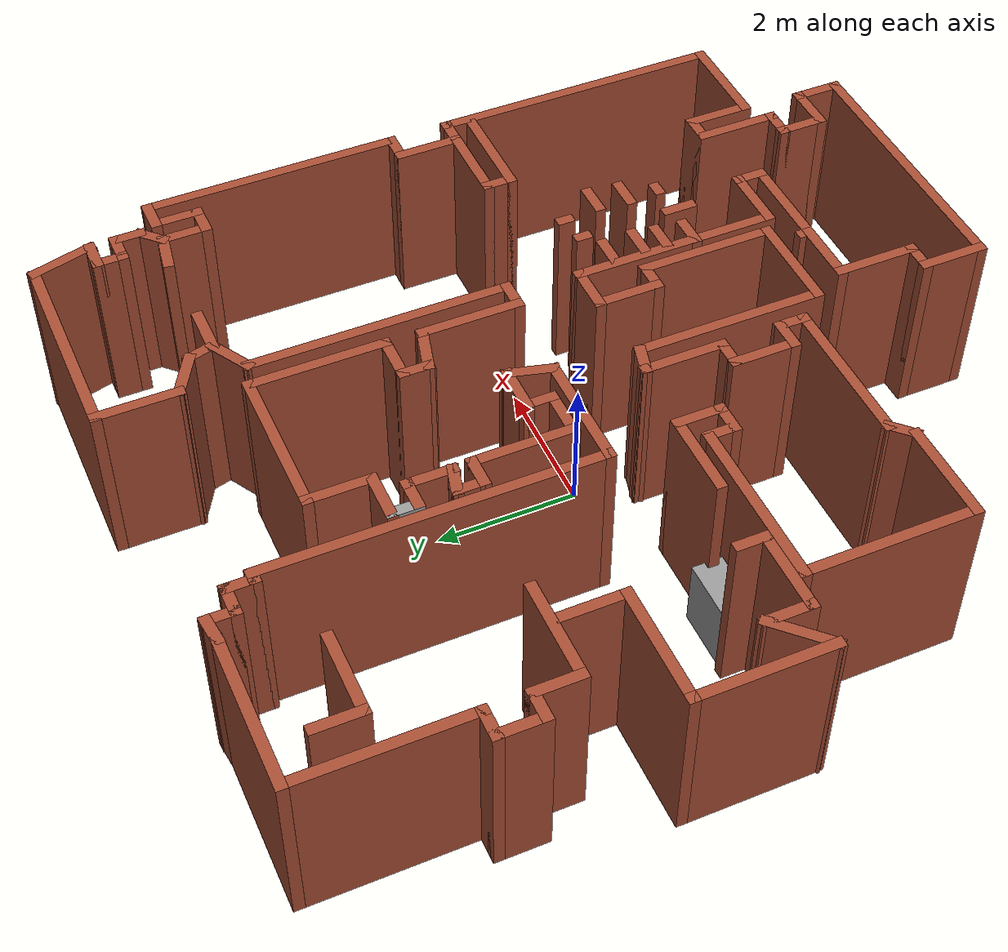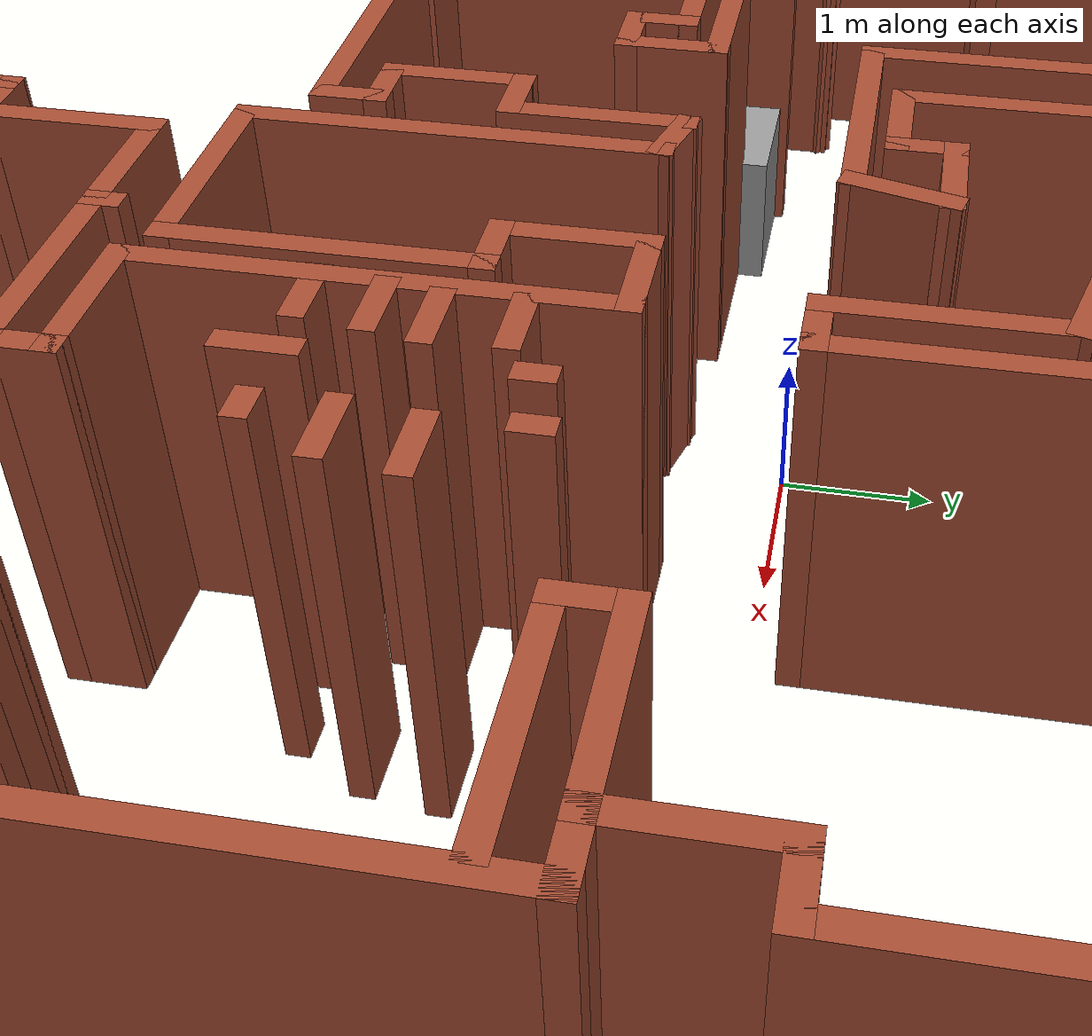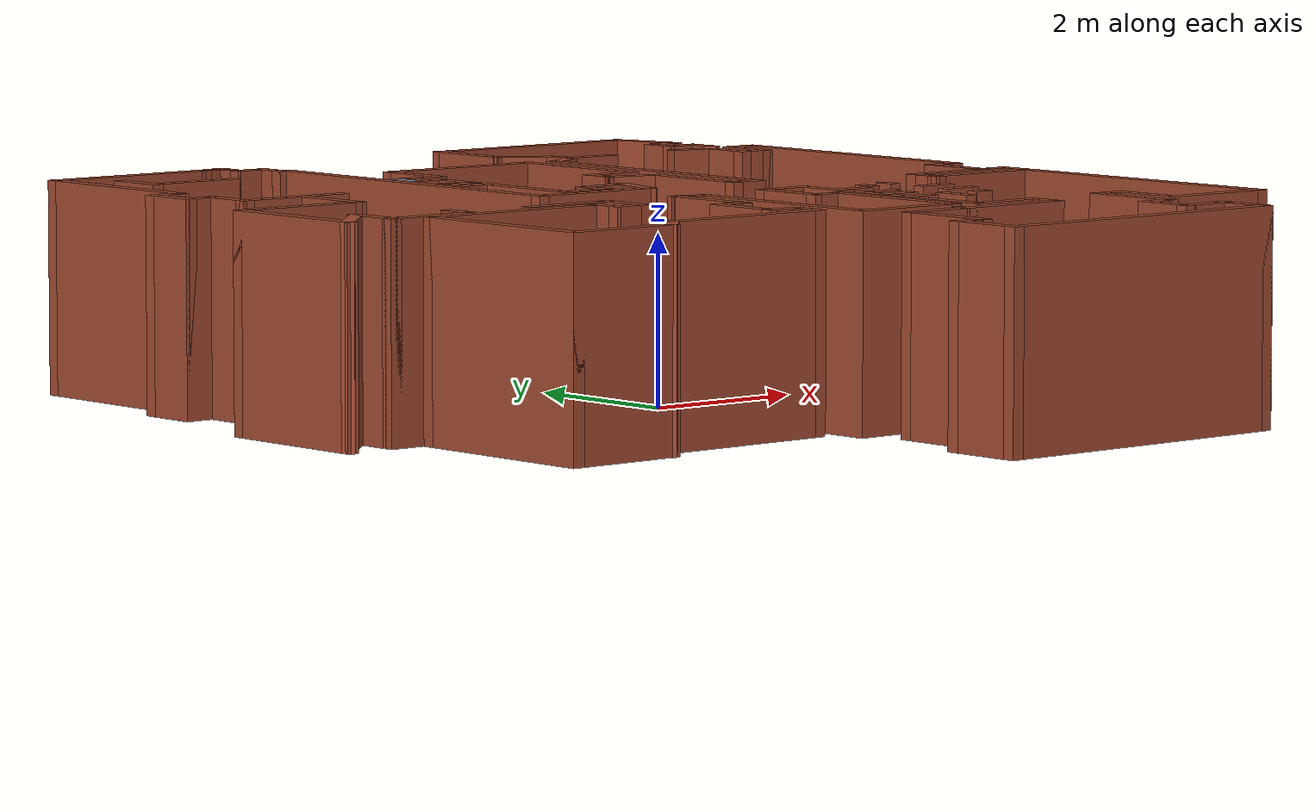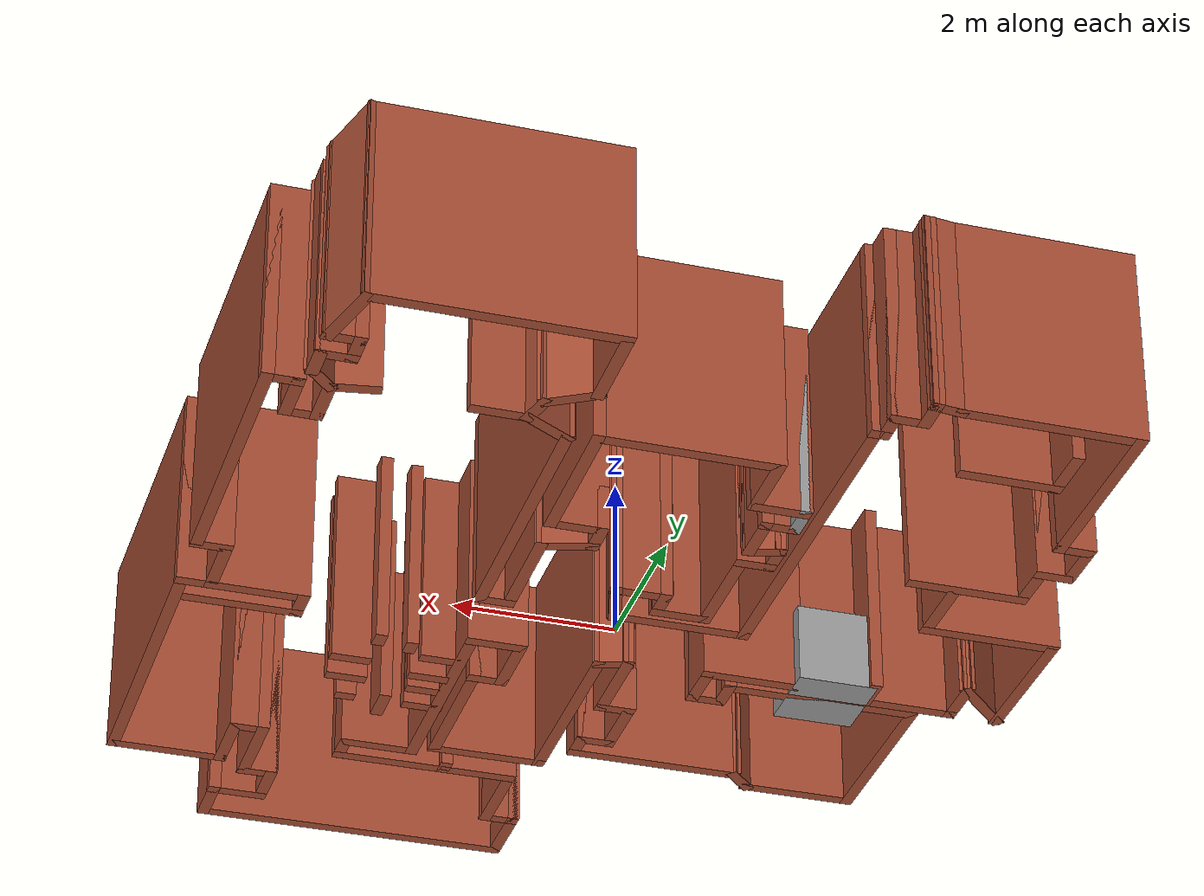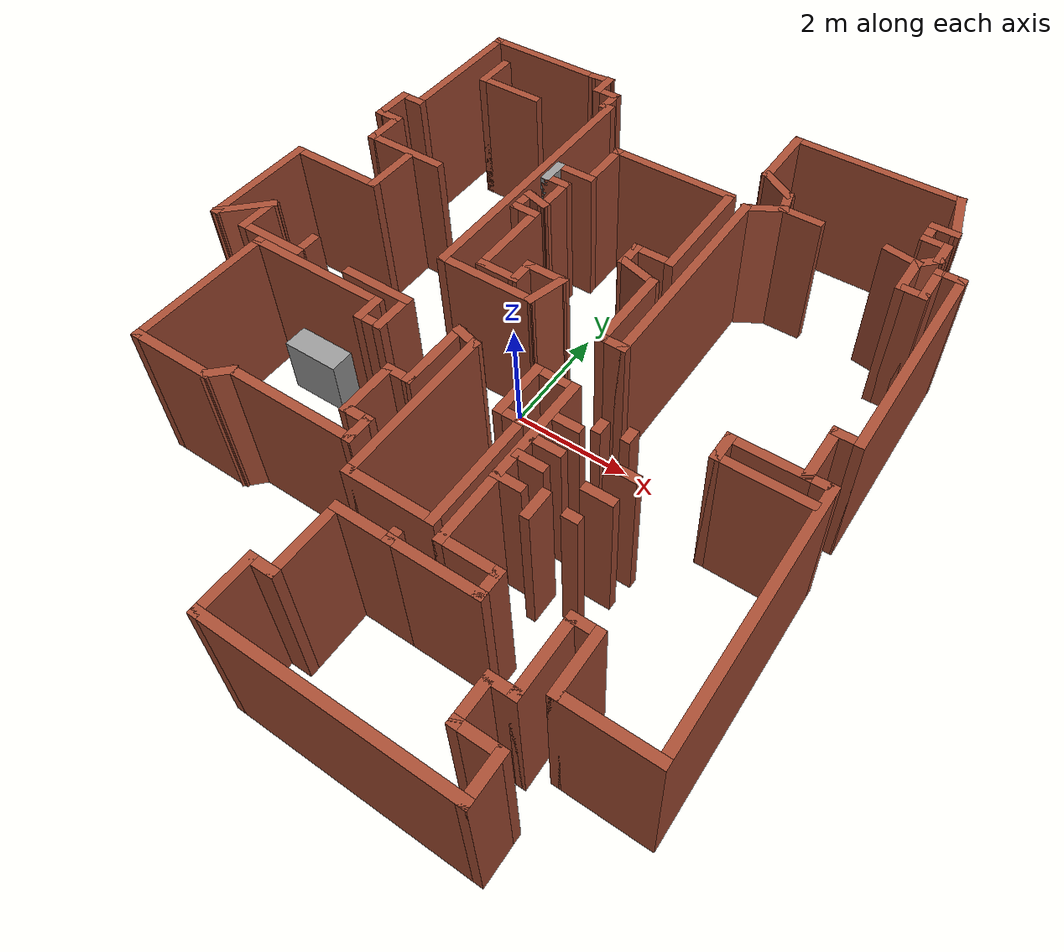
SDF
<?xml version='1.0'?>
<sdf version='1.6'>
  <model name='map_77'>
    <link name='Wall_0'>
      <pose frame=''>-3.30096 5.5702 0 0 -0 3.14159</pose>
      <self_collide>0</self_collide>
      <enable_wind>0</enable_wind>
      <kinematic>0</kinematic>
      <visual name='Wall_0_Visual'>
        <pose frame=''>0 0 1.25 0 -0 0</pose>
        <geometry>
          <box>
            <size>2.25 0.15 2.5</size>
          </box>
        </geometry>
        <material>
          <script>
            <uri>file://media/materials/scripts/gazebo.material</uri>
            <name>Gazebo/Bricks</name>
          </script>
          <ambient>1 1 1 1</ambient>
          <shader type='pixel'/>
        </material>
        <meta>
          <layer>0</layer>
        </meta>
        <transparency>0</transparency>
        <cast_shadows>1</cast_shadows>
      </visual>
      <collision name='Wall_0_Collision'>
        <laser_retro>0</laser_retro>
        <max_contacts>10</max_contacts>
        <pose frame=''>0 0 1.25 0 -0 0</pose>
        <geometry>
          <box>
            <size>2.25 0.15 2.5</size>
          </box>
        </geometry>
        <surface>
          <friction>
            <ode>
              <mu>1</mu>
              <mu2>1</mu2>
              <fdir1>0 0 0</fdir1>
              <slip1>0</slip1>
              <slip2>0</slip2>
            </ode>
            <torsional>
              <coefficient>1</coefficient>
              <patch_radius>0</patch_radius>
              <surface_radius>0</surface_radius>
              <use_patch_radius>1</use_patch_radius>
              <ode>
                <slip>0</slip>
              </ode>
            </torsional>
          </friction>
          <bounce>
            <restitution_coefficient>0</restitution_coefficient>
            <threshold>1e+06</threshold>
          </bounce>
          <contact>
            <collide_without_contact>0</collide_without_contact>
            <collide_without_contact_bitmask>1</collide_without_contact_bitmask>
            <collide_bitmask>1</collide_bitmask>
            <ode>
              <soft_cfm>0</soft_cfm>
              <soft_erp>0.2</soft_erp>
              <kp>1e+13</kp>
              <kd>1</kd>
              <max_vel>0.01</max_vel>
              <min_depth>0</min_depth>
            </ode>
            <bullet>
              <split_impulse>1</split_impulse>
              <split_impulse_penetration_threshold>-0.01</split_impulse_penetration_threshold>
              <soft_cfm>0</soft_cfm>
              <soft_erp>0.2</soft_erp>
              <kp>1e+13</kp>
              <kd>1</kd>
            </bullet>
          </contact>
        </surface>
      </collision>
    </link>
    <link name='Wall_1'>
      <pose frame=''>-4.35096 4.3952 0 0 0 -1.5708</pose>
      <self_collide>0</self_collide>
      <enable_wind>0</enable_wind>
      <kinematic>0</kinematic>
      <visual name='Wall_1_Visual'>
        <pose frame=''>0 0 1.25 0 -0 0</pose>
        <geometry>
          <box>
            <size>2.5 0.15 2.5</size>
          </box>
        </geometry>
        <material>
          <script>
            <uri>file://media/materials/scripts/gazebo.material</uri>
            <name>Gazebo/Bricks</name>
          </script>
          <ambient>1 1 1 1</ambient>
          <shader type='pixel'/>
        </material>
        <meta>
          <layer>0</layer>
        </meta>
        <transparency>0</transparency>
        <cast_shadows>1</cast_shadows>
      </visual>
      <collision name='Wall_1_Collision'>
        <laser_retro>0</laser_retro>
        <max_contacts>10</max_contacts>
        <pose frame=''>0 0 1.25 0 -0 0</pose>
        <geometry>
          <box>
            <size>2.5 0.15 2.5</size>
          </box>
        </geometry>
        <surface>
          <friction>
            <ode>
              <mu>1</mu>
              <mu2>1</mu2>
              <fdir1>0 0 0</fdir1>
              <slip1>0</slip1>
              <slip2>0</slip2>
            </ode>
            <torsional>
              <coefficient>1</coefficient>
              <patch_radius>0</patch_radius>
              <surface_radius>0</surface_radius>
              <use_patch_radius>1</use_patch_radius>
              <ode>
                <slip>0</slip>
              </ode>
            </torsional>
          </friction>
          <bounce>
            <restitution_coefficient>0</restitution_coefficient>
            <threshold>1e+06</threshold>
          </bounce>
          <contact>
            <collide_without_contact>0</collide_without_contact>
            <collide_without_contact_bitmask>1</collide_without_contact_bitmask>
            <collide_bitmask>1</collide_bitmask>
            <ode>
              <soft_cfm>0</soft_cfm>
              <soft_erp>0.2</soft_erp>
              <kp>1e+13</kp>
              <kd>1</kd>
              <max_vel>0.01</max_vel>
              <min_depth>0</min_depth>
            </ode>
            <bullet>
              <split_impulse>1</split_impulse>
              <split_impulse_penetration_threshold>-0.01</split_impulse_penetration_threshold>
              <soft_cfm>0</soft_cfm>
              <soft_erp>0.2</soft_erp>
              <kp>1e+13</kp>
              <kd>1</kd>
            </bullet>
          </contact>
        </surface>
      </collision>
    </link>
    <link name='Wall_10'>
      <pose frame=''>-5.12777 0.124368 0 0 0 -1.5708</pose>
      <self_collide>0</self_collide>
      <enable_wind>0</enable_wind>
      <kinematic>0</kinematic>
      <visual name='Wall_10_Visual'>
        <pose frame=''>0 0 1.25 0 -0 0</pose>
        <geometry>
          <box>
            <size>2 0.15 2.5</size>
          </box>
        </geometry>
        <material>
          <script>
            <uri>file://media/materials/scripts/gazebo.material</uri>
            <name>Gazebo/Bricks</name>
          </script>
          <ambient>1 1 1 1</ambient>
          <shader type='pixel'/>
        </material>
        <meta>
          <layer>0</layer>
        </meta>
        <transparency>0</transparency>
        <cast_shadows>1</cast_shadows>
      </visual>
      <collision name='Wall_10_Collision'>
        <laser_retro>0</laser_retro>
        <max_contacts>10</max_contacts>
        <pose frame=''>0 0 1.25 0 -0 0</pose>
        <geometry>
          <box>
            <size>2 0.15 2.5</size>
          </box>
        </geometry>
        <surface>
          <friction>
            <ode>
              <mu>1</mu>
              <mu2>1</mu2>
              <fdir1>0 0 0</fdir1>
              <slip1>0</slip1>
              <slip2>0</slip2>
            </ode>
            <torsional>
              <coefficient>1</coefficient>
              <patch_radius>0</patch_radius>
              <surface_radius>0</surface_radius>
              <use_patch_radius>1</use_patch_radius>
              <ode>
                <slip>0</slip>
              </ode>
            </torsional>
          </friction>
          <bounce>
            <restitution_coefficient>0</restitution_coefficient>
            <threshold>1e+06</threshold>
          </bounce>
          <contact>
            <collide_without_contact>0</collide_without_contact>
            <collide_without_contact_bitmask>1</collide_without_contact_bitmask>
            <collide_bitmask>1</collide_bitmask>
            <ode>
              <soft_cfm>0</soft_cfm>
              <soft_erp>0.2</soft_erp>
              <kp>1e+13</kp>
              <kd>1</kd>
              <max_vel>0.01</max_vel>
              <min_depth>0</min_depth>
            </ode>
            <bullet>
              <split_impulse>1</split_impulse>
              <split_impulse_penetration_threshold>-0.01</split_impulse_penetration_threshold>
              <soft_cfm>0</soft_cfm>
              <soft_erp>0.2</soft_erp>
              <kp>1e+13</kp>
              <kd>1</kd>
            </bullet>
          </contact>
        </surface>
      </collision>
    </link>
    <link name='Wall_100'>
      <pose frame=''>-0.702644 3.51805 0 0 0 -1.5708</pose>
      <self_collide>0</self_collide>
      <enable_wind>0</enable_wind>
      <kinematic>0</kinematic>
      <visual name='Wall_100_Visual'>
        <pose frame=''>0 0 1.25 0 -0 0</pose>
        <geometry>
          <box>
            <size>1 0.15 2.5</size>
          </box>
        </geometry>
        <material>
          <script>
            <uri>file://media/materials/scripts/gazebo.material</uri>
            <name>Gazebo/Bricks</name>
          </script>
          <ambient>1 1 1 1</ambient>
          <shader type='pixel'/>
        </material>
        <meta>
          <layer>0</layer>
        </meta>
        <transparency>0</transparency>
        <cast_shadows>1</cast_shadows>
      </visual>
      <collision name='Wall_100_Collision'>
        <laser_retro>0</laser_retro>
        <max_contacts>10</max_contacts>
        <pose frame=''>0 0 1.25 0 -0 0</pose>
        <geometry>
          <box>
            <size>1 0.15 2.5</size>
          </box>
        </geometry>
        <surface>
          <friction>
            <ode>
              <mu>1</mu>
              <mu2>1</mu2>
              <fdir1>0 0 0</fdir1>
              <slip1>0</slip1>
              <slip2>0</slip2>
            </ode>
            <torsional>
              <coefficient>1</coefficient>
              <patch_radius>0</patch_radius>
              <surface_radius>0</surface_radius>
              <use_patch_radius>1</use_patch_radius>
              <ode>
                <slip>0</slip>
              </ode>
            </torsional>
          </friction>
          <bounce>
            <restitution_coefficient>0</restitution_coefficient>
            <threshold>1e+06</threshold>
          </bounce>
          <contact>
            <collide_without_contact>0</collide_without_contact>
            <collide_without_contact_bitmask>1</collide_without_contact_bitmask>
            <collide_bitmask>1</collide_bitmask>
            <ode>
              <soft_cfm>0</soft_cfm>
              <soft_erp>0.2</soft_erp>
              <kp>1e+13</kp>
              <kd>1</kd>
              <max_vel>0.01</max_vel>
              <min_depth>0</min_depth>
            </ode>
            <bullet>
              <split_impulse>1</split_impulse>
              <split_impulse_penetration_threshold>-0.01</split_impulse_penetration_threshold>
              <soft_cfm>0</soft_cfm>
              <soft_erp>0.2</soft_erp>
              <kp>1e+13</kp>
              <kd>1</kd>
            </bullet>
          </contact>
        </surface>
      </collision>
    </link>
    <link name='Wall_101'>
      <pose frame=''>-1.00264 3.09305 0 0 -0 3.14159</pose>
      <self_collide>0</self_collide>
      <enable_wind>0</enable_wind>
      <kinematic>0</kinematic>
      <visual name='Wall_101_Visual'>
        <pose frame=''>0 0 1.25 0 -0 0</pose>
        <geometry>
          <box>
            <size>0.75 0.15 2.5</size>
          </box>
        </geometry>
        <material>
          <script>
            <uri>file://media/materials/scripts/gazebo.material</uri>
            <name>Gazebo/Bricks</name>
          </script>
          <ambient>1 1 1 1</ambient>
          <shader type='pixel'/>
        </material>
        <meta>
          <layer>0</layer>
        </meta>
        <transparency>0</transparency>
        <cast_shadows>1</cast_shadows>
      </visual>
      <collision name='Wall_101_Collision'>
        <laser_retro>0</laser_retro>
        <max_contacts>10</max_contacts>
        <pose frame=''>0 0 1.25 0 -0 0</pose>
        <geometry>
          <box>
            <size>0.75 0.15 2.5</size>
          </box>
        </geometry>
        <surface>
          <friction>
            <ode>
              <mu>1</mu>
              <mu2>1</mu2>
              <fdir1>0 0 0</fdir1>
              <slip1>0</slip1>
              <slip2>0</slip2>
            </ode>
            <torsional>
              <coefficient>1</coefficient>
              <patch_radius>0</patch_radius>
              <surface_radius>0</surface_radius>
              <use_patch_radius>1</use_patch_radius>
              <ode>
                <slip>0</slip>
              </ode>
            </torsional>
          </friction>
          <bounce>
            <restitution_coefficient>0</restitution_coefficient>
            <threshold>1e+06</threshold>
          </bounce>
          <contact>
            <collide_without_contact>0</collide_without_contact>
            <collide_without_contact_bitmask>1</collide_without_contact_bitmask>
            <collide_bitmask>1</collide_bitmask>
            <ode>
              <soft_cfm>0</soft_cfm>
              <soft_erp>0.2</soft_erp>
              <kp>1e+13</kp>
              <kd>1</kd>
              <max_vel>0.01</max_vel>
              <min_depth>0</min_depth>
            </ode>
            <bullet>
              <split_impulse>1</split_impulse>
              <split_impulse_penetration_threshold>-0.01</split_impulse_penetration_threshold>
              <soft_cfm>0</soft_cfm>
              <soft_erp>0.2</soft_erp>
              <kp>1e+13</kp>
              <kd>1</kd>
            </bullet>
          </contact>
        </surface>
      </collision>
    </link>
    <link name='Wall_102'>
      <pose frame=''>-1.30264 2.91805 0 0 0 -1.5708</pose>
      <self_collide>0</self_collide>
      <enable_wind>0</enable_wind>
      <kinematic>0</kinematic>
      <visual name='Wall_102_Visual'>
        <pose frame=''>0 0 1.25 0 -0 0</pose>
        <geometry>
          <box>
            <size>0.5 0.15 2.5</size>
          </box>
        </geometry>
        <material>
          <script>
            <uri>file://media/materials/scripts/gazebo.material</uri>
            <name>Gazebo/Grey</name>
          </script>
          <ambient>1 1 1 1</ambient>
          <shader type='pixel'/>
        </material>
        <meta>
          <layer>0</layer>
        </meta>
        <transparency>0</transparency>
        <cast_shadows>1</cast_shadows>
      </visual>
      <collision name='Wall_102_Collision'>
        <laser_retro>0</laser_retro>
        <max_contacts>10</max_contacts>
        <pose frame=''>0 0 1.25 0 -0 0</pose>
        <geometry>
          <box>
            <size>0.5 0.15 2.5</size>
          </box>
        </geometry>
        <surface>
          <friction>
            <ode>
              <mu>1</mu>
              <mu2>1</mu2>
              <fdir1>0 0 0</fdir1>
              <slip1>0</slip1>
              <slip2>0</slip2>
            </ode>
            <torsional>
              <coefficient>1</coefficient>
              <patch_radius>0</patch_radius>
              <surface_radius>0</surface_radius>
              <use_patch_radius>1</use_patch_radius>
              <ode>
                <slip>0</slip>
              </ode>
            </torsional>
          </friction>
          <bounce>
            <restitution_coefficient>0</restitution_coefficient>
            <threshold>1e+06</threshold>
          </bounce>
          <contact>
            <collide_without_contact>0</collide_without_contact>
            <collide_without_contact_bitmask>1</collide_without_contact_bitmask>
            <collide_bitmask>1</collide_bitmask>
            <ode>
              <soft_cfm>0</soft_cfm>
              <soft_erp>0.2</soft_erp>
              <kp>1e+13</kp>
              <kd>1</kd>
              <max_vel>0.01</max_vel>
              <min_depth>0</min_depth>
            </ode>
            <bullet>
              <split_impulse>1</split_impulse>
              <split_impulse_penetration_threshold>-0.01</split_impulse_penetration_threshold>
              <soft_cfm>0</soft_cfm>
              <soft_erp>0.2</soft_erp>
              <kp>1e+13</kp>
              <kd>1</kd>
            </bullet>
          </contact>
        </surface>
      </collision>
    </link>
    <link name='Wall_103'>
      <pose frame=''>-1.12764 2.74305 0 0 -0 0</pose>
      <self_collide>0</self_collide>
      <enable_wind>0</enable_wind>
      <kinematic>0</kinematic>
      <visual name='Wall_103_Visual'>
        <pose frame=''>0 0 1.25 0 -0 0</pose>
        <geometry>
          <box>
            <size>0.5 0.15 2.5</size>
          </box>
        </geometry>
        <material>
          <script>
            <uri>file://media/materials/scripts/gazebo.material</uri>
            <name>Gazebo/Bricks</name>
          </script>
          <ambient>1 1 1 1</ambient>
          <shader type='pixel'/>
        </material>
        <meta>
          <layer>0</layer>
        </meta>
        <transparency>0</transparency>
        <cast_shadows>1</cast_shadows>
      </visual>
      <collision name='Wall_103_Collision'>
        <laser_retro>0</laser_retro>
        <max_contacts>10</max_contacts>
        <pose frame=''>0 0 1.25 0 -0 0</pose>
        <geometry>
          <box>
            <size>0.5 0.15 2.5</size>
          </box>
        </geometry>
        <surface>
          <friction>
            <ode>
              <mu>1</mu>
              <mu2>1</mu2>
              <fdir1>0 0 0</fdir1>
              <slip1>0</slip1>
              <slip2>0</slip2>
            </ode>
            <torsional>
              <coefficient>1</coefficient>
              <patch_radius>0</patch_radius>
              <surface_radius>0</surface_radius>
              <use_patch_radius>1</use_patch_radius>
              <ode>
                <slip>0</slip>
              </ode>
            </torsional>
          </friction>
          <bounce>
            <restitution_coefficient>0</restitution_coefficient>
            <threshold>1e+06</threshold>
          </bounce>
          <contact>
            <collide_without_contact>0</collide_without_contact>
            <collide_without_contact_bitmask>1</collide_without_contact_bitmask>
            <collide_bitmask>1</collide_bitmask>
            <ode>
              <soft_cfm>0</soft_cfm>
              <soft_erp>0.2</soft_erp>
              <kp>1e+13</kp>
              <kd>1</kd>
              <max_vel>0.01</max_vel>
              <min_depth>0</min_depth>
            </ode>
            <bullet>
              <split_impulse>1</split_impulse>
              <split_impulse_penetration_threshold>-0.01</split_impulse_penetration_threshold>
              <soft_cfm>0</soft_cfm>
              <soft_erp>0.2</soft_erp>
              <kp>1e+13</kp>
              <kd>1</kd>
            </bullet>
          </contact>
        </surface>
      </collision>
    </link>
    <link name='Wall_104'>
      <pose frame=''>-0.952644 2.44305 0 0 0 -1.5708</pose>
      <self_collide>0</self_collide>
      <enable_wind>0</enable_wind>
      <kinematic>0</kinematic>
      <visual name='Wall_104_Visual'>
        <pose frame=''>0 0 1.25 0 -0 0</pose>
        <geometry>
          <box>
            <size>0.75 0.15 2.5</size>
          </box>
        </geometry>
        <material>
          <script>
            <uri>file://media/materials/scripts/gazebo.material</uri>
            <name>Gazebo/Bricks</name>
          </script>
          <ambient>1 1 1 1</ambient>
          <shader type='pixel'/>
        </material>
        <meta>
          <layer>0</layer>
        </meta>
        <transparency>0</transparency>
        <cast_shadows>1</cast_shadows>
      </visual>
      <collision name='Wall_104_Collision'>
        <laser_retro>0</laser_retro>
        <max_contacts>10</max_contacts>
        <pose frame=''>0 0 1.25 0 -0 0</pose>
        <geometry>
          <box>
            <size>0.75 0.15 2.5</size>
          </box>
        </geometry>
        <surface>
          <friction>
            <ode>
              <mu>1</mu>
              <mu2>1</mu2>
              <fdir1>0 0 0</fdir1>
              <slip1>0</slip1>
              <slip2>0</slip2>
            </ode>
            <torsional>
              <coefficient>1</coefficient>
              <patch_radius>0</patch_radius>
              <surface_radius>0</surface_radius>
              <use_patch_radius>1</use_patch_radius>
              <ode>
                <slip>0</slip>
              </ode>
            </torsional>
          </friction>
          <bounce>
            <restitution_coefficient>0</restitution_coefficient>
            <threshold>1e+06</threshold>
          </bounce>
          <contact>
            <collide_without_contact>0</collide_without_contact>
            <collide_without_contact_bitmask>1</collide_without_contact_bitmask>
            <collide_bitmask>1</collide_bitmask>
            <ode>
              <soft_cfm>0</soft_cfm>
              <soft_erp>0.2</soft_erp>
              <kp>1e+13</kp>
              <kd>1</kd>
              <max_vel>0.01</max_vel>
              <min_depth>0</min_depth>
            </ode>
            <bullet>
              <split_impulse>1</split_impulse>
              <split_impulse_penetration_threshold>-0.01</split_impulse_penetration_threshold>
              <soft_cfm>0</soft_cfm>
              <soft_erp>0.2</soft_erp>
              <kp>1e+13</kp>
              <kd>1</kd>
            </bullet>
          </contact>
        </surface>
      </collision>
    </link>
    <link name='Wall_105'>
      <pose frame=''>-1.12168 2.18834 0 0 -0 2.87979</pose>
      <self_collide>0</self_collide>
      <enable_wind>0</enable_wind>
      <kinematic>0</kinematic>
      <visual name='Wall_105_Visual'>
        <pose frame=''>0 0 1.25 0 -0 0</pose>
        <geometry>
          <box>
            <size>0.5 0.15 2.5</size>
          </box>
        </geometry>
        <material>
          <script>
            <uri>file://media/materials/scripts/gazebo.material</uri>
            <name>Gazebo/Bricks</name>
          </script>
          <ambient>1 1 1 1</ambient>
          <shader type='pixel'/>
        </material>
        <meta>
          <layer>0</layer>
        </meta>
        <transparency>0</transparency>
        <cast_shadows>1</cast_shadows>
      </visual>
      <collision name='Wall_105_Collision'>
        <laser_retro>0</laser_retro>
        <max_contacts>10</max_contacts>
        <pose frame=''>0 0 1.25 0 -0 0</pose>
        <geometry>
          <box>
            <size>0.5 0.15 2.5</size>
          </box>
        </geometry>
        <surface>
          <friction>
            <ode>
              <mu>1</mu>
              <mu2>1</mu2>
              <fdir1>0 0 0</fdir1>
              <slip1>0</slip1>
              <slip2>0</slip2>
            </ode>
            <torsional>
              <coefficient>1</coefficient>
              <patch_radius>0</patch_radius>
              <surface_radius>0</surface_radius>
              <use_patch_radius>1</use_patch_radius>
              <ode>
                <slip>0</slip>
              </ode>
            </torsional>
          </friction>
          <bounce>
            <restitution_coefficient>0</restitution_coefficient>
            <threshold>1e+06</threshold>
          </bounce>
          <contact>
            <collide_without_contact>0</collide_without_contact>
            <collide_without_contact_bitmask>1</collide_without_contact_bitmask>
            <collide_bitmask>1</collide_bitmask>
            <ode>
              <soft_cfm>0</soft_cfm>
              <soft_erp>0.2</soft_erp>
              <kp>1e+13</kp>
              <kd>1</kd>
              <max_vel>0.01</max_vel>
              <min_depth>0</min_depth>
            </ode>
            <bullet>
              <split_impulse>1</split_impulse>
              <split_impulse_penetration_threshold>-0.01</split_impulse_penetration_threshold>
              <soft_cfm>0</soft_cfm>
              <soft_erp>0.2</soft_erp>
              <kp>1e+13</kp>
              <kd>1</kd>
            </bullet>
          </contact>
        </surface>
      </collision>
    </link>
    <link name='Wall_106'>
      <pose frame=''>-1.29072 2.05864 0 0 0 -1.5708</pose>
      <self_collide>0</self_collide>
      <enable_wind>0</enable_wind>
      <kinematic>0</kinematic>
      <visual name='Wall_106_Visual'>
        <pose frame=''>0 0 1.25 0 -0 0</pose>
        <geometry>
          <box>
            <size>0.5 0.15 2.5</size>
          </box>
        </geometry>
        <material>
          <script>
            <uri>file://media/materials/scripts/gazebo.material</uri>
            <name>Gazebo/Bricks</name>
          </script>
          <ambient>1 1 1 1</ambient>
          <shader type='pixel'/>
        </material>
        <meta>
          <layer>0</layer>
        </meta>
        <transparency>0</transparency>
        <cast_shadows>1</cast_shadows>
      </visual>
      <collision name='Wall_106_Collision'>
        <laser_retro>0</laser_retro>
        <max_contacts>10</max_contacts>
        <pose frame=''>0 0 1.25 0 -0 0</pose>
        <geometry>
          <box>
            <size>0.5 0.15 2.5</size>
          </box>
        </geometry>
        <surface>
          <friction>
            <ode>
              <mu>1</mu>
              <mu2>1</mu2>
              <fdir1>0 0 0</fdir1>
              <slip1>0</slip1>
              <slip2>0</slip2>
            </ode>
            <torsional>
              <coefficient>1</coefficient>
              <patch_radius>0</patch_radius>
              <surface_radius>0</surface_radius>
              <use_patch_radius>1</use_patch_radius>
              <ode>
                <slip>0</slip>
              </ode>
            </torsional>
          </friction>
          <bounce>
            <restitution_coefficient>0</restitution_coefficient>
            <threshold>1e+06</threshold>
          </bounce>
          <contact>
            <collide_without_contact>0</collide_without_contact>
            <collide_without_contact_bitmask>1</collide_without_contact_bitmask>
            <collide_bitmask>1</collide_bitmask>
            <ode>
              <soft_cfm>0</soft_cfm>
              <soft_erp>0.2</soft_erp>
              <kp>1e+13</kp>
              <kd>1</kd>
              <max_vel>0.01</max_vel>
              <min_depth>0</min_depth>
            </ode>
            <bullet>
              <split_impulse>1</split_impulse>
              <split_impulse_penetration_threshold>-0.01</split_impulse_penetration_threshold>
              <soft_cfm>0</soft_cfm>
              <soft_erp>0.2</soft_erp>
              <kp>1e+13</kp>
              <kd>1</kd>
            </bullet>
          </contact>
        </surface>
      </collision>
    </link>
    <link name='Wall_107'>
      <pose frame=''>-1.11572 1.88364 0 0 -0 0</pose>
      <self_collide>0</self_collide>
      <enable_wind>0</enable_wind>
      <kinematic>0</kinematic>
      <visual name='Wall_107_Visual'>
        <pose frame=''>0 0 1.25 0 -0 0</pose>
        <geometry>
          <box>
            <size>0.5 0.15 2.5</size>
          </box>
        </geometry>
        <material>
          <script>
            <uri>file://media/materials/scripts/gazebo.material</uri>
            <name>Gazebo/Bricks</name>
          </script>
          <ambient>1 1 1 1</ambient>
          <shader type='pixel'/>
        </material>
        <meta>
          <layer>0</layer>
        </meta>
        <transparency>0</transparency>
        <cast_shadows>1</cast_shadows>
      </visual>
      <collision name='Wall_107_Collision'>
        <laser_retro>0</laser_retro>
        <max_contacts>10</max_contacts>
        <pose frame=''>0 0 1.25 0 -0 0</pose>
        <geometry>
          <box>
            <size>0.5 0.15 2.5</size>
          </box>
        </geometry>
        <surface>
          <friction>
            <ode>
              <mu>1</mu>
              <mu2>1</mu2>
              <fdir1>0 0 0</fdir1>
              <slip1>0</slip1>
              <slip2>0</slip2>
            </ode>
            <torsional>
              <coefficient>1</coefficient>
              <patch_radius>0</patch_radius>
              <surface_radius>0</surface_radius>
              <use_patch_radius>1</use_patch_radius>
              <ode>
                <slip>0</slip>
              </ode>
            </torsional>
          </friction>
          <bounce>
            <restitution_coefficient>0</restitution_coefficient>
            <threshold>1e+06</threshold>
          </bounce>
          <contact>
            <collide_without_contact>0</collide_without_contact>
            <collide_without_contact_bitmask>1</collide_without_contact_bitmask>
            <collide_bitmask>1</collide_bitmask>
            <ode>
              <soft_cfm>0</soft_cfm>
              <soft_erp>0.2</soft_erp>
              <kp>1e+13</kp>
              <kd>1</kd>
              <max_vel>0.01</max_vel>
              <min_depth>0</min_depth>
            </ode>
            <bullet>
              <split_impulse>1</split_impulse>
              <split_impulse_penetration_threshold>-0.01</split_impulse_penetration_threshold>
              <soft_cfm>0</soft_cfm>
              <soft_erp>0.2</soft_erp>
              <kp>1e+13</kp>
              <kd>1</kd>
            </bullet>
          </contact>
        </surface>
      </collision>
    </link>
    <link name='Wall_108'>
      <pose frame=''>-0.940718 1.20864 0 0 0 -1.5708</pose>
      <self_collide>0</self_collide>
      <enable_wind>0</enable_wind>
      <kinematic>0</kinematic>
      <visual name='Wall_108_Visual'>
        <pose frame=''>0 0 1.25 0 -0 0</pose>
        <geometry>
          <box>
            <size>1.5 0.15 2.5</size>
          </box>
        </geometry>
        <material>
          <script>
            <uri>file://media/materials/scripts/gazebo.material</uri>
            <name>Gazebo/Bricks</name>
          </script>
          <ambient>1 1 1 1</ambient>
          <shader type='pixel'/>
        </material>
        <meta>
          <layer>0</layer>
        </meta>
        <transparency>0</transparency>
        <cast_shadows>1</cast_shadows>
      </visual>
      <collision name='Wall_108_Collision'>
        <laser_retro>0</laser_retro>
        <max_contacts>10</max_contacts>
        <pose frame=''>0 0 1.25 0 -0 0</pose>
        <geometry>
          <box>
            <size>1.5 0.15 2.5</size>
          </box>
        </geometry>
        <surface>
          <friction>
            <ode>
              <mu>1</mu>
              <mu2>1</mu2>
              <fdir1>0 0 0</fdir1>
              <slip1>0</slip1>
              <slip2>0</slip2>
            </ode>
            <torsional>
              <coefficient>1</coefficient>
              <patch_radius>0</patch_radius>
              <surface_radius>0</surface_radius>
              <use_patch_radius>1</use_patch_radius>
              <ode>
                <slip>0</slip>
              </ode>
            </torsional>
          </friction>
          <bounce>
            <restitution_coefficient>0</restitution_coefficient>
            <threshold>1e+06</threshold>
          </bounce>
          <contact>
            <collide_without_contact>0</collide_without_contact>
            <collide_without_contact_bitmask>1</collide_without_contact_bitmask>
            <collide_bitmask>1</collide_bitmask>
            <ode>
              <soft_cfm>0</soft_cfm>
              <soft_erp>0.2</soft_erp>
              <kp>1e+13</kp>
              <kd>1</kd>
              <max_vel>0.01</max_vel>
              <min_depth>0</min_depth>
            </ode>
            <bullet>
              <split_impulse>1</split_impulse>
              <split_impulse_penetration_threshold>-0.01</split_impulse_penetration_threshold>
              <soft_cfm>0</soft_cfm>
              <soft_erp>0.2</soft_erp>
              <kp>1e+13</kp>
              <kd>1</kd>
            </bullet>
          </contact>
        </surface>
      </collision>
    </link>
    <link name='Wall_109'>
      <pose frame=''>-0.640718 0.533638 0 0 -0 0</pose>
      <self_collide>0</self_collide>
      <enable_wind>0</enable_wind>
      <kinematic>0</kinematic>
      <visual name='Wall_109_Visual'>
        <pose frame=''>0 0 1.25 0 -0 0</pose>
        <geometry>
          <box>
            <size>0.75 0.15 2.5</size>
          </box>
        </geometry>
        <material>
          <script>
            <uri>file://media/materials/scripts/gazebo.material</uri>
            <name>Gazebo/Bricks</name>
          </script>
          <ambient>1 1 1 1</ambient>
          <shader type='pixel'/>
        </material>
        <meta>
          <layer>0</layer>
        </meta>
        <transparency>0</transparency>
        <cast_shadows>1</cast_shadows>
      </visual>
      <collision name='Wall_109_Collision'>
        <laser_retro>0</laser_retro>
        <max_contacts>10</max_contacts>
        <pose frame=''>0 0 1.25 0 -0 0</pose>
        <geometry>
          <box>
            <size>0.75 0.15 2.5</size>
          </box>
        </geometry>
        <surface>
          <friction>
            <ode>
              <mu>1</mu>
              <mu2>1</mu2>
              <fdir1>0 0 0</fdir1>
              <slip1>0</slip1>
              <slip2>0</slip2>
            </ode>
            <torsional>
              <coefficient>1</coefficient>
              <patch_radius>0</patch_radius>
              <surface_radius>0</surface_radius>
              <use_patch_radius>1</use_patch_radius>
              <ode>
                <slip>0</slip>
              </ode>
            </torsional>
          </friction>
          <bounce>
            <restitution_coefficient>0</restitution_coefficient>
            <threshold>1e+06</threshold>
          </bounce>
          <contact>
            <collide_without_contact>0</collide_without_contact>
            <collide_without_contact_bitmask>1</collide_without_contact_bitmask>
            <collide_bitmask>1</collide_bitmask>
            <ode>
              <soft_cfm>0</soft_cfm>
              <soft_erp>0.2</soft_erp>
              <kp>1e+13</kp>
              <kd>1</kd>
              <max_vel>0.01</max_vel>
              <min_depth>0</min_depth>
            </ode>
            <bullet>
              <split_impulse>1</split_impulse>
              <split_impulse_penetration_threshold>-0.01</split_impulse_penetration_threshold>
              <soft_cfm>0</soft_cfm>
              <soft_erp>0.2</soft_erp>
              <kp>1e+13</kp>
              <kd>1</kd>
            </bullet>
          </contact>
        </surface>
      </collision>
    </link>
    <link name='Wall_11'>
      <pose frame=''>-4.82725 -0.500111 0 0 -0 0.785398</pose>
      <self_collide>0</self_collide>
      <enable_wind>0</enable_wind>
      <kinematic>0</kinematic>
      <visual name='Wall_11_Visual'>
        <pose frame=''>0 0 1.25 0 -0 0</pose>
        <geometry>
          <box>
            <size>1 0.15 2.5</size>
          </box>
        </geometry>
        <material>
          <script>
            <uri>file://media/materials/scripts/gazebo.material</uri>
            <name>Gazebo/Bricks</name>
          </script>
          <ambient>1 1 1 1</ambient>
          <shader type='pixel'/>
        </material>
        <meta>
          <layer>0</layer>
        </meta>
        <transparency>0</transparency>
        <cast_shadows>1</cast_shadows>
      </visual>
      <collision name='Wall_11_Collision'>
        <laser_retro>0</laser_retro>
        <max_contacts>10</max_contacts>
        <pose frame=''>0 0 1.25 0 -0 0</pose>
        <geometry>
          <box>
            <size>1 0.15 2.5</size>
          </box>
        </geometry>
        <surface>
          <friction>
            <ode>
              <mu>1</mu>
              <mu2>1</mu2>
              <fdir1>0 0 0</fdir1>
              <slip1>0</slip1>
              <slip2>0</slip2>
            </ode>
            <torsional>
              <coefficient>1</coefficient>
              <patch_radius>0</patch_radius>
              <surface_radius>0</surface_radius>
              <use_patch_radius>1</use_patch_radius>
              <ode>
                <slip>0</slip>
              </ode>
            </torsional>
          </friction>
          <bounce>
            <restitution_coefficient>0</restitution_coefficient>
            <threshold>1e+06</threshold>
          </bounce>
          <contact>
            <collide_without_contact>0</collide_without_contact>
            <collide_without_contact_bitmask>1</collide_without_contact_bitmask>
            <collide_bitmask>1</collide_bitmask>
            <ode>
              <soft_cfm>0</soft_cfm>
              <soft_erp>0.2</soft_erp>
              <kp>1e+13</kp>
              <kd>1</kd>
              <max_vel>0.01</max_vel>
              <min_depth>0</min_depth>
            </ode>
            <bullet>
              <split_impulse>1</split_impulse>
              <split_impulse_penetration_threshold>-0.01</split_impulse_penetration_threshold>
              <soft_cfm>0</soft_cfm>
              <soft_erp>0.2</soft_erp>
              <kp>1e+13</kp>
              <kd>1</kd>
            </bullet>
          </contact>
        </surface>
      </collision>
    </link>
    <link name='Wall_110'>
      <pose frame=''>-0.340718 0.708638 0 0 -0 1.5708</pose>
      <self_collide>0</self_collide>
      <enable_wind>0</enable_wind>
      <kinematic>0</kinematic>
      <visual name='Wall_110_Visual'>
        <pose frame=''>0 0 1.25 0 -0 0</pose>
        <geometry>
          <box>
            <size>0.5 0.15 2.5</size>
          </box>
        </geometry>
        <material>
          <script>
            <uri>file://media/materials/scripts/gazebo.material</uri>
            <name>Gazebo/Bricks</name>
          </script>
          <ambient>1 1 1 1</ambient>
          <shader type='pixel'/>
        </material>
        <meta>
          <layer>0</layer>
        </meta>
        <transparency>0</transparency>
        <cast_shadows>1</cast_shadows>
      </visual>
      <collision name='Wall_110_Collision'>
        <laser_retro>0</laser_retro>
        <max_contacts>10</max_contacts>
        <pose frame=''>0 0 1.25 0 -0 0</pose>
        <geometry>
          <box>
            <size>0.5 0.15 2.5</size>
          </box>
        </geometry>
        <surface>
          <friction>
            <ode>
              <mu>1</mu>
              <mu2>1</mu2>
              <fdir1>0 0 0</fdir1>
              <slip1>0</slip1>
              <slip2>0</slip2>
            </ode>
            <torsional>
              <coefficient>1</coefficient>
              <patch_radius>0</patch_radius>
              <surface_radius>0</surface_radius>
              <use_patch_radius>1</use_patch_radius>
              <ode>
                <slip>0</slip>
              </ode>
            </torsional>
          </friction>
          <bounce>
            <restitution_coefficient>0</restitution_coefficient>
            <threshold>1e+06</threshold>
          </bounce>
          <contact>
            <collide_without_contact>0</collide_without_contact>
            <collide_without_contact_bitmask>1</collide_without_contact_bitmask>
            <collide_bitmask>1</collide_bitmask>
            <ode>
              <soft_cfm>0</soft_cfm>
              <soft_erp>0.2</soft_erp>
              <kp>1e+13</kp>
              <kd>1</kd>
              <max_vel>0.01</max_vel>
              <min_depth>0</min_depth>
            </ode>
            <bullet>
              <split_impulse>1</split_impulse>
              <split_impulse_penetration_threshold>-0.01</split_impulse_penetration_threshold>
              <soft_cfm>0</soft_cfm>
              <soft_erp>0.2</soft_erp>
              <kp>1e+13</kp>
              <kd>1</kd>
            </bullet>
          </contact>
        </surface>
      </collision>
    </link>
    <link name='Wall_111'>
      <pose frame=''>-0.040718 0.883638 0 0 -0 0</pose>
      <self_collide>0</self_collide>
      <enable_wind>0</enable_wind>
      <kinematic>0</kinematic>
      <visual name='Wall_111_Visual'>
        <pose frame=''>0 0 1.25 0 -0 0</pose>
        <geometry>
          <box>
            <size>0.75 0.15 2.5</size>
          </box>
        </geometry>
        <material>
          <script>
            <uri>file://media/materials/scripts/gazebo.material</uri>
            <name>Gazebo/Bricks</name>
          </script>
          <ambient>1 1 1 1</ambient>
          <shader type='pixel'/>
        </material>
        <meta>
          <layer>0</layer>
        </meta>
        <transparency>0</transparency>
        <cast_shadows>1</cast_shadows>
      </visual>
      <collision name='Wall_111_Collision'>
        <laser_retro>0</laser_retro>
        <max_contacts>10</max_contacts>
        <pose frame=''>0 0 1.25 0 -0 0</pose>
        <geometry>
          <box>
            <size>0.75 0.15 2.5</size>
          </box>
        </geometry>
        <surface>
          <friction>
            <ode>
              <mu>1</mu>
              <mu2>1</mu2>
              <fdir1>0 0 0</fdir1>
              <slip1>0</slip1>
              <slip2>0</slip2>
            </ode>
            <torsional>
              <coefficient>1</coefficient>
              <patch_radius>0</patch_radius>
              <surface_radius>0</surface_radius>
              <use_patch_radius>1</use_patch_radius>
              <ode>
                <slip>0</slip>
              </ode>
            </torsional>
          </friction>
          <bounce>
            <restitution_coefficient>0</restitution_coefficient>
            <threshold>1e+06</threshold>
          </bounce>
          <contact>
            <collide_without_contact>0</collide_without_contact>
            <collide_without_contact_bitmask>1</collide_without_contact_bitmask>
            <collide_bitmask>1</collide_bitmask>
            <ode>
              <soft_cfm>0</soft_cfm>
              <soft_erp>0.2</soft_erp>
              <kp>1e+13</kp>
              <kd>1</kd>
              <max_vel>0.01</max_vel>
              <min_depth>0</min_depth>
            </ode>
            <bullet>
              <split_impulse>1</split_impulse>
              <split_impulse_penetration_threshold>-0.01</split_impulse_penetration_threshold>
              <soft_cfm>0</soft_cfm>
              <soft_erp>0.2</soft_erp>
              <kp>1e+13</kp>
              <kd>1</kd>
            </bullet>
          </contact>
        </surface>
      </collision>
    </link>
    <link name='Wall_112'>
      <pose frame=''>0.181636 0.593861 0 0 0 -1.8326</pose>
      <self_collide>0</self_collide>
      <enable_wind>0</enable_wind>
      <kinematic>0</kinematic>
      <visual name='Wall_112_Visual'>
        <pose frame=''>0 0 1.25 0 -0 0</pose>
        <geometry>
          <box>
            <size>0.75 0.15 2.5</size>
          </box>
        </geometry>
        <material>
          <script>
            <uri>file://media/materials/scripts/gazebo.material</uri>
            <name>Gazebo/Bricks</name>
          </script>
          <ambient>1 1 1 1</ambient>
          <shader type='pixel'/>
        </material>
        <meta>
          <layer>0</layer>
        </meta>
        <transparency>0</transparency>
        <cast_shadows>1</cast_shadows>
      </visual>
      <collision name='Wall_112_Collision'>
        <laser_retro>0</laser_retro>
        <max_contacts>10</max_contacts>
        <pose frame=''>0 0 1.25 0 -0 0</pose>
        <geometry>
          <box>
            <size>0.75 0.15 2.5</size>
          </box>
        </geometry>
        <surface>
          <friction>
            <ode>
              <mu>1</mu>
              <mu2>1</mu2>
              <fdir1>0 0 0</fdir1>
              <slip1>0</slip1>
              <slip2>0</slip2>
            </ode>
            <torsional>
              <coefficient>1</coefficient>
              <patch_radius>0</patch_radius>
              <surface_radius>0</surface_radius>
              <use_patch_radius>1</use_patch_radius>
              <ode>
                <slip>0</slip>
              </ode>
            </torsional>
          </friction>
          <bounce>
            <restitution_coefficient>0</restitution_coefficient>
            <threshold>1e+06</threshold>
          </bounce>
          <contact>
            <collide_without_contact>0</collide_without_contact>
            <collide_without_contact_bitmask>1</collide_without_contact_bitmask>
            <collide_bitmask>1</collide_bitmask>
            <ode>
              <soft_cfm>0</soft_cfm>
              <soft_erp>0.2</soft_erp>
              <kp>1e+13</kp>
              <kd>1</kd>
              <max_vel>0.01</max_vel>
              <min_depth>0</min_depth>
            </ode>
            <bullet>
              <split_impulse>1</split_impulse>
              <split_impulse_penetration_threshold>-0.01</split_impulse_penetration_threshold>
              <soft_cfm>0</soft_cfm>
              <soft_erp>0.2</soft_erp>
              <kp>1e+13</kp>
              <kd>1</kd>
            </bullet>
          </contact>
        </surface>
      </collision>
    </link>
    <link name='Wall_113'>
      <pose frame=''>-0.696009 0.304083 0 0 -0 3.14159</pose>
      <self_collide>0</self_collide>
      <enable_wind>0</enable_wind>
      <kinematic>0</kinematic>
      <visual name='Wall_113_Visual'>
        <pose frame=''>0 0 1.25 0 -0 0</pose>
        <geometry>
          <box>
            <size>1.75 0.15 2.5</size>
          </box>
        </geometry>
        <material>
          <script>
            <uri>file://media/materials/scripts/gazebo.material</uri>
            <name>Gazebo/Bricks</name>
          </script>
          <ambient>1 1 1 1</ambient>
          <shader type='pixel'/>
        </material>
        <meta>
          <layer>0</layer>
        </meta>
        <transparency>0</transparency>
        <cast_shadows>1</cast_shadows>
      </visual>
      <collision name='Wall_113_Collision'>
        <laser_retro>0</laser_retro>
        <max_contacts>10</max_contacts>
        <pose frame=''>0 0 1.25 0 -0 0</pose>
        <geometry>
          <box>
            <size>1.75 0.15 2.5</size>
          </box>
        </geometry>
        <surface>
          <friction>
            <ode>
              <mu>1</mu>
              <mu2>1</mu2>
              <fdir1>0 0 0</fdir1>
              <slip1>0</slip1>
              <slip2>0</slip2>
            </ode>
            <torsional>
              <coefficient>1</coefficient>
              <patch_radius>0</patch_radius>
              <surface_radius>0</surface_radius>
              <use_patch_radius>1</use_patch_radius>
              <ode>
                <slip>0</slip>
              </ode>
            </torsional>
          </friction>
          <bounce>
            <restitution_coefficient>0</restitution_coefficient>
            <threshold>1e+06</threshold>
          </bounce>
          <contact>
            <collide_without_contact>0</collide_without_contact>
            <collide_without_contact_bitmask>1</collide_without_contact_bitmask>
            <collide_bitmask>1</collide_bitmask>
            <ode>
              <soft_cfm>0</soft_cfm>
              <soft_erp>0.2</soft_erp>
              <kp>1e+13</kp>
              <kd>1</kd>
              <max_vel>0.01</max_vel>
              <min_depth>0</min_depth>
            </ode>
            <bullet>
              <split_impulse>1</split_impulse>
              <split_impulse_penetration_threshold>-0.01</split_impulse_penetration_threshold>
              <soft_cfm>0</soft_cfm>
              <soft_erp>0.2</soft_erp>
              <kp>1e+13</kp>
              <kd>1</kd>
            </bullet>
          </contact>
        </surface>
      </collision>
    </link>
    <link name='Wall_114'>
      <pose frame=''>-1.49601 2.60408 0 0 -0 1.5708</pose>
      <self_collide>0</self_collide>
      <enable_wind>0</enable_wind>
      <kinematic>0</kinematic>
      <visual name='Wall_114_Visual'>
        <pose frame=''>0 0 1.25 0 -0 0</pose>
        <geometry>
          <box>
            <size>4.75 0.15 2.5</size>
          </box>
        </geometry>
        <material>
          <script>
            <uri>file://media/materials/scripts/gazebo.material</uri>
            <name>Gazebo/Bricks</name>
          </script>
          <ambient>1 1 1 1</ambient>
          <shader type='pixel'/>
        </material>
        <meta>
          <layer>0</layer>
        </meta>
        <transparency>0</transparency>
        <cast_shadows>1</cast_shadows>
      </visual>
      <collision name='Wall_114_Collision'>
        <laser_retro>0</laser_retro>
        <max_contacts>10</max_contacts>
        <pose frame=''>0 0 1.25 0 -0 0</pose>
        <geometry>
          <box>
            <size>4.75 0.15 2.5</size>
          </box>
        </geometry>
        <surface>
          <friction>
            <ode>
              <mu>1</mu>
              <mu2>1</mu2>
              <fdir1>0 0 0</fdir1>
              <slip1>0</slip1>
              <slip2>0</slip2>
            </ode>
            <torsional>
              <coefficient>1</coefficient>
              <patch_radius>0</patch_radius>
              <surface_radius>0</surface_radius>
              <use_patch_radius>1</use_patch_radius>
              <ode>
                <slip>0</slip>
              </ode>
            </torsional>
          </friction>
          <bounce>
            <restitution_coefficient>0</restitution_coefficient>
            <threshold>1e+06</threshold>
          </bounce>
          <contact>
            <collide_without_contact>0</collide_without_contact>
            <collide_without_contact_bitmask>1</collide_without_contact_bitmask>
            <collide_bitmask>1</collide_bitmask>
            <ode>
              <soft_cfm>0</soft_cfm>
              <soft_erp>0.2</soft_erp>
              <kp>1e+13</kp>
              <kd>1</kd>
              <max_vel>0.01</max_vel>
              <min_depth>0</min_depth>
            </ode>
            <bullet>
              <split_impulse>1</split_impulse>
              <split_impulse_penetration_threshold>-0.01</split_impulse_penetration_threshold>
              <soft_cfm>0</soft_cfm>
              <soft_erp>0.2</soft_erp>
              <kp>1e+13</kp>
              <kd>1</kd>
            </bullet>
          </contact>
        </surface>
      </collision>
    </link>
    <link name='Wall_115'>
      <pose frame=''>-1.54601 4.90408 0 0 -0 3.14159</pose>
      <self_collide>0</self_collide>
      <enable_wind>0</enable_wind>
      <kinematic>0</kinematic>
      <visual name='Wall_115_Visual'>
        <pose frame=''>0 0 1.25 0 -0 0</pose>
        <geometry>
          <box>
            <size>0.25 0.15 2.5</size>
          </box>
        </geometry>
        <material>
          <script>
            <uri>file://media/materials/scripts/gazebo.material</uri>
            <name>Gazebo/Bricks</name>
          </script>
          <ambient>1 1 1 1</ambient>
          <shader type='pixel'/>
        </material>
        <meta>
          <layer>0</layer>
        </meta>
        <transparency>0</transparency>
        <cast_shadows>1</cast_shadows>
      </visual>
      <collision name='Wall_115_Collision'>
        <laser_retro>0</laser_retro>
        <max_contacts>10</max_contacts>
        <pose frame=''>0 0 1.25 0 -0 0</pose>
        <geometry>
          <box>
            <size>0.25 0.15 2.5</size>
          </box>
        </geometry>
        <surface>
          <friction>
            <ode>
              <mu>1</mu>
              <mu2>1</mu2>
              <fdir1>0 0 0</fdir1>
              <slip1>0</slip1>
              <slip2>0</slip2>
            </ode>
            <torsional>
              <coefficient>1</coefficient>
              <patch_radius>0</patch_radius>
              <surface_radius>0</surface_radius>
              <use_patch_radius>1</use_patch_radius>
              <ode>
                <slip>0</slip>
              </ode>
            </torsional>
          </friction>
          <bounce>
            <restitution_coefficient>0</restitution_coefficient>
            <threshold>1e+06</threshold>
          </bounce>
          <contact>
            <collide_without_contact>0</collide_without_contact>
            <collide_without_contact_bitmask>1</collide_without_contact_bitmask>
            <collide_bitmask>1</collide_bitmask>
            <ode>
              <soft_cfm>0</soft_cfm>
              <soft_erp>0.2</soft_erp>
              <kp>1e+13</kp>
              <kd>1</kd>
              <max_vel>0.01</max_vel>
              <min_depth>0</min_depth>
            </ode>
            <bullet>
              <split_impulse>1</split_impulse>
              <split_impulse_penetration_threshold>-0.01</split_impulse_penetration_threshold>
              <soft_cfm>0</soft_cfm>
              <soft_erp>0.2</soft_erp>
              <kp>1e+13</kp>
              <kd>1</kd>
            </bullet>
          </contact>
        </surface>
      </collision>
    </link>
    <link name='Wall_116'>
      <pose frame=''>-1.59601 5.07908 0 0 -0 1.5708</pose>
      <self_collide>0</self_collide>
      <enable_wind>0</enable_wind>
      <kinematic>0</kinematic>
      <visual name='Wall_116_Visual'>
        <pose frame=''>0 0 1.25 0 -0 0</pose>
        <geometry>
          <box>
            <size>0.5 0.15 2.5</size>
          </box>
        </geometry>
        <material>
          <script>
            <uri>file://media/materials/scripts/gazebo.material</uri>
            <name>Gazebo/Bricks</name>
          </script>
          <ambient>1 1 1 1</ambient>
          <shader type='pixel'/>
        </material>
        <meta>
          <layer>0</layer>
        </meta>
        <transparency>0</transparency>
        <cast_shadows>1</cast_shadows>
      </visual>
      <collision name='Wall_116_Collision'>
        <laser_retro>0</laser_retro>
        <max_contacts>10</max_contacts>
        <pose frame=''>0 0 1.25 0 -0 0</pose>
        <geometry>
          <box>
            <size>0.5 0.15 2.5</size>
          </box>
        </geometry>
        <surface>
          <friction>
            <ode>
              <mu>1</mu>
              <mu2>1</mu2>
              <fdir1>0 0 0</fdir1>
              <slip1>0</slip1>
              <slip2>0</slip2>
            </ode>
            <torsional>
              <coefficient>1</coefficient>
              <patch_radius>0</patch_radius>
              <surface_radius>0</surface_radius>
              <use_patch_radius>1</use_patch_radius>
              <ode>
                <slip>0</slip>
              </ode>
            </torsional>
          </friction>
          <bounce>
            <restitution_coefficient>0</restitution_coefficient>
            <threshold>1e+06</threshold>
          </bounce>
          <contact>
            <collide_without_contact>0</collide_without_contact>
            <collide_without_contact_bitmask>1</collide_without_contact_bitmask>
            <collide_bitmask>1</collide_bitmask>
            <ode>
              <soft_cfm>0</soft_cfm>
              <soft_erp>0.2</soft_erp>
              <kp>1e+13</kp>
              <kd>1</kd>
              <max_vel>0.01</max_vel>
              <min_depth>0</min_depth>
            </ode>
            <bullet>
              <split_impulse>1</split_impulse>
              <split_impulse_penetration_threshold>-0.01</split_impulse_penetration_threshold>
              <soft_cfm>0</soft_cfm>
              <soft_erp>0.2</soft_erp>
              <kp>1e+13</kp>
              <kd>1</kd>
            </bullet>
          </contact>
        </surface>
      </collision>
    </link>
    <link name='Wall_117'>
      <pose frame=''>-1.77101 5.25408 0 0 -0 3.14159</pose>
      <self_collide>0</self_collide>
      <enable_wind>0</enable_wind>
      <kinematic>0</kinematic>
      <visual name='Wall_117_Visual'>
        <pose frame=''>0 0 1.25 0 -0 0</pose>
        <geometry>
          <box>
            <size>0.5 0.15 2.5</size>
          </box>
        </geometry>
        <material>
          <script>
            <uri>file://media/materials/scripts/gazebo.material</uri>
            <name>Gazebo/Bricks</name>
          </script>
          <ambient>1 1 1 1</ambient>
          <shader type='pixel'/>
        </material>
        <meta>
          <layer>0</layer>
        </meta>
        <transparency>0</transparency>
        <cast_shadows>1</cast_shadows>
      </visual>
      <collision name='Wall_117_Collision'>
        <laser_retro>0</laser_retro>
        <max_contacts>10</max_contacts>
        <pose frame=''>0 0 1.25 0 -0 0</pose>
        <geometry>
          <box>
            <size>0.5 0.15 2.5</size>
          </box>
        </geometry>
        <surface>
          <friction>
            <ode>
              <mu>1</mu>
              <mu2>1</mu2>
              <fdir1>0 0 0</fdir1>
              <slip1>0</slip1>
              <slip2>0</slip2>
            </ode>
            <torsional>
              <coefficient>1</coefficient>
              <patch_radius>0</patch_radius>
              <surface_radius>0</surface_radius>
              <use_patch_radius>1</use_patch_radius>
              <ode>
                <slip>0</slip>
              </ode>
            </torsional>
          </friction>
          <bounce>
            <restitution_coefficient>0</restitution_coefficient>
            <threshold>1e+06</threshold>
          </bounce>
          <contact>
            <collide_without_contact>0</collide_without_contact>
            <collide_without_contact_bitmask>1</collide_without_contact_bitmask>
            <collide_bitmask>1</collide_bitmask>
            <ode>
              <soft_cfm>0</soft_cfm>
              <soft_erp>0.2</soft_erp>
              <kp>1e+13</kp>
              <kd>1</kd>
              <max_vel>0.01</max_vel>
              <min_depth>0</min_depth>
            </ode>
            <bullet>
              <split_impulse>1</split_impulse>
              <split_impulse_penetration_threshold>-0.01</split_impulse_penetration_threshold>
              <soft_cfm>0</soft_cfm>
              <soft_erp>0.2</soft_erp>
              <kp>1e+13</kp>
              <kd>1</kd>
            </bullet>
          </contact>
        </surface>
      </collision>
    </link>
    <link name='Wall_118'>
      <pose frame=''>-1.94601 5.42908 0 0 -0 1.5708</pose>
      <self_collide>0</self_collide>
      <enable_wind>0</enable_wind>
      <kinematic>0</kinematic>
      <visual name='Wall_118_Visual'>
        <pose frame=''>0 0 1.25 0 -0 0</pose>
        <geometry>
          <box>
            <size>0.5 0.15 2.5</size>
          </box>
        </geometry>
        <material>
          <script>
            <uri>file://media/materials/scripts/gazebo.material</uri>
            <name>Gazebo/Bricks</name>
          </script>
          <ambient>1 1 1 1</ambient>
          <shader type='pixel'/>
        </material>
        <meta>
          <layer>0</layer>
        </meta>
        <transparency>0</transparency>
        <cast_shadows>1</cast_shadows>
      </visual>
      <collision name='Wall_118_Collision'>
        <laser_retro>0</laser_retro>
        <max_contacts>10</max_contacts>
        <pose frame=''>0 0 1.25 0 -0 0</pose>
        <geometry>
          <box>
            <size>0.5 0.15 2.5</size>
          </box>
        </geometry>
        <surface>
          <friction>
            <ode>
              <mu>1</mu>
              <mu2>1</mu2>
              <fdir1>0 0 0</fdir1>
              <slip1>0</slip1>
              <slip2>0</slip2>
            </ode>
            <torsional>
              <coefficient>1</coefficient>
              <patch_radius>0</patch_radius>
              <surface_radius>0</surface_radius>
              <use_patch_radius>1</use_patch_radius>
              <ode>
                <slip>0</slip>
              </ode>
            </torsional>
          </friction>
          <bounce>
            <restitution_coefficient>0</restitution_coefficient>
            <threshold>1e+06</threshold>
          </bounce>
          <contact>
            <collide_without_contact>0</collide_without_contact>
            <collide_without_contact_bitmask>1</collide_without_contact_bitmask>
            <collide_bitmask>1</collide_bitmask>
            <ode>
              <soft_cfm>0</soft_cfm>
              <soft_erp>0.2</soft_erp>
              <kp>1e+13</kp>
              <kd>1</kd>
              <max_vel>0.01</max_vel>
              <min_depth>0</min_depth>
            </ode>
            <bullet>
              <split_impulse>1</split_impulse>
              <split_impulse_penetration_threshold>-0.01</split_impulse_penetration_threshold>
              <soft_cfm>0</soft_cfm>
              <soft_erp>0.2</soft_erp>
              <kp>1e+13</kp>
              <kd>1</kd>
            </bullet>
          </contact>
        </surface>
      </collision>
    </link>
    <link name='Wall_119'>
      <pose frame=''>-2.09848 5.58714 0 0 0 -3.03092</pose>
      <self_collide>0</self_collide>
      <enable_wind>0</enable_wind>
      <kinematic>0</kinematic>
      <visual name='Wall_119_Visual'>
        <pose frame=''>0 0 1.25 0 -0 0</pose>
        <geometry>
          <box>
            <size>0.456827 0.15 2.5</size>
          </box>
        </geometry>
        <material>
          <script>
            <uri>file://media/materials/scripts/gazebo.material</uri>
            <name>Gazebo/Bricks</name>
          </script>
          <ambient>1 1 1 1</ambient>
          <shader type='pixel'/>
        </material>
        <meta>
          <layer>0</layer>
        </meta>
        <transparency>0</transparency>
        <cast_shadows>1</cast_shadows>
      </visual>
      <collision name='Wall_119_Collision'>
        <laser_retro>0</laser_retro>
        <max_contacts>10</max_contacts>
        <pose frame=''>0 0 1.25 0 -0 0</pose>
        <geometry>
          <box>
            <size>0.456827 0.15 2.5</size>
          </box>
        </geometry>
        <surface>
          <friction>
            <ode>
              <mu>1</mu>
              <mu2>1</mu2>
              <fdir1>0 0 0</fdir1>
              <slip1>0</slip1>
              <slip2>0</slip2>
            </ode>
            <torsional>
              <coefficient>1</coefficient>
              <patch_radius>0</patch_radius>
              <surface_radius>0</surface_radius>
              <use_patch_radius>1</use_patch_radius>
              <ode>
                <slip>0</slip>
              </ode>
            </torsional>
          </friction>
          <bounce>
            <restitution_coefficient>0</restitution_coefficient>
            <threshold>1e+06</threshold>
          </bounce>
          <contact>
            <collide_without_contact>0</collide_without_contact>
            <collide_without_contact_bitmask>1</collide_without_contact_bitmask>
            <collide_bitmask>1</collide_bitmask>
            <ode>
              <soft_cfm>0</soft_cfm>
              <soft_erp>0.2</soft_erp>
              <kp>1e+13</kp>
              <kd>1</kd>
              <max_vel>0.01</max_vel>
              <min_depth>0</min_depth>
            </ode>
            <bullet>
              <split_impulse>1</split_impulse>
              <split_impulse_penetration_threshold>-0.01</split_impulse_penetration_threshold>
              <soft_cfm>0</soft_cfm>
              <soft_erp>0.2</soft_erp>
              <kp>1e+13</kp>
              <kd>1</kd>
            </bullet>
          </contact>
        </surface>
      </collision>
    </link>
    <link name='Wall_12'>
      <pose frame=''>-4.52673 -0.499591 0 0 0 -1.5708</pose>
      <self_collide>0</self_collide>
      <enable_wind>0</enable_wind>
      <kinematic>0</kinematic>
      <visual name='Wall_12_Visual'>
        <pose frame=''>0 0 1.25 0 -0 0</pose>
        <geometry>
          <box>
            <size>0.75 0.15 2.5</size>
          </box>
        </geometry>
        <material>
          <script>
            <uri>file://media/materials/scripts/gazebo.material</uri>
            <name>Gazebo/Bricks</name>
          </script>
          <ambient>1 1 1 1</ambient>
          <shader type='pixel'/>
        </material>
        <meta>
          <layer>0</layer>
        </meta>
        <transparency>0</transparency>
        <cast_shadows>1</cast_shadows>
      </visual>
      <collision name='Wall_12_Collision'>
        <laser_retro>0</laser_retro>
        <max_contacts>10</max_contacts>
        <pose frame=''>0 0 1.25 0 -0 0</pose>
        <geometry>
          <box>
            <size>0.75 0.15 2.5</size>
          </box>
        </geometry>
        <surface>
          <friction>
            <ode>
              <mu>1</mu>
              <mu2>1</mu2>
              <fdir1>0 0 0</fdir1>
              <slip1>0</slip1>
              <slip2>0</slip2>
            </ode>
            <torsional>
              <coefficient>1</coefficient>
              <patch_radius>0</patch_radius>
              <surface_radius>0</surface_radius>
              <use_patch_radius>1</use_patch_radius>
              <ode>
                <slip>0</slip>
              </ode>
            </torsional>
          </friction>
          <bounce>
            <restitution_coefficient>0</restitution_coefficient>
            <threshold>1e+06</threshold>
          </bounce>
          <contact>
            <collide_without_contact>0</collide_without_contact>
            <collide_without_contact_bitmask>1</collide_without_contact_bitmask>
            <collide_bitmask>1</collide_bitmask>
            <ode>
              <soft_cfm>0</soft_cfm>
              <soft_erp>0.2</soft_erp>
              <kp>1e+13</kp>
              <kd>1</kd>
              <max_vel>0.01</max_vel>
              <min_depth>0</min_depth>
            </ode>
            <bullet>
              <split_impulse>1</split_impulse>
              <split_impulse_penetration_threshold>-0.01</split_impulse_penetration_threshold>
              <soft_cfm>0</soft_cfm>
              <soft_erp>0.2</soft_erp>
              <kp>1e+13</kp>
              <kd>1</kd>
            </bullet>
          </contact>
        </surface>
      </collision>
    </link>
    <link name='Wall_121'>
      <pose frame=''>-3.82037 4.71159 0 0 0 -1.5708</pose>
      <self_collide>0</self_collide>
      <enable_wind>0</enable_wind>
      <kinematic>0</kinematic>
      <visual name='Wall_121_Visual'>
        <pose frame=''>0 0 1.25 0 -0 0</pose>
        <geometry>
          <box>
            <size>0.75 0.15 2.5</size>
          </box>
        </geometry>
        <material>
          <script>
            <uri>file://media/materials/scripts/gazebo.material</uri>
            <name>Gazebo/Bricks</name>
          </script>
          <ambient>1 1 1 1</ambient>
          <shader type='pixel'/>
        </material>
        <meta>
          <layer>0</layer>
        </meta>
        <transparency>0</transparency>
        <cast_shadows>1</cast_shadows>
      </visual>
      <collision name='Wall_121_Collision'>
        <laser_retro>0</laser_retro>
        <max_contacts>10</max_contacts>
        <pose frame=''>0 0 1.25 0 -0 0</pose>
        <geometry>
          <box>
            <size>0.75 0.15 2.5</size>
          </box>
        </geometry>
        <surface>
          <friction>
            <ode>
              <mu>1</mu>
              <mu2>1</mu2>
              <fdir1>0 0 0</fdir1>
              <slip1>0</slip1>
              <slip2>0</slip2>
            </ode>
            <torsional>
              <coefficient>1</coefficient>
              <patch_radius>0</patch_radius>
              <surface_radius>0</surface_radius>
              <use_patch_radius>1</use_patch_radius>
              <ode>
                <slip>0</slip>
              </ode>
            </torsional>
          </friction>
          <bounce>
            <restitution_coefficient>0</restitution_coefficient>
            <threshold>1e+06</threshold>
          </bounce>
          <contact>
            <collide_without_contact>0</collide_without_contact>
            <collide_without_contact_bitmask>1</collide_without_contact_bitmask>
            <collide_bitmask>1</collide_bitmask>
            <ode>
              <soft_cfm>0</soft_cfm>
              <soft_erp>0.2</soft_erp>
              <kp>1e+13</kp>
              <kd>1</kd>
              <max_vel>0.01</max_vel>
              <min_depth>0</min_depth>
            </ode>
            <bullet>
              <split_impulse>1</split_impulse>
              <split_impulse_penetration_threshold>-0.01</split_impulse_penetration_threshold>
              <soft_cfm>0</soft_cfm>
              <soft_erp>0.2</soft_erp>
              <kp>1e+13</kp>
              <kd>1</kd>
            </bullet>
          </contact>
        </surface>
      </collision>
    </link>
    <link name='Wall_122'>
      <pose frame=''>-3.27037 4.41159 0 0 -0 0</pose>
      <self_collide>0</self_collide>
      <enable_wind>0</enable_wind>
      <kinematic>0</kinematic>
      <visual name='Wall_122_Visual'>
        <pose frame=''>0 0 1.25 0 -0 0</pose>
        <geometry>
          <box>
            <size>1.25 0.15 2.5</size>
          </box>
        </geometry>
        <material>
          <script>
            <uri>file://media/materials/scripts/gazebo.material</uri>
            <name>Gazebo/Bricks</name>
          </script>
          <ambient>1 1 1 1</ambient>
          <shader type='pixel'/>
        </material>
        <meta>
          <layer>0</layer>
        </meta>
        <transparency>0</transparency>
        <cast_shadows>1</cast_shadows>
      </visual>
      <collision name='Wall_122_Collision'>
        <laser_retro>0</laser_retro>
        <max_contacts>10</max_contacts>
        <pose frame=''>0 0 1.25 0 -0 0</pose>
        <geometry>
          <box>
            <size>1.25 0.15 2.5</size>
          </box>
        </geometry>
        <surface>
          <friction>
            <ode>
              <mu>1</mu>
              <mu2>1</mu2>
              <fdir1>0 0 0</fdir1>
              <slip1>0</slip1>
              <slip2>0</slip2>
            </ode>
            <torsional>
              <coefficient>1</coefficient>
              <patch_radius>0</patch_radius>
              <surface_radius>0</surface_radius>
              <use_patch_radius>1</use_patch_radius>
              <ode>
                <slip>0</slip>
              </ode>
            </torsional>
          </friction>
          <bounce>
            <restitution_coefficient>0</restitution_coefficient>
            <threshold>1e+06</threshold>
          </bounce>
          <contact>
            <collide_without_contact>0</collide_without_contact>
            <collide_without_contact_bitmask>1</collide_without_contact_bitmask>
            <collide_bitmask>1</collide_bitmask>
            <ode>
              <soft_cfm>0</soft_cfm>
              <soft_erp>0.2</soft_erp>
              <kp>1e+13</kp>
              <kd>1</kd>
              <max_vel>0.01</max_vel>
              <min_depth>0</min_depth>
            </ode>
            <bullet>
              <split_impulse>1</split_impulse>
              <split_impulse_penetration_threshold>-0.01</split_impulse_penetration_threshold>
              <soft_cfm>0</soft_cfm>
              <soft_erp>0.2</soft_erp>
              <kp>1e+13</kp>
              <kd>1</kd>
            </bullet>
          </contact>
        </surface>
      </collision>
    </link>
    <link name='Wall_126'>
      <pose frame=''>2.54653 4.13776 0 0 -0 0</pose>
      <self_collide>0</self_collide>
      <enable_wind>0</enable_wind>
      <kinematic>0</kinematic>
      <visual name='Wall_126_Visual'>
        <pose frame=''>0 0 1.25 0 -0 0</pose>
        <geometry>
          <box>
            <size>0.75 0.15 2.5</size>
          </box>
        </geometry>
        <material>
          <script>
            <uri>file://media/materials/scripts/gazebo.material</uri>
            <name>Gazebo/Bricks</name>
          </script>
          <ambient>1 1 1 1</ambient>
          <shader type='pixel'/>
        </material>
        <meta>
          <layer>0</layer>
        </meta>
        <transparency>0</transparency>
        <cast_shadows>1</cast_shadows>
      </visual>
      <collision name='Wall_126_Collision'>
        <laser_retro>0</laser_retro>
        <max_contacts>10</max_contacts>
        <pose frame=''>0 0 1.25 0 -0 0</pose>
        <geometry>
          <box>
            <size>0.75 0.15 2.5</size>
          </box>
        </geometry>
        <surface>
          <friction>
            <ode>
              <mu>1</mu>
              <mu2>1</mu2>
              <fdir1>0 0 0</fdir1>
              <slip1>0</slip1>
              <slip2>0</slip2>
            </ode>
            <torsional>
              <coefficient>1</coefficient>
              <patch_radius>0</patch_radius>
              <surface_radius>0</surface_radius>
              <use_patch_radius>1</use_patch_radius>
              <ode>
                <slip>0</slip>
              </ode>
            </torsional>
          </friction>
          <bounce>
            <restitution_coefficient>0</restitution_coefficient>
            <threshold>1e+06</threshold>
          </bounce>
          <contact>
            <collide_without_contact>0</collide_without_contact>
            <collide_without_contact_bitmask>1</collide_without_contact_bitmask>
            <collide_bitmask>1</collide_bitmask>
            <ode>
              <soft_cfm>0</soft_cfm>
              <soft_erp>0.2</soft_erp>
              <kp>1e+13</kp>
              <kd>1</kd>
              <max_vel>0.01</max_vel>
              <min_depth>0</min_depth>
            </ode>
            <bullet>
              <split_impulse>1</split_impulse>
              <split_impulse_penetration_threshold>-0.01</split_impulse_penetration_threshold>
              <soft_cfm>0</soft_cfm>
              <soft_erp>0.2</soft_erp>
              <kp>1e+13</kp>
              <kd>1</kd>
            </bullet>
          </contact>
        </surface>
      </collision>
    </link>
    <link name='Wall_128'>
      <pose frame=''>4.21616 4.14715 0 0 0 -0.162711</pose>
      <self_collide>0</self_collide>
      <enable_wind>0</enable_wind>
      <kinematic>0</kinematic>
      <visual name='Wall_128_Visual'>
        <pose frame=''>0 0 1.25 0 -0 0</pose>
        <geometry>
          <box>
            <size>0.641843 0.15 2.5</size>
          </box>
        </geometry>
        <material>
          <script>
            <uri>file://media/materials/scripts/gazebo.material</uri>
            <name>Gazebo/Bricks</name>
          </script>
          <ambient>1 1 1 1</ambient>
          <shader type='pixel'/>
        </material>
        <meta>
          <layer>0</layer>
        </meta>
        <transparency>0</transparency>
        <cast_shadows>1</cast_shadows>
      </visual>
      <collision name='Wall_128_Collision'>
        <laser_retro>0</laser_retro>
        <max_contacts>10</max_contacts>
        <pose frame=''>0 0 1.25 0 -0 0</pose>
        <geometry>
          <box>
            <size>0.641843 0.15 2.5</size>
          </box>
        </geometry>
        <surface>
          <friction>
            <ode>
              <mu>1</mu>
              <mu2>1</mu2>
              <fdir1>0 0 0</fdir1>
              <slip1>0</slip1>
              <slip2>0</slip2>
            </ode>
            <torsional>
              <coefficient>1</coefficient>
              <patch_radius>0</patch_radius>
              <surface_radius>0</surface_radius>
              <use_patch_radius>1</use_patch_radius>
              <ode>
                <slip>0</slip>
              </ode>
            </torsional>
          </friction>
          <bounce>
            <restitution_coefficient>0</restitution_coefficient>
            <threshold>1e+06</threshold>
          </bounce>
          <contact>
            <collide_without_contact>0</collide_without_contact>
            <collide_without_contact_bitmask>1</collide_without_contact_bitmask>
            <collide_bitmask>1</collide_bitmask>
            <ode>
              <soft_cfm>0</soft_cfm>
              <soft_erp>0.2</soft_erp>
              <kp>1e+13</kp>
              <kd>1</kd>
              <max_vel>0.01</max_vel>
              <min_depth>0</min_depth>
            </ode>
            <bullet>
              <split_impulse>1</split_impulse>
              <split_impulse_penetration_threshold>-0.01</split_impulse_penetration_threshold>
              <soft_cfm>0</soft_cfm>
              <soft_erp>0.2</soft_erp>
              <kp>1e+13</kp>
              <kd>1</kd>
            </bullet>
          </contact>
        </surface>
      </collision>
    </link>
    <link name='Wall_130'>
      <pose frame=''>4.25883 -0.34269 0 0 -0 3.14159</pose>
      <self_collide>0</self_collide>
      <enable_wind>0</enable_wind>
      <kinematic>0</kinematic>
      <visual name='Wall_130_Visual'>
        <pose frame=''>0 0 1.25 0 -0 0</pose>
        <geometry>
          <box>
            <size>1.25 0.15 2.5</size>
          </box>
        </geometry>
        <material>
          <script>
            <uri>file://media/materials/scripts/gazebo.material</uri>
            <name>Gazebo/Bricks</name>
          </script>
          <ambient>1 1 1 1</ambient>
          <shader type='pixel'/>
        </material>
        <meta>
          <layer>0</layer>
        </meta>
        <transparency>0</transparency>
        <cast_shadows>1</cast_shadows>
      </visual>
      <collision name='Wall_130_Collision'>
        <laser_retro>0</laser_retro>
        <max_contacts>10</max_contacts>
        <pose frame=''>0 0 1.25 0 -0 0</pose>
        <geometry>
          <box>
            <size>1.25 0.15 2.5</size>
          </box>
        </geometry>
        <surface>
          <friction>
            <ode>
              <mu>1</mu>
              <mu2>1</mu2>
              <fdir1>0 0 0</fdir1>
              <slip1>0</slip1>
              <slip2>0</slip2>
            </ode>
            <torsional>
              <coefficient>1</coefficient>
              <patch_radius>0</patch_radius>
              <surface_radius>0</surface_radius>
              <use_patch_radius>1</use_patch_radius>
              <ode>
                <slip>0</slip>
              </ode>
            </torsional>
          </friction>
          <bounce>
            <restitution_coefficient>0</restitution_coefficient>
            <threshold>1e+06</threshold>
          </bounce>
          <contact>
            <collide_without_contact>0</collide_without_contact>
            <collide_without_contact_bitmask>1</collide_without_contact_bitmask>
            <collide_bitmask>1</collide_bitmask>
            <ode>
              <soft_cfm>0</soft_cfm>
              <soft_erp>0.2</soft_erp>
              <kp>1e+13</kp>
              <kd>1</kd>
              <max_vel>0.01</max_vel>
              <min_depth>0</min_depth>
            </ode>
            <bullet>
              <split_impulse>1</split_impulse>
              <split_impulse_penetration_threshold>-0.01</split_impulse_penetration_threshold>
              <soft_cfm>0</soft_cfm>
              <soft_erp>0.2</soft_erp>
              <kp>1e+13</kp>
              <kd>1</kd>
            </bullet>
          </contact>
        </surface>
      </collision>
    </link>
    <link name='Wall_131'>
      <pose frame=''>3.70883 -0.51769 0 0 0 -1.5708</pose>
      <self_collide>0</self_collide>
      <enable_wind>0</enable_wind>
      <kinematic>0</kinematic>
      <visual name='Wall_131_Visual'>
        <pose frame=''>0 0 1.25 0 -0 0</pose>
        <geometry>
          <box>
            <size>0.5 0.15 2.5</size>
          </box>
        </geometry>
        <material>
          <script>
            <uri>file://media/materials/scripts/gazebo.material</uri>
            <name>Gazebo/Bricks</name>
          </script>
          <ambient>1 1 1 1</ambient>
          <shader type='pixel'/>
        </material>
        <meta>
          <layer>0</layer>
        </meta>
        <transparency>0</transparency>
        <cast_shadows>1</cast_shadows>
      </visual>
      <collision name='Wall_131_Collision'>
        <laser_retro>0</laser_retro>
        <max_contacts>10</max_contacts>
        <pose frame=''>0 0 1.25 0 -0 0</pose>
        <geometry>
          <box>
            <size>0.5 0.15 2.5</size>
          </box>
        </geometry>
        <surface>
          <friction>
            <ode>
              <mu>1</mu>
              <mu2>1</mu2>
              <fdir1>0 0 0</fdir1>
              <slip1>0</slip1>
              <slip2>0</slip2>
            </ode>
            <torsional>
              <coefficient>1</coefficient>
              <patch_radius>0</patch_radius>
              <surface_radius>0</surface_radius>
              <use_patch_radius>1</use_patch_radius>
              <ode>
                <slip>0</slip>
              </ode>
            </torsional>
          </friction>
          <bounce>
            <restitution_coefficient>0</restitution_coefficient>
            <threshold>1e+06</threshold>
          </bounce>
          <contact>
            <collide_without_contact>0</collide_without_contact>
            <collide_without_contact_bitmask>1</collide_without_contact_bitmask>
            <collide_bitmask>1</collide_bitmask>
            <ode>
              <soft_cfm>0</soft_cfm>
              <soft_erp>0.2</soft_erp>
              <kp>1e+13</kp>
              <kd>1</kd>
              <max_vel>0.01</max_vel>
              <min_depth>0</min_depth>
            </ode>
            <bullet>
              <split_impulse>1</split_impulse>
              <split_impulse_penetration_threshold>-0.01</split_impulse_penetration_threshold>
              <soft_cfm>0</soft_cfm>
              <soft_erp>0.2</soft_erp>
              <kp>1e+13</kp>
              <kd>1</kd>
            </bullet>
          </contact>
        </surface>
      </collision>
    </link>
    <link name='Wall_132'>
      <pose frame=''>4.38383 -0.69269 0 0 -0 0</pose>
      <self_collide>0</self_collide>
      <enable_wind>0</enable_wind>
      <kinematic>0</kinematic>
      <visual name='Wall_132_Visual'>
        <pose frame=''>0 0 1.25 0 -0 0</pose>
        <geometry>
          <box>
            <size>1.5 0.15 2.5</size>
          </box>
        </geometry>
        <material>
          <script>
            <uri>file://media/materials/scripts/gazebo.material</uri>
            <name>Gazebo/Bricks</name>
          </script>
          <ambient>1 1 1 1</ambient>
          <shader type='pixel'/>
        </material>
        <meta>
          <layer>0</layer>
        </meta>
        <transparency>0</transparency>
        <cast_shadows>1</cast_shadows>
      </visual>
      <collision name='Wall_132_Collision'>
        <laser_retro>0</laser_retro>
        <max_contacts>10</max_contacts>
        <pose frame=''>0 0 1.25 0 -0 0</pose>
        <geometry>
          <box>
            <size>1.5 0.15 2.5</size>
          </box>
        </geometry>
        <surface>
          <friction>
            <ode>
              <mu>1</mu>
              <mu2>1</mu2>
              <fdir1>0 0 0</fdir1>
              <slip1>0</slip1>
              <slip2>0</slip2>
            </ode>
            <torsional>
              <coefficient>1</coefficient>
              <patch_radius>0</patch_radius>
              <surface_radius>0</surface_radius>
              <use_patch_radius>1</use_patch_radius>
              <ode>
                <slip>0</slip>
              </ode>
            </torsional>
          </friction>
          <bounce>
            <restitution_coefficient>0</restitution_coefficient>
            <threshold>1e+06</threshold>
          </bounce>
          <contact>
            <collide_without_contact>0</collide_without_contact>
            <collide_without_contact_bitmask>1</collide_without_contact_bitmask>
            <collide_bitmask>1</collide_bitmask>
            <ode>
              <soft_cfm>0</soft_cfm>
              <soft_erp>0.2</soft_erp>
              <kp>1e+13</kp>
              <kd>1</kd>
              <max_vel>0.01</max_vel>
              <min_depth>0</min_depth>
            </ode>
            <bullet>
              <split_impulse>1</split_impulse>
              <split_impulse_penetration_threshold>-0.01</split_impulse_penetration_threshold>
              <soft_cfm>0</soft_cfm>
              <soft_erp>0.2</soft_erp>
              <kp>1e+13</kp>
              <kd>1</kd>
            </bullet>
          </contact>
        </surface>
      </collision>
    </link>
    <link name='Wall_134'>
      <pose frame=''>1.80767 -1.29266 0 0 -0 0</pose>
      <self_collide>0</self_collide>
      <enable_wind>0</enable_wind>
      <kinematic>0</kinematic>
      <visual name='Wall_134_Visual'>
        <pose frame=''>0 0 1.25 0 -0 0</pose>
        <geometry>
          <box>
            <size>0.5 0.15 2.5</size>
          </box>
        </geometry>
        <material>
          <script>
            <uri>file://media/materials/scripts/gazebo.material</uri>
            <name>Gazebo/Bricks</name>
          </script>
          <ambient>1 1 1 1</ambient>
          <shader type='pixel'/>
        </material>
        <meta>
          <layer>0</layer>
        </meta>
        <transparency>0</transparency>
        <cast_shadows>1</cast_shadows>
      </visual>
      <collision name='Wall_134_Collision'>
        <laser_retro>0</laser_retro>
        <max_contacts>10</max_contacts>
        <pose frame=''>0 0 1.25 0 -0 0</pose>
        <geometry>
          <box>
            <size>0.5 0.15 2.5</size>
          </box>
        </geometry>
        <surface>
          <friction>
            <ode>
              <mu>1</mu>
              <mu2>1</mu2>
              <fdir1>0 0 0</fdir1>
              <slip1>0</slip1>
              <slip2>0</slip2>
            </ode>
            <torsional>
              <coefficient>1</coefficient>
              <patch_radius>0</patch_radius>
              <surface_radius>0</surface_radius>
              <use_patch_radius>1</use_patch_radius>
              <ode>
                <slip>0</slip>
              </ode>
            </torsional>
          </friction>
          <bounce>
            <restitution_coefficient>0</restitution_coefficient>
            <threshold>1e+06</threshold>
          </bounce>
          <contact>
            <collide_without_contact>0</collide_without_contact>
            <collide_without_contact_bitmask>1</collide_without_contact_bitmask>
            <collide_bitmask>1</collide_bitmask>
            <ode>
              <soft_cfm>0</soft_cfm>
              <soft_erp>0.2</soft_erp>
              <kp>1e+13</kp>
              <kd>1</kd>
              <max_vel>0.01</max_vel>
              <min_depth>0</min_depth>
            </ode>
            <bullet>
              <split_impulse>1</split_impulse>
              <split_impulse_penetration_threshold>-0.01</split_impulse_penetration_threshold>
              <soft_cfm>0</soft_cfm>
              <soft_erp>0.2</soft_erp>
              <kp>1e+13</kp>
              <kd>1</kd>
            </bullet>
          </contact>
        </surface>
      </collision>
    </link>
    <link name='Wall_136'>
      <pose frame=''>1.83427 -1.74486 0 0 -0 0</pose>
      <self_collide>0</self_collide>
      <enable_wind>0</enable_wind>
      <kinematic>0</kinematic>
      <visual name='Wall_136_Visual'>
        <pose frame=''>0 0 1.25 0 -0 0</pose>
        <geometry>
          <box>
            <size>0.5 0.15 2.5</size>
          </box>
        </geometry>
        <material>
          <script>
            <uri>file://media/materials/scripts/gazebo.material</uri>
            <name>Gazebo/Bricks</name>
          </script>
          <ambient>1 1 1 1</ambient>
          <shader type='pixel'/>
        </material>
        <meta>
          <layer>0</layer>
        </meta>
        <transparency>0</transparency>
        <cast_shadows>1</cast_shadows>
      </visual>
      <collision name='Wall_136_Collision'>
        <laser_retro>0</laser_retro>
        <max_contacts>10</max_contacts>
        <pose frame=''>0 0 1.25 0 -0 0</pose>
        <geometry>
          <box>
            <size>0.5 0.15 2.5</size>
          </box>
        </geometry>
        <surface>
          <friction>
            <ode>
              <mu>1</mu>
              <mu2>1</mu2>
              <fdir1>0 0 0</fdir1>
              <slip1>0</slip1>
              <slip2>0</slip2>
            </ode>
            <torsional>
              <coefficient>1</coefficient>
              <patch_radius>0</patch_radius>
              <surface_radius>0</surface_radius>
              <use_patch_radius>1</use_patch_radius>
              <ode>
                <slip>0</slip>
              </ode>
            </torsional>
          </friction>
          <bounce>
            <restitution_coefficient>0</restitution_coefficient>
            <threshold>1e+06</threshold>
          </bounce>
          <contact>
            <collide_without_contact>0</collide_without_contact>
            <collide_without_contact_bitmask>1</collide_without_contact_bitmask>
            <collide_bitmask>1</collide_bitmask>
            <ode>
              <soft_cfm>0</soft_cfm>
              <soft_erp>0.2</soft_erp>
              <kp>1e+13</kp>
              <kd>1</kd>
              <max_vel>0.01</max_vel>
              <min_depth>0</min_depth>
            </ode>
            <bullet>
              <split_impulse>1</split_impulse>
              <split_impulse_penetration_threshold>-0.01</split_impulse_penetration_threshold>
              <soft_cfm>0</soft_cfm>
              <soft_erp>0.2</soft_erp>
              <kp>1e+13</kp>
              <kd>1</kd>
            </bullet>
          </contact>
        </surface>
      </collision>
    </link>
    <link name='Wall_138'>
      <pose frame=''>1.78107 -2.06406 0 0 -0 0</pose>
      <self_collide>0</self_collide>
      <enable_wind>0</enable_wind>
      <kinematic>0</kinematic>
      <visual name='Wall_138_Visual'>
        <pose frame=''>0 0 1.25 0 -0 0</pose>
        <geometry>
          <box>
            <size>0.5 0.15 2.5</size>
          </box>
        </geometry>
        <material>
          <script>
            <uri>file://media/materials/scripts/gazebo.material</uri>
            <name>Gazebo/Bricks</name>
          </script>
          <ambient>1 1 1 1</ambient>
          <shader type='pixel'/>
        </material>
        <meta>
          <layer>0</layer>
        </meta>
        <transparency>0</transparency>
        <cast_shadows>1</cast_shadows>
      </visual>
      <collision name='Wall_138_Collision'>
        <laser_retro>0</laser_retro>
        <max_contacts>10</max_contacts>
        <pose frame=''>0 0 1.25 0 -0 0</pose>
        <geometry>
          <box>
            <size>0.5 0.15 2.5</size>
          </box>
        </geometry>
        <surface>
          <friction>
            <ode>
              <mu>1</mu>
              <mu2>1</mu2>
              <fdir1>0 0 0</fdir1>
              <slip1>0</slip1>
              <slip2>0</slip2>
            </ode>
            <torsional>
              <coefficient>1</coefficient>
              <patch_radius>0</patch_radius>
              <surface_radius>0</surface_radius>
              <use_patch_radius>1</use_patch_radius>
              <ode>
                <slip>0</slip>
              </ode>
            </torsional>
          </friction>
          <bounce>
            <restitution_coefficient>0</restitution_coefficient>
            <threshold>1e+06</threshold>
          </bounce>
          <contact>
            <collide_without_contact>0</collide_without_contact>
            <collide_without_contact_bitmask>1</collide_without_contact_bitmask>
            <collide_bitmask>1</collide_bitmask>
            <ode>
              <soft_cfm>0</soft_cfm>
              <soft_erp>0.2</soft_erp>
              <kp>1e+13</kp>
              <kd>1</kd>
              <max_vel>0.01</max_vel>
              <min_depth>0</min_depth>
            </ode>
            <bullet>
              <split_impulse>1</split_impulse>
              <split_impulse_penetration_threshold>-0.01</split_impulse_penetration_threshold>
              <soft_cfm>0</soft_cfm>
              <soft_erp>0.2</soft_erp>
              <kp>1e+13</kp>
              <kd>1</kd>
            </bullet>
          </contact>
        </surface>
      </collision>
    </link>
    <link name='Wall_140'>
      <pose frame=''>1.72787 -2.46306 0 0 -0 0</pose>
      <self_collide>0</self_collide>
      <enable_wind>0</enable_wind>
      <kinematic>0</kinematic>
      <visual name='Wall_140_Visual'>
        <pose frame=''>0 0 1.25 0 -0 0</pose>
        <geometry>
          <box>
            <size>0.5 0.15 2.5</size>
          </box>
        </geometry>
        <material>
          <script>
            <uri>file://media/materials/scripts/gazebo.material</uri>
            <name>Gazebo/Bricks</name>
          </script>
          <ambient>1 1 1 1</ambient>
          <shader type='pixel'/>
        </material>
        <meta>
          <layer>0</layer>
        </meta>
        <transparency>0</transparency>
        <cast_shadows>1</cast_shadows>
      </visual>
      <collision name='Wall_140_Collision'>
        <laser_retro>0</laser_retro>
        <max_contacts>10</max_contacts>
        <pose frame=''>0 0 1.25 0 -0 0</pose>
        <geometry>
          <box>
            <size>0.5 0.15 2.5</size>
          </box>
        </geometry>
        <surface>
          <friction>
            <ode>
              <mu>1</mu>
              <mu2>1</mu2>
              <fdir1>0 0 0</fdir1>
              <slip1>0</slip1>
              <slip2>0</slip2>
            </ode>
            <torsional>
              <coefficient>1</coefficient>
              <patch_radius>0</patch_radius>
              <surface_radius>0</surface_radius>
              <use_patch_radius>1</use_patch_radius>
              <ode>
                <slip>0</slip>
              </ode>
            </torsional>
          </friction>
          <bounce>
            <restitution_coefficient>0</restitution_coefficient>
            <threshold>1e+06</threshold>
          </bounce>
          <contact>
            <collide_without_contact>0</collide_without_contact>
            <collide_without_contact_bitmask>1</collide_without_contact_bitmask>
            <collide_bitmask>1</collide_bitmask>
            <ode>
              <soft_cfm>0</soft_cfm>
              <soft_erp>0.2</soft_erp>
              <kp>1e+13</kp>
              <kd>1</kd>
              <max_vel>0.01</max_vel>
              <min_depth>0</min_depth>
            </ode>
            <bullet>
              <split_impulse>1</split_impulse>
              <split_impulse_penetration_threshold>-0.01</split_impulse_penetration_threshold>
              <soft_cfm>0</soft_cfm>
              <soft_erp>0.2</soft_erp>
              <kp>1e+13</kp>
              <kd>1</kd>
            </bullet>
          </contact>
        </surface>
      </collision>
    </link>
    <link name='Wall_142'>
      <pose frame=''>2.69348 -2.46306 0 0 -0 0</pose>
      <self_collide>0</self_collide>
      <enable_wind>0</enable_wind>
      <kinematic>0</kinematic>
      <visual name='Wall_142_Visual'>
        <pose frame=''>0 0 1.25 0 -0 0</pose>
        <geometry>
          <box>
            <size>0.25 0.15 2.5</size>
          </box>
        </geometry>
        <material>
          <script>
            <uri>file://media/materials/scripts/gazebo.material</uri>
            <name>Gazebo/Bricks</name>
          </script>
          <ambient>1 1 1 1</ambient>
          <shader type='pixel'/>
        </material>
        <meta>
          <layer>0</layer>
        </meta>
        <transparency>0</transparency>
        <cast_shadows>1</cast_shadows>
      </visual>
      <collision name='Wall_142_Collision'>
        <laser_retro>0</laser_retro>
        <max_contacts>10</max_contacts>
        <pose frame=''>0 0 1.25 0 -0 0</pose>
        <geometry>
          <box>
            <size>0.25 0.15 2.5</size>
          </box>
        </geometry>
        <surface>
          <friction>
            <ode>
              <mu>1</mu>
              <mu2>1</mu2>
              <fdir1>0 0 0</fdir1>
              <slip1>0</slip1>
              <slip2>0</slip2>
            </ode>
            <torsional>
              <coefficient>1</coefficient>
              <patch_radius>0</patch_radius>
              <surface_radius>0</surface_radius>
              <use_patch_radius>1</use_patch_radius>
              <ode>
                <slip>0</slip>
              </ode>
            </torsional>
          </friction>
          <bounce>
            <restitution_coefficient>0</restitution_coefficient>
            <threshold>1e+06</threshold>
          </bounce>
          <contact>
            <collide_without_contact>0</collide_without_contact>
            <collide_without_contact_bitmask>1</collide_without_contact_bitmask>
            <collide_bitmask>1</collide_bitmask>
            <ode>
              <soft_cfm>0</soft_cfm>
              <soft_erp>0.2</soft_erp>
              <kp>1e+13</kp>
              <kd>1</kd>
              <max_vel>0.01</max_vel>
              <min_depth>0</min_depth>
            </ode>
            <bullet>
              <split_impulse>1</split_impulse>
              <split_impulse_penetration_threshold>-0.01</split_impulse_penetration_threshold>
              <soft_cfm>0</soft_cfm>
              <soft_erp>0.2</soft_erp>
              <kp>1e+13</kp>
              <kd>1</kd>
            </bullet>
          </contact>
        </surface>
      </collision>
    </link>
    <link name='Wall_144'>
      <pose frame=''>2.79188 -2.01086 0 0 -0 0</pose>
      <self_collide>0</self_collide>
      <enable_wind>0</enable_wind>
      <kinematic>0</kinematic>
      <visual name='Wall_144_Visual'>
        <pose frame=''>0 0 1.25 0 -0 0</pose>
        <geometry>
          <box>
            <size>0.5 0.15 2.5</size>
          </box>
        </geometry>
        <material>
          <script>
            <uri>file://media/materials/scripts/gazebo.material</uri>
            <name>Gazebo/Bricks</name>
          </script>
          <ambient>1 1 1 1</ambient>
          <shader type='pixel'/>
        </material>
        <meta>
          <layer>0</layer>
        </meta>
        <transparency>0</transparency>
        <cast_shadows>1</cast_shadows>
      </visual>
      <collision name='Wall_144_Collision'>
        <laser_retro>0</laser_retro>
        <max_contacts>10</max_contacts>
        <pose frame=''>0 0 1.25 0 -0 0</pose>
        <geometry>
          <box>
            <size>0.5 0.15 2.5</size>
          </box>
        </geometry>
        <surface>
          <friction>
            <ode>
              <mu>1</mu>
              <mu2>1</mu2>
              <fdir1>0 0 0</fdir1>
              <slip1>0</slip1>
              <slip2>0</slip2>
            </ode>
            <torsional>
              <coefficient>1</coefficient>
              <patch_radius>0</patch_radius>
              <surface_radius>0</surface_radius>
              <use_patch_radius>1</use_patch_radius>
              <ode>
                <slip>0</slip>
              </ode>
            </torsional>
          </friction>
          <bounce>
            <restitution_coefficient>0</restitution_coefficient>
            <threshold>1e+06</threshold>
          </bounce>
          <contact>
            <collide_without_contact>0</collide_without_contact>
            <collide_without_contact_bitmask>1</collide_without_contact_bitmask>
            <collide_bitmask>1</collide_bitmask>
            <ode>
              <soft_cfm>0</soft_cfm>
              <soft_erp>0.2</soft_erp>
              <kp>1e+13</kp>
              <kd>1</kd>
              <max_vel>0.01</max_vel>
              <min_depth>0</min_depth>
            </ode>
            <bullet>
              <split_impulse>1</split_impulse>
              <split_impulse_penetration_threshold>-0.01</split_impulse_penetration_threshold>
              <soft_cfm>0</soft_cfm>
              <soft_erp>0.2</soft_erp>
              <kp>1e+13</kp>
              <kd>1</kd>
            </bullet>
          </contact>
        </surface>
      </collision>
    </link>
    <link name='Wall_146'>
      <pose frame=''>2.84508 -1.55866 0 0 -0 0</pose>
      <self_collide>0</self_collide>
      <enable_wind>0</enable_wind>
      <kinematic>0</kinematic>
      <visual name='Wall_146_Visual'>
        <pose frame=''>0 0 1.25 0 -0 0</pose>
        <geometry>
          <box>
            <size>0.5 0.15 2.5</size>
          </box>
        </geometry>
        <material>
          <script>
            <uri>file://media/materials/scripts/gazebo.material</uri>
            <name>Gazebo/Bricks</name>
          </script>
          <ambient>1 1 1 1</ambient>
          <shader type='pixel'/>
        </material>
        <meta>
          <layer>0</layer>
        </meta>
        <transparency>0</transparency>
        <cast_shadows>1</cast_shadows>
      </visual>
      <collision name='Wall_146_Collision'>
        <laser_retro>0</laser_retro>
        <max_contacts>10</max_contacts>
        <pose frame=''>0 0 1.25 0 -0 0</pose>
        <geometry>
          <box>
            <size>0.5 0.15 2.5</size>
          </box>
        </geometry>
        <surface>
          <friction>
            <ode>
              <mu>1</mu>
              <mu2>1</mu2>
              <fdir1>0 0 0</fdir1>
              <slip1>0</slip1>
              <slip2>0</slip2>
            </ode>
            <torsional>
              <coefficient>1</coefficient>
              <patch_radius>0</patch_radius>
              <surface_radius>0</surface_radius>
              <use_patch_radius>1</use_patch_radius>
              <ode>
                <slip>0</slip>
              </ode>
            </torsional>
          </friction>
          <bounce>
            <restitution_coefficient>0</restitution_coefficient>
            <threshold>1e+06</threshold>
          </bounce>
          <contact>
            <collide_without_contact>0</collide_without_contact>
            <collide_without_contact_bitmask>1</collide_without_contact_bitmask>
            <collide_bitmask>1</collide_bitmask>
            <ode>
              <soft_cfm>0</soft_cfm>
              <soft_erp>0.2</soft_erp>
              <kp>1e+13</kp>
              <kd>1</kd>
              <max_vel>0.01</max_vel>
              <min_depth>0</min_depth>
            </ode>
            <bullet>
              <split_impulse>1</split_impulse>
              <split_impulse_penetration_threshold>-0.01</split_impulse_penetration_threshold>
              <soft_cfm>0</soft_cfm>
              <soft_erp>0.2</soft_erp>
              <kp>1e+13</kp>
              <kd>1</kd>
            </bullet>
          </contact>
        </surface>
      </collision>
    </link>
    <link name='Wall_148'>
      <pose frame=''>2.21787 -1.10325 0 0 0 -1.5708</pose>
      <self_collide>0</self_collide>
      <enable_wind>0</enable_wind>
      <kinematic>0</kinematic>
      <visual name='Wall_148_Visual'>
        <pose frame=''>0 0 1.25 0 -0 0</pose>
        <geometry>
          <box>
            <size>0.25 0.15 2.5</size>
          </box>
        </geometry>
        <material>
          <script>
            <uri>file://media/materials/scripts/gazebo.material</uri>
            <name>Gazebo/Bricks</name>
          </script>
          <ambient>1 1 1 1</ambient>
          <shader type='pixel'/>
        </material>
        <meta>
          <layer>0</layer>
        </meta>
        <transparency>0</transparency>
        <cast_shadows>1</cast_shadows>
      </visual>
      <collision name='Wall_148_Collision'>
        <laser_retro>0</laser_retro>
        <max_contacts>10</max_contacts>
        <pose frame=''>0 0 1.25 0 -0 0</pose>
        <geometry>
          <box>
            <size>0.25 0.15 2.5</size>
          </box>
        </geometry>
        <surface>
          <friction>
            <ode>
              <mu>1</mu>
              <mu2>1</mu2>
              <fdir1>0 0 0</fdir1>
              <slip1>0</slip1>
              <slip2>0</slip2>
            </ode>
            <torsional>
              <coefficient>1</coefficient>
              <patch_radius>0</patch_radius>
              <surface_radius>0</surface_radius>
              <use_patch_radius>1</use_patch_radius>
              <ode>
                <slip>0</slip>
              </ode>
            </torsional>
          </friction>
          <bounce>
            <restitution_coefficient>0</restitution_coefficient>
            <threshold>1e+06</threshold>
          </bounce>
          <contact>
            <collide_without_contact>0</collide_without_contact>
            <collide_without_contact_bitmask>1</collide_without_contact_bitmask>
            <collide_bitmask>1</collide_bitmask>
            <ode>
              <soft_cfm>0</soft_cfm>
              <soft_erp>0.2</soft_erp>
              <kp>1e+13</kp>
              <kd>1</kd>
              <max_vel>0.01</max_vel>
              <min_depth>0</min_depth>
            </ode>
            <bullet>
              <split_impulse>1</split_impulse>
              <split_impulse_penetration_threshold>-0.01</split_impulse_penetration_threshold>
              <soft_cfm>0</soft_cfm>
              <soft_erp>0.2</soft_erp>
              <kp>1e+13</kp>
              <kd>1</kd>
            </bullet>
          </contact>
        </surface>
      </collision>
    </link>
    <link name='Wall_15'>
      <pose frame=''>-3.97673 -0.799591 0 0 -0 0</pose>
      <self_collide>0</self_collide>
      <enable_wind>0</enable_wind>
      <kinematic>0</kinematic>
      <visual name='Wall_15_Visual'>
        <pose frame=''>0 0 1.25 0 -0 0</pose>
        <geometry>
          <box>
            <size>1.25 0.15 2.5</size>
          </box>
        </geometry>
        <material>
          <script>
            <uri>file://media/materials/scripts/gazebo.material</uri>
            <name>Gazebo/Bricks</name>
          </script>
          <ambient>1 1 1 1</ambient>
          <shader type='pixel'/>
        </material>
        <meta>
          <layer>0</layer>
        </meta>
        <transparency>0</transparency>
        <cast_shadows>1</cast_shadows>
      </visual>
      <collision name='Wall_15_Collision'>
        <laser_retro>0</laser_retro>
        <max_contacts>10</max_contacts>
        <pose frame=''>0 0 1.25 0 -0 0</pose>
        <geometry>
          <box>
            <size>1.25 0.15 2.5</size>
          </box>
        </geometry>
        <surface>
          <friction>
            <ode>
              <mu>1</mu>
              <mu2>1</mu2>
              <fdir1>0 0 0</fdir1>
              <slip1>0</slip1>
              <slip2>0</slip2>
            </ode>
            <torsional>
              <coefficient>1</coefficient>
              <patch_radius>0</patch_radius>
              <surface_radius>0</surface_radius>
              <use_patch_radius>1</use_patch_radius>
              <ode>
                <slip>0</slip>
              </ode>
            </torsional>
          </friction>
          <bounce>
            <restitution_coefficient>0</restitution_coefficient>
            <threshold>1e+06</threshold>
          </bounce>
          <contact>
            <collide_without_contact>0</collide_without_contact>
            <collide_without_contact_bitmask>1</collide_without_contact_bitmask>
            <collide_bitmask>1</collide_bitmask>
            <ode>
              <soft_cfm>0</soft_cfm>
              <soft_erp>0.2</soft_erp>
              <kp>1e+13</kp>
              <kd>1</kd>
              <max_vel>0.01</max_vel>
              <min_depth>0</min_depth>
            </ode>
            <bullet>
              <split_impulse>1</split_impulse>
              <split_impulse_penetration_threshold>-0.01</split_impulse_penetration_threshold>
              <soft_cfm>0</soft_cfm>
              <soft_erp>0.2</soft_erp>
              <kp>1e+13</kp>
              <kd>1</kd>
            </bullet>
          </contact>
        </surface>
      </collision>
    </link>
    <link name='Wall_150'>
      <pose frame=''>2.61688 -1.02345 0 0 0 -1.5708</pose>
      <self_collide>0</self_collide>
      <enable_wind>0</enable_wind>
      <kinematic>0</kinematic>
      <visual name='Wall_150_Visual'>
        <pose frame=''>0 0 1.25 0 -0 0</pose>
        <geometry>
          <box>
            <size>0.25 0.15 2.5</size>
          </box>
        </geometry>
        <material>
          <script>
            <uri>file://media/materials/scripts/gazebo.material</uri>
            <name>Gazebo/Bricks</name>
          </script>
          <ambient>1 1 1 1</ambient>
          <shader type='pixel'/>
        </material>
        <meta>
          <layer>0</layer>
        </meta>
        <transparency>0</transparency>
        <cast_shadows>1</cast_shadows>
      </visual>
      <collision name='Wall_150_Collision'>
        <laser_retro>0</laser_retro>
        <max_contacts>10</max_contacts>
        <pose frame=''>0 0 1.25 0 -0 0</pose>
        <geometry>
          <box>
            <size>0.25 0.15 2.5</size>
          </box>
        </geometry>
        <surface>
          <friction>
            <ode>
              <mu>1</mu>
              <mu2>1</mu2>
              <fdir1>0 0 0</fdir1>
              <slip1>0</slip1>
              <slip2>0</slip2>
            </ode>
            <torsional>
              <coefficient>1</coefficient>
              <patch_radius>0</patch_radius>
              <surface_radius>0</surface_radius>
              <use_patch_radius>1</use_patch_radius>
              <ode>
                <slip>0</slip>
              </ode>
            </torsional>
          </friction>
          <bounce>
            <restitution_coefficient>0</restitution_coefficient>
            <threshold>1e+06</threshold>
          </bounce>
          <contact>
            <collide_without_contact>0</collide_without_contact>
            <collide_without_contact_bitmask>1</collide_without_contact_bitmask>
            <collide_bitmask>1</collide_bitmask>
            <ode>
              <soft_cfm>0</soft_cfm>
              <soft_erp>0.2</soft_erp>
              <kp>1e+13</kp>
              <kd>1</kd>
              <max_vel>0.01</max_vel>
              <min_depth>0</min_depth>
            </ode>
            <bullet>
              <split_impulse>1</split_impulse>
              <split_impulse_penetration_threshold>-0.01</split_impulse_penetration_threshold>
              <soft_cfm>0</soft_cfm>
              <soft_erp>0.2</soft_erp>
              <kp>1e+13</kp>
              <kd>1</kd>
            </bullet>
          </contact>
        </surface>
      </collision>
    </link>
    <link name='Wall_152'>
      <pose frame=''>2.21787 -2.55826 0 0 0 -1.5708</pose>
      <self_collide>0</self_collide>
      <enable_wind>0</enable_wind>
      <kinematic>0</kinematic>
      <visual name='Wall_152_Visual'>
        <pose frame=''>0 0 1.25 0 -0 0</pose>
        <geometry>
          <box>
            <size>0.5 0.15 2.5</size>
          </box>
        </geometry>
        <material>
          <script>
            <uri>file://media/materials/scripts/gazebo.material</uri>
            <name>Gazebo/Bricks</name>
          </script>
          <ambient>1 1 1 1</ambient>
          <shader type='pixel'/>
        </material>
        <meta>
          <layer>0</layer>
        </meta>
        <transparency>0</transparency>
        <cast_shadows>1</cast_shadows>
      </visual>
      <collision name='Wall_152_Collision'>
        <laser_retro>0</laser_retro>
        <max_contacts>10</max_contacts>
        <pose frame=''>0 0 1.25 0 -0 0</pose>
        <geometry>
          <box>
            <size>0.5 0.15 2.5</size>
          </box>
        </geometry>
        <surface>
          <friction>
            <ode>
              <mu>1</mu>
              <mu2>1</mu2>
              <fdir1>0 0 0</fdir1>
              <slip1>0</slip1>
              <slip2>0</slip2>
            </ode>
            <torsional>
              <coefficient>1</coefficient>
              <patch_radius>0</patch_radius>
              <surface_radius>0</surface_radius>
              <use_patch_radius>1</use_patch_radius>
              <ode>
                <slip>0</slip>
              </ode>
            </torsional>
          </friction>
          <bounce>
            <restitution_coefficient>0</restitution_coefficient>
            <threshold>1e+06</threshold>
          </bounce>
          <contact>
            <collide_without_contact>0</collide_without_contact>
            <collide_without_contact_bitmask>1</collide_without_contact_bitmask>
            <collide_bitmask>1</collide_bitmask>
            <ode>
              <soft_cfm>0</soft_cfm>
              <soft_erp>0.2</soft_erp>
              <kp>1e+13</kp>
              <kd>1</kd>
              <max_vel>0.01</max_vel>
              <min_depth>0</min_depth>
            </ode>
            <bullet>
              <split_impulse>1</split_impulse>
              <split_impulse_penetration_threshold>-0.01</split_impulse_penetration_threshold>
              <soft_cfm>0</soft_cfm>
              <soft_erp>0.2</soft_erp>
              <kp>1e+13</kp>
              <kd>1</kd>
            </bullet>
          </contact>
        </surface>
      </collision>
    </link>
    <link name='Wall_16'>
      <pose frame=''>-3.42673 -0.624591 0 0 -0 1.5708</pose>
      <self_collide>0</self_collide>
      <enable_wind>0</enable_wind>
      <kinematic>0</kinematic>
      <visual name='Wall_16_Visual'>
        <pose frame=''>0 0 1.25 0 -0 0</pose>
        <geometry>
          <box>
            <size>0.5 0.15 2.5</size>
          </box>
        </geometry>
        <material>
          <script>
            <uri>file://media/materials/scripts/gazebo.material</uri>
            <name>Gazebo/Bricks</name>
          </script>
          <ambient>1 1 1 1</ambient>
          <shader type='pixel'/>
        </material>
        <meta>
          <layer>0</layer>
        </meta>
        <transparency>0</transparency>
        <cast_shadows>1</cast_shadows>
      </visual>
      <collision name='Wall_16_Collision'>
        <laser_retro>0</laser_retro>
        <max_contacts>10</max_contacts>
        <pose frame=''>0 0 1.25 0 -0 0</pose>
        <geometry>
          <box>
            <size>0.5 0.15 2.5</size>
          </box>
        </geometry>
        <surface>
          <friction>
            <ode>
              <mu>1</mu>
              <mu2>1</mu2>
              <fdir1>0 0 0</fdir1>
              <slip1>0</slip1>
              <slip2>0</slip2>
            </ode>
            <torsional>
              <coefficient>1</coefficient>
              <patch_radius>0</patch_radius>
              <surface_radius>0</surface_radius>
              <use_patch_radius>1</use_patch_radius>
              <ode>
                <slip>0</slip>
              </ode>
            </torsional>
          </friction>
          <bounce>
            <restitution_coefficient>0</restitution_coefficient>
            <threshold>1e+06</threshold>
          </bounce>
          <contact>
            <collide_without_contact>0</collide_without_contact>
            <collide_without_contact_bitmask>1</collide_without_contact_bitmask>
            <collide_bitmask>1</collide_bitmask>
            <ode>
              <soft_cfm>0</soft_cfm>
              <soft_erp>0.2</soft_erp>
              <kp>1e+13</kp>
              <kd>1</kd>
              <max_vel>0.01</max_vel>
              <min_depth>0</min_depth>
            </ode>
            <bullet>
              <split_impulse>1</split_impulse>
              <split_impulse_penetration_threshold>-0.01</split_impulse_penetration_threshold>
              <soft_cfm>0</soft_cfm>
              <soft_erp>0.2</soft_erp>
              <kp>1e+13</kp>
              <kd>1</kd>
            </bullet>
          </contact>
        </surface>
      </collision>
    </link>
    <link name='Wall_2'>
      <pose frame=''>-4.52596 3.2202 0 0 -0 3.14159</pose>
      <self_collide>0</self_collide>
      <enable_wind>0</enable_wind>
      <kinematic>0</kinematic>
      <visual name='Wall_2_Visual'>
        <pose frame=''>0 0 1.25 0 -0 0</pose>
        <geometry>
          <box>
            <size>0.5 0.15 2.5</size>
          </box>
        </geometry>
        <material>
          <script>
            <uri>file://media/materials/scripts/gazebo.material</uri>
            <name>Gazebo/Bricks</name>
          </script>
          <ambient>1 1 1 1</ambient>
          <shader type='pixel'/>
        </material>
        <meta>
          <layer>0</layer>
        </meta>
        <transparency>0</transparency>
        <cast_shadows>1</cast_shadows>
      </visual>
      <collision name='Wall_2_Collision'>
        <laser_retro>0</laser_retro>
        <max_contacts>10</max_contacts>
        <pose frame=''>0 0 1.25 0 -0 0</pose>
        <geometry>
          <box>
            <size>0.5 0.15 2.5</size>
          </box>
        </geometry>
        <surface>
          <friction>
            <ode>
              <mu>1</mu>
              <mu2>1</mu2>
              <fdir1>0 0 0</fdir1>
              <slip1>0</slip1>
              <slip2>0</slip2>
            </ode>
            <torsional>
              <coefficient>1</coefficient>
              <patch_radius>0</patch_radius>
              <surface_radius>0</surface_radius>
              <use_patch_radius>1</use_patch_radius>
              <ode>
                <slip>0</slip>
              </ode>
            </torsional>
          </friction>
          <bounce>
            <restitution_coefficient>0</restitution_coefficient>
            <threshold>1e+06</threshold>
          </bounce>
          <contact>
            <collide_without_contact>0</collide_without_contact>
            <collide_without_contact_bitmask>1</collide_without_contact_bitmask>
            <collide_bitmask>1</collide_bitmask>
            <ode>
              <soft_cfm>0</soft_cfm>
              <soft_erp>0.2</soft_erp>
              <kp>1e+13</kp>
              <kd>1</kd>
              <max_vel>0.01</max_vel>
              <min_depth>0</min_depth>
            </ode>
            <bullet>
              <split_impulse>1</split_impulse>
              <split_impulse_penetration_threshold>-0.01</split_impulse_penetration_threshold>
              <soft_cfm>0</soft_cfm>
              <soft_erp>0.2</soft_erp>
              <kp>1e+13</kp>
              <kd>1</kd>
            </bullet>
          </contact>
        </surface>
      </collision>
    </link>
    <link name='Wall_23'>
      <pose frame=''>-1.92673 -0.699591 0 0 -0 0</pose>
      <self_collide>0</self_collide>
      <enable_wind>0</enable_wind>
      <kinematic>0</kinematic>
      <visual name='Wall_23_Visual'>
        <pose frame=''>0 0 1.25 0 -0 0</pose>
        <geometry>
          <box>
            <size>1.25 0.15 2.5</size>
          </box>
        </geometry>
        <material>
          <script>
            <uri>file://media/materials/scripts/gazebo.material</uri>
            <name>Gazebo/Bricks</name>
          </script>
          <ambient>1 1 1 1</ambient>
          <shader type='pixel'/>
        </material>
        <meta>
          <layer>0</layer>
        </meta>
        <transparency>0</transparency>
        <cast_shadows>1</cast_shadows>
      </visual>
      <collision name='Wall_23_Collision'>
        <laser_retro>0</laser_retro>
        <max_contacts>10</max_contacts>
        <pose frame=''>0 0 1.25 0 -0 0</pose>
        <geometry>
          <box>
            <size>1.25 0.15 2.5</size>
          </box>
        </geometry>
        <surface>
          <friction>
            <ode>
              <mu>1</mu>
              <mu2>1</mu2>
              <fdir1>0 0 0</fdir1>
              <slip1>0</slip1>
              <slip2>0</slip2>
            </ode>
            <torsional>
              <coefficient>1</coefficient>
              <patch_radius>0</patch_radius>
              <surface_radius>0</surface_radius>
              <use_patch_radius>1</use_patch_radius>
              <ode>
                <slip>0</slip>
              </ode>
            </torsional>
          </friction>
          <bounce>
            <restitution_coefficient>0</restitution_coefficient>
            <threshold>1e+06</threshold>
          </bounce>
          <contact>
            <collide_without_contact>0</collide_without_contact>
            <collide_without_contact_bitmask>1</collide_without_contact_bitmask>
            <collide_bitmask>1</collide_bitmask>
            <ode>
              <soft_cfm>0</soft_cfm>
              <soft_erp>0.2</soft_erp>
              <kp>1e+13</kp>
              <kd>1</kd>
              <max_vel>0.01</max_vel>
              <min_depth>0</min_depth>
            </ode>
            <bullet>
              <split_impulse>1</split_impulse>
              <split_impulse_penetration_threshold>-0.01</split_impulse_penetration_threshold>
              <soft_cfm>0</soft_cfm>
              <soft_erp>0.2</soft_erp>
              <kp>1e+13</kp>
              <kd>1</kd>
            </bullet>
          </contact>
        </surface>
      </collision>
    </link>
    <link name='Wall_24'>
      <pose frame=''>-1.37673 -0.999591 0 0 0 -1.5708</pose>
      <self_collide>0</self_collide>
      <enable_wind>0</enable_wind>
      <kinematic>0</kinematic>
      <visual name='Wall_24_Visual'>
        <pose frame=''>0 0 1.25 0 -0 0</pose>
        <geometry>
          <box>
            <size>0.75 0.15 2.5</size>
          </box>
        </geometry>
        <material>
          <script>
            <uri>file://media/materials/scripts/gazebo.material</uri>
            <name>Gazebo/Bricks</name>
          </script>
          <ambient>1 1 1 1</ambient>
          <shader type='pixel'/>
        </material>
        <meta>
          <layer>0</layer>
        </meta>
        <transparency>0</transparency>
        <cast_shadows>1</cast_shadows>
      </visual>
      <collision name='Wall_24_Collision'>
        <laser_retro>0</laser_retro>
        <max_contacts>10</max_contacts>
        <pose frame=''>0 0 1.25 0 -0 0</pose>
        <geometry>
          <box>
            <size>0.75 0.15 2.5</size>
          </box>
        </geometry>
        <surface>
          <friction>
            <ode>
              <mu>1</mu>
              <mu2>1</mu2>
              <fdir1>0 0 0</fdir1>
              <slip1>0</slip1>
              <slip2>0</slip2>
            </ode>
            <torsional>
              <coefficient>1</coefficient>
              <patch_radius>0</patch_radius>
              <surface_radius>0</surface_radius>
              <use_patch_radius>1</use_patch_radius>
              <ode>
                <slip>0</slip>
              </ode>
            </torsional>
          </friction>
          <bounce>
            <restitution_coefficient>0</restitution_coefficient>
            <threshold>1e+06</threshold>
          </bounce>
          <contact>
            <collide_without_contact>0</collide_without_contact>
            <collide_without_contact_bitmask>1</collide_without_contact_bitmask>
            <collide_bitmask>1</collide_bitmask>
            <ode>
              <soft_cfm>0</soft_cfm>
              <soft_erp>0.2</soft_erp>
              <kp>1e+13</kp>
              <kd>1</kd>
              <max_vel>0.01</max_vel>
              <min_depth>0</min_depth>
            </ode>
            <bullet>
              <split_impulse>1</split_impulse>
              <split_impulse_penetration_threshold>-0.01</split_impulse_penetration_threshold>
              <soft_cfm>0</soft_cfm>
              <soft_erp>0.2</soft_erp>
              <kp>1e+13</kp>
              <kd>1</kd>
            </bullet>
          </contact>
        </surface>
      </collision>
    </link>
    <link name='Wall_25'>
      <pose frame=''>-1.55173 -1.29959 0 0 -0 3.14159</pose>
      <self_collide>0</self_collide>
      <enable_wind>0</enable_wind>
      <kinematic>0</kinematic>
      <visual name='Wall_25_Visual'>
        <pose frame=''>0 0 1.25 0 -0 0</pose>
        <geometry>
          <box>
            <size>0.5 0.15 2.5</size>
          </box>
        </geometry>
        <material>
          <script>
            <uri>file://media/materials/scripts/gazebo.material</uri>
            <name>Gazebo/Bricks</name>
          </script>
          <ambient>1 1 1 1</ambient>
          <shader type='pixel'/>
        </material>
        <meta>
          <layer>0</layer>
        </meta>
        <transparency>0</transparency>
        <cast_shadows>1</cast_shadows>
      </visual>
      <collision name='Wall_25_Collision'>
        <laser_retro>0</laser_retro>
        <max_contacts>10</max_contacts>
        <pose frame=''>0 0 1.25 0 -0 0</pose>
        <geometry>
          <box>
            <size>0.5 0.15 2.5</size>
          </box>
        </geometry>
        <surface>
          <friction>
            <ode>
              <mu>1</mu>
              <mu2>1</mu2>
              <fdir1>0 0 0</fdir1>
              <slip1>0</slip1>
              <slip2>0</slip2>
            </ode>
            <torsional>
              <coefficient>1</coefficient>
              <patch_radius>0</patch_radius>
              <surface_radius>0</surface_radius>
              <use_patch_radius>1</use_patch_radius>
              <ode>
                <slip>0</slip>
              </ode>
            </torsional>
          </friction>
          <bounce>
            <restitution_coefficient>0</restitution_coefficient>
            <threshold>1e+06</threshold>
          </bounce>
          <contact>
            <collide_without_contact>0</collide_without_contact>
            <collide_without_contact_bitmask>1</collide_without_contact_bitmask>
            <collide_bitmask>1</collide_bitmask>
            <ode>
              <soft_cfm>0</soft_cfm>
              <soft_erp>0.2</soft_erp>
              <kp>1e+13</kp>
              <kd>1</kd>
              <max_vel>0.01</max_vel>
              <min_depth>0</min_depth>
            </ode>
            <bullet>
              <split_impulse>1</split_impulse>
              <split_impulse_penetration_threshold>-0.01</split_impulse_penetration_threshold>
              <soft_cfm>0</soft_cfm>
              <soft_erp>0.2</soft_erp>
              <kp>1e+13</kp>
              <kd>1</kd>
            </bullet>
          </contact>
        </surface>
      </collision>
    </link>
    <link name='Wall_26'>
      <pose frame=''>-1.72673 -1.12459 0 0 -0 1.5708</pose>
      <self_collide>0</self_collide>
      <enable_wind>0</enable_wind>
      <kinematic>0</kinematic>
      <visual name='Wall_26_Visual'>
        <pose frame=''>0 0 1.25 0 -0 0</pose>
        <geometry>
          <box>
            <size>0.5 0.15 2.5</size>
          </box>
        </geometry>
        <material>
          <script>
            <uri>file://media/materials/scripts/gazebo.material</uri>
            <name>Gazebo/Bricks</name>
          </script>
          <ambient>1 1 1 1</ambient>
          <shader type='pixel'/>
        </material>
        <meta>
          <layer>0</layer>
        </meta>
        <transparency>0</transparency>
        <cast_shadows>1</cast_shadows>
      </visual>
      <collision name='Wall_26_Collision'>
        <laser_retro>0</laser_retro>
        <max_contacts>10</max_contacts>
        <pose frame=''>0 0 1.25 0 -0 0</pose>
        <geometry>
          <box>
            <size>0.5 0.15 2.5</size>
          </box>
        </geometry>
        <surface>
          <friction>
            <ode>
              <mu>1</mu>
              <mu2>1</mu2>
              <fdir1>0 0 0</fdir1>
              <slip1>0</slip1>
              <slip2>0</slip2>
            </ode>
            <torsional>
              <coefficient>1</coefficient>
              <patch_radius>0</patch_radius>
              <surface_radius>0</surface_radius>
              <use_patch_radius>1</use_patch_radius>
              <ode>
                <slip>0</slip>
              </ode>
            </torsional>
          </friction>
          <bounce>
            <restitution_coefficient>0</restitution_coefficient>
            <threshold>1e+06</threshold>
          </bounce>
          <contact>
            <collide_without_contact>0</collide_without_contact>
            <collide_without_contact_bitmask>1</collide_without_contact_bitmask>
            <collide_bitmask>1</collide_bitmask>
            <ode>
              <soft_cfm>0</soft_cfm>
              <soft_erp>0.2</soft_erp>
              <kp>1e+13</kp>
              <kd>1</kd>
              <max_vel>0.01</max_vel>
              <min_depth>0</min_depth>
            </ode>
            <bullet>
              <split_impulse>1</split_impulse>
              <split_impulse_penetration_threshold>-0.01</split_impulse_penetration_threshold>
              <soft_cfm>0</soft_cfm>
              <soft_erp>0.2</soft_erp>
              <kp>1e+13</kp>
              <kd>1</kd>
            </bullet>
          </contact>
        </surface>
      </collision>
    </link>
    <link name='Wall_27'>
      <pose frame=''>-2.90173 -0.949591 0 0 -0 3.14159</pose>
      <self_collide>0</self_collide>
      <enable_wind>0</enable_wind>
      <kinematic>0</kinematic>
      <visual name='Wall_27_Visual'>
        <pose frame=''>0 0 1.25 0 -0 0</pose>
        <geometry>
          <box>
            <size>2.5 0.15 2.5</size>
          </box>
        </geometry>
        <material>
          <script>
            <uri>file://media/materials/scripts/gazebo.material</uri>
            <name>Gazebo/Bricks</name>
          </script>
          <ambient>1 1 1 1</ambient>
          <shader type='pixel'/>
        </material>
        <meta>
          <layer>0</layer>
        </meta>
        <transparency>0</transparency>
        <cast_shadows>1</cast_shadows>
      </visual>
      <collision name='Wall_27_Collision'>
        <laser_retro>0</laser_retro>
        <max_contacts>10</max_contacts>
        <pose frame=''>0 0 1.25 0 -0 0</pose>
        <geometry>
          <box>
            <size>2.5 0.15 2.5</size>
          </box>
        </geometry>
        <surface>
          <friction>
            <ode>
              <mu>1</mu>
              <mu2>1</mu2>
              <fdir1>0 0 0</fdir1>
              <slip1>0</slip1>
              <slip2>0</slip2>
            </ode>
            <torsional>
              <coefficient>1</coefficient>
              <patch_radius>0</patch_radius>
              <surface_radius>0</surface_radius>
              <use_patch_radius>1</use_patch_radius>
              <ode>
                <slip>0</slip>
              </ode>
            </torsional>
          </friction>
          <bounce>
            <restitution_coefficient>0</restitution_coefficient>
            <threshold>1e+06</threshold>
          </bounce>
          <contact>
            <collide_without_contact>0</collide_without_contact>
            <collide_without_contact_bitmask>1</collide_without_contact_bitmask>
            <collide_bitmask>1</collide_bitmask>
            <ode>
              <soft_cfm>0</soft_cfm>
              <soft_erp>0.2</soft_erp>
              <kp>1e+13</kp>
              <kd>1</kd>
              <max_vel>0.01</max_vel>
              <min_depth>0</min_depth>
            </ode>
            <bullet>
              <split_impulse>1</split_impulse>
              <split_impulse_penetration_threshold>-0.01</split_impulse_penetration_threshold>
              <soft_cfm>0</soft_cfm>
              <soft_erp>0.2</soft_erp>
              <kp>1e+13</kp>
              <kd>1</kd>
            </bullet>
          </contact>
        </surface>
      </collision>
    </link>
    <link name='Wall_28'>
      <pose frame=''>-4.07673 -2.12459 0 0 0 -1.5708</pose>
      <self_collide>0</self_collide>
      <enable_wind>0</enable_wind>
      <kinematic>0</kinematic>
      <visual name='Wall_28_Visual'>
        <pose frame=''>0 0 1.25 0 -0 0</pose>
        <geometry>
          <box>
            <size>2.5 0.15 2.5</size>
          </box>
        </geometry>
        <material>
          <script>
            <uri>file://media/materials/scripts/gazebo.material</uri>
            <name>Gazebo/Bricks</name>
          </script>
          <ambient>1 1 1 1</ambient>
          <shader type='pixel'/>
        </material>
        <meta>
          <layer>0</layer>
        </meta>
        <transparency>0</transparency>
        <cast_shadows>1</cast_shadows>
      </visual>
      <collision name='Wall_28_Collision'>
        <laser_retro>0</laser_retro>
        <max_contacts>10</max_contacts>
        <pose frame=''>0 0 1.25 0 -0 0</pose>
        <geometry>
          <box>
            <size>2.5 0.15 2.5</size>
          </box>
        </geometry>
        <surface>
          <friction>
            <ode>
              <mu>1</mu>
              <mu2>1</mu2>
              <fdir1>0 0 0</fdir1>
              <slip1>0</slip1>
              <slip2>0</slip2>
            </ode>
            <torsional>
              <coefficient>1</coefficient>
              <patch_radius>0</patch_radius>
              <surface_radius>0</surface_radius>
              <use_patch_radius>1</use_patch_radius>
              <ode>
                <slip>0</slip>
              </ode>
            </torsional>
          </friction>
          <bounce>
            <restitution_coefficient>0</restitution_coefficient>
            <threshold>1e+06</threshold>
          </bounce>
          <contact>
            <collide_without_contact>0</collide_without_contact>
            <collide_without_contact_bitmask>1</collide_without_contact_bitmask>
            <collide_bitmask>1</collide_bitmask>
            <ode>
              <soft_cfm>0</soft_cfm>
              <soft_erp>0.2</soft_erp>
              <kp>1e+13</kp>
              <kd>1</kd>
              <max_vel>0.01</max_vel>
              <min_depth>0</min_depth>
            </ode>
            <bullet>
              <split_impulse>1</split_impulse>
              <split_impulse_penetration_threshold>-0.01</split_impulse_penetration_threshold>
              <soft_cfm>0</soft_cfm>
              <soft_erp>0.2</soft_erp>
              <kp>1e+13</kp>
              <kd>1</kd>
            </bullet>
          </contact>
        </surface>
      </collision>
    </link>
    <link name='Wall_29'>
      <pose frame=''>-3.40173 -3.29959 0 0 -0 0</pose>
      <self_collide>0</self_collide>
      <enable_wind>0</enable_wind>
      <kinematic>0</kinematic>
      <visual name='Wall_29_Visual'>
        <pose frame=''>0 0 1.25 0 -0 0</pose>
        <geometry>
          <box>
            <size>1.5 0.15 2.5</size>
          </box>
        </geometry>
        <material>
          <script>
            <uri>file://media/materials/scripts/gazebo.material</uri>
            <name>Gazebo/Bricks</name>
          </script>
          <ambient>1 1 1 1</ambient>
          <shader type='pixel'/>
        </material>
        <meta>
          <layer>0</layer>
        </meta>
        <transparency>0</transparency>
        <cast_shadows>1</cast_shadows>
      </visual>
      <collision name='Wall_29_Collision'>
        <laser_retro>0</laser_retro>
        <max_contacts>10</max_contacts>
        <pose frame=''>0 0 1.25 0 -0 0</pose>
        <geometry>
          <box>
            <size>1.5 0.15 2.5</size>
          </box>
        </geometry>
        <surface>
          <friction>
            <ode>
              <mu>1</mu>
              <mu2>1</mu2>
              <fdir1>0 0 0</fdir1>
              <slip1>0</slip1>
              <slip2>0</slip2>
            </ode>
            <torsional>
              <coefficient>1</coefficient>
              <patch_radius>0</patch_radius>
              <surface_radius>0</surface_radius>
              <use_patch_radius>1</use_patch_radius>
              <ode>
                <slip>0</slip>
              </ode>
            </torsional>
          </friction>
          <bounce>
            <restitution_coefficient>0</restitution_coefficient>
            <threshold>1e+06</threshold>
          </bounce>
          <contact>
            <collide_without_contact>0</collide_without_contact>
            <collide_without_contact_bitmask>1</collide_without_contact_bitmask>
            <collide_bitmask>1</collide_bitmask>
            <ode>
              <soft_cfm>0</soft_cfm>
              <soft_erp>0.2</soft_erp>
              <kp>1e+13</kp>
              <kd>1</kd>
              <max_vel>0.01</max_vel>
              <min_depth>0</min_depth>
            </ode>
            <bullet>
              <split_impulse>1</split_impulse>
              <split_impulse_penetration_threshold>-0.01</split_impulse_penetration_threshold>
              <soft_cfm>0</soft_cfm>
              <soft_erp>0.2</soft_erp>
              <kp>1e+13</kp>
              <kd>1</kd>
            </bullet>
          </contact>
        </surface>
      </collision>
    </link>
    <link name='Wall_3'>
      <pose frame=''>-4.70096 2.9202 0 0 0 -1.5708</pose>
      <self_collide>0</self_collide>
      <enable_wind>0</enable_wind>
      <kinematic>0</kinematic>
      <visual name='Wall_3_Visual'>
        <pose frame=''>0 0 1.25 0 -0 0</pose>
        <geometry>
          <box>
            <size>0.75 0.15 2.5</size>
          </box>
        </geometry>
        <material>
          <script>
            <uri>file://media/materials/scripts/gazebo.material</uri>
            <name>Gazebo/Bricks</name>
          </script>
          <ambient>1 1 1 1</ambient>
          <shader type='pixel'/>
        </material>
        <meta>
          <layer>0</layer>
        </meta>
        <transparency>0</transparency>
        <cast_shadows>1</cast_shadows>
      </visual>
      <collision name='Wall_3_Collision'>
        <laser_retro>0</laser_retro>
        <max_contacts>10</max_contacts>
        <pose frame=''>0 0 1.25 0 -0 0</pose>
        <geometry>
          <box>
            <size>0.75 0.15 2.5</size>
          </box>
        </geometry>
        <surface>
          <friction>
            <ode>
              <mu>1</mu>
              <mu2>1</mu2>
              <fdir1>0 0 0</fdir1>
              <slip1>0</slip1>
              <slip2>0</slip2>
            </ode>
            <torsional>
              <coefficient>1</coefficient>
              <patch_radius>0</patch_radius>
              <surface_radius>0</surface_radius>
              <use_patch_radius>1</use_patch_radius>
              <ode>
                <slip>0</slip>
              </ode>
            </torsional>
          </friction>
          <bounce>
            <restitution_coefficient>0</restitution_coefficient>
            <threshold>1e+06</threshold>
          </bounce>
          <contact>
            <collide_without_contact>0</collide_without_contact>
            <collide_without_contact_bitmask>1</collide_without_contact_bitmask>
            <collide_bitmask>1</collide_bitmask>
            <ode>
              <soft_cfm>0</soft_cfm>
              <soft_erp>0.2</soft_erp>
              <kp>1e+13</kp>
              <kd>1</kd>
              <max_vel>0.01</max_vel>
              <min_depth>0</min_depth>
            </ode>
            <bullet>
              <split_impulse>1</split_impulse>
              <split_impulse_penetration_threshold>-0.01</split_impulse_penetration_threshold>
              <soft_cfm>0</soft_cfm>
              <soft_erp>0.2</soft_erp>
              <kp>1e+13</kp>
              <kd>1</kd>
            </bullet>
          </contact>
        </surface>
      </collision>
    </link>
    <link name='Wall_30'>
      <pose frame=''>-2.60298 -3.17585 0 0 -0 0.785398</pose>
      <self_collide>0</self_collide>
      <enable_wind>0</enable_wind>
      <kinematic>0</kinematic>
      <visual name='Wall_30_Visual'>
        <pose frame=''>0 0 1.25 0 -0 0</pose>
        <geometry>
          <box>
            <size>0.5 0.15 2.5</size>
          </box>
        </geometry>
        <material>
          <script>
            <uri>file://media/materials/scripts/gazebo.material</uri>
            <name>Gazebo/Bricks</name>
          </script>
          <ambient>1 1 1 1</ambient>
          <shader type='pixel'/>
        </material>
        <meta>
          <layer>0</layer>
        </meta>
        <transparency>0</transparency>
        <cast_shadows>1</cast_shadows>
      </visual>
      <collision name='Wall_30_Collision'>
        <laser_retro>0</laser_retro>
        <max_contacts>10</max_contacts>
        <pose frame=''>0 0 1.25 0 -0 0</pose>
        <geometry>
          <box>
            <size>0.5 0.15 2.5</size>
          </box>
        </geometry>
        <surface>
          <friction>
            <ode>
              <mu>1</mu>
              <mu2>1</mu2>
              <fdir1>0 0 0</fdir1>
              <slip1>0</slip1>
              <slip2>0</slip2>
            </ode>
            <torsional>
              <coefficient>1</coefficient>
              <patch_radius>0</patch_radius>
              <surface_radius>0</surface_radius>
              <use_patch_radius>1</use_patch_radius>
              <ode>
                <slip>0</slip>
              </ode>
            </torsional>
          </friction>
          <bounce>
            <restitution_coefficient>0</restitution_coefficient>
            <threshold>1e+06</threshold>
          </bounce>
          <contact>
            <collide_without_contact>0</collide_without_contact>
            <collide_without_contact_bitmask>1</collide_without_contact_bitmask>
            <collide_bitmask>1</collide_bitmask>
            <ode>
              <soft_cfm>0</soft_cfm>
              <soft_erp>0.2</soft_erp>
              <kp>1e+13</kp>
              <kd>1</kd>
              <max_vel>0.01</max_vel>
              <min_depth>0</min_depth>
            </ode>
            <bullet>
              <split_impulse>1</split_impulse>
              <split_impulse_penetration_threshold>-0.01</split_impulse_penetration_threshold>
              <soft_cfm>0</soft_cfm>
              <soft_erp>0.2</soft_erp>
              <kp>1e+13</kp>
              <kd>1</kd>
            </bullet>
          </contact>
        </surface>
      </collision>
    </link>
    <link name='Wall_31'>
      <pose frame=''>-1.42924 -3.0521 0 0 -0 0</pose>
      <self_collide>0</self_collide>
      <enable_wind>0</enable_wind>
      <kinematic>0</kinematic>
      <visual name='Wall_31_Visual'>
        <pose frame=''>0 0 1.25 0 -0 0</pose>
        <geometry>
          <box>
            <size>2.25 0.15 2.5</size>
          </box>
        </geometry>
        <material>
          <script>
            <uri>file://media/materials/scripts/gazebo.material</uri>
            <name>Gazebo/Bricks</name>
          </script>
          <ambient>1 1 1 1</ambient>
          <shader type='pixel'/>
        </material>
        <meta>
          <layer>0</layer>
        </meta>
        <transparency>0</transparency>
        <cast_shadows>1</cast_shadows>
      </visual>
      <collision name='Wall_31_Collision'>
        <laser_retro>0</laser_retro>
        <max_contacts>10</max_contacts>
        <pose frame=''>0 0 1.25 0 -0 0</pose>
        <geometry>
          <box>
            <size>2.25 0.15 2.5</size>
          </box>
        </geometry>
        <surface>
          <friction>
            <ode>
              <mu>1</mu>
              <mu2>1</mu2>
              <fdir1>0 0 0</fdir1>
              <slip1>0</slip1>
              <slip2>0</slip2>
            </ode>
            <torsional>
              <coefficient>1</coefficient>
              <patch_radius>0</patch_radius>
              <surface_radius>0</surface_radius>
              <use_patch_radius>1</use_patch_radius>
              <ode>
                <slip>0</slip>
              </ode>
            </torsional>
          </friction>
          <bounce>
            <restitution_coefficient>0</restitution_coefficient>
            <threshold>1e+06</threshold>
          </bounce>
          <contact>
            <collide_without_contact>0</collide_without_contact>
            <collide_without_contact_bitmask>1</collide_without_contact_bitmask>
            <collide_bitmask>1</collide_bitmask>
            <ode>
              <soft_cfm>0</soft_cfm>
              <soft_erp>0.2</soft_erp>
              <kp>1e+13</kp>
              <kd>1</kd>
              <max_vel>0.01</max_vel>
              <min_depth>0</min_depth>
            </ode>
            <bullet>
              <split_impulse>1</split_impulse>
              <split_impulse_penetration_threshold>-0.01</split_impulse_penetration_threshold>
              <soft_cfm>0</soft_cfm>
              <soft_erp>0.2</soft_erp>
              <kp>1e+13</kp>
              <kd>1</kd>
            </bullet>
          </contact>
        </surface>
      </collision>
    </link>
    <link name='Wall_32'>
      <pose frame=''>-0.37924 -2.8771 0 0 -0 1.5708</pose>
      <self_collide>0</self_collide>
      <enable_wind>0</enable_wind>
      <kinematic>0</kinematic>
      <visual name='Wall_32_Visual'>
        <pose frame=''>0 0 1.25 0 -0 0</pose>
        <geometry>
          <box>
            <size>0.5 0.15 2.5</size>
          </box>
        </geometry>
        <material>
          <script>
            <uri>file://media/materials/scripts/gazebo.material</uri>
            <name>Gazebo/Bricks</name>
          </script>
          <ambient>1 1 1 1</ambient>
          <shader type='pixel'/>
        </material>
        <meta>
          <layer>0</layer>
        </meta>
        <transparency>0</transparency>
        <cast_shadows>1</cast_shadows>
      </visual>
      <collision name='Wall_32_Collision'>
        <laser_retro>0</laser_retro>
        <max_contacts>10</max_contacts>
        <pose frame=''>0 0 1.25 0 -0 0</pose>
        <geometry>
          <box>
            <size>0.5 0.15 2.5</size>
          </box>
        </geometry>
        <surface>
          <friction>
            <ode>
              <mu>1</mu>
              <mu2>1</mu2>
              <fdir1>0 0 0</fdir1>
              <slip1>0</slip1>
              <slip2>0</slip2>
            </ode>
            <torsional>
              <coefficient>1</coefficient>
              <patch_radius>0</patch_radius>
              <surface_radius>0</surface_radius>
              <use_patch_radius>1</use_patch_radius>
              <ode>
                <slip>0</slip>
              </ode>
            </torsional>
          </friction>
          <bounce>
            <restitution_coefficient>0</restitution_coefficient>
            <threshold>1e+06</threshold>
          </bounce>
          <contact>
            <collide_without_contact>0</collide_without_contact>
            <collide_without_contact_bitmask>1</collide_without_contact_bitmask>
            <collide_bitmask>1</collide_bitmask>
            <ode>
              <soft_cfm>0</soft_cfm>
              <soft_erp>0.2</soft_erp>
              <kp>1e+13</kp>
              <kd>1</kd>
              <max_vel>0.01</max_vel>
              <min_depth>0</min_depth>
            </ode>
            <bullet>
              <split_impulse>1</split_impulse>
              <split_impulse_penetration_threshold>-0.01</split_impulse_penetration_threshold>
              <soft_cfm>0</soft_cfm>
              <soft_erp>0.2</soft_erp>
              <kp>1e+13</kp>
              <kd>1</kd>
            </bullet>
          </contact>
        </surface>
      </collision>
    </link>
    <link name='Wall_33'>
      <pose frame=''>-0.55424 -2.7021 0 0 -0 3.14159</pose>
      <self_collide>0</self_collide>
      <enable_wind>0</enable_wind>
      <kinematic>0</kinematic>
      <visual name='Wall_33_Visual'>
        <pose frame=''>0 0 1.25 0 -0 0</pose>
        <geometry>
          <box>
            <size>0.5 0.15 2.5</size>
          </box>
        </geometry>
        <material>
          <script>
            <uri>file://media/materials/scripts/gazebo.material</uri>
            <name>Gazebo/Bricks</name>
          </script>
          <ambient>1 1 1 1</ambient>
          <shader type='pixel'/>
        </material>
        <meta>
          <layer>0</layer>
        </meta>
        <transparency>0</transparency>
        <cast_shadows>1</cast_shadows>
      </visual>
      <collision name='Wall_33_Collision'>
        <laser_retro>0</laser_retro>
        <max_contacts>10</max_contacts>
        <pose frame=''>0 0 1.25 0 -0 0</pose>
        <geometry>
          <box>
            <size>0.5 0.15 2.5</size>
          </box>
        </geometry>
        <surface>
          <friction>
            <ode>
              <mu>1</mu>
              <mu2>1</mu2>
              <fdir1>0 0 0</fdir1>
              <slip1>0</slip1>
              <slip2>0</slip2>
            </ode>
            <torsional>
              <coefficient>1</coefficient>
              <patch_radius>0</patch_radius>
              <surface_radius>0</surface_radius>
              <use_patch_radius>1</use_patch_radius>
              <ode>
                <slip>0</slip>
              </ode>
            </torsional>
          </friction>
          <bounce>
            <restitution_coefficient>0</restitution_coefficient>
            <threshold>1e+06</threshold>
          </bounce>
          <contact>
            <collide_without_contact>0</collide_without_contact>
            <collide_without_contact_bitmask>1</collide_without_contact_bitmask>
            <collide_bitmask>1</collide_bitmask>
            <ode>
              <soft_cfm>0</soft_cfm>
              <soft_erp>0.2</soft_erp>
              <kp>1e+13</kp>
              <kd>1</kd>
              <max_vel>0.01</max_vel>
              <min_depth>0</min_depth>
            </ode>
            <bullet>
              <split_impulse>1</split_impulse>
              <split_impulse_penetration_threshold>-0.01</split_impulse_penetration_threshold>
              <soft_cfm>0</soft_cfm>
              <soft_erp>0.2</soft_erp>
              <kp>1e+13</kp>
              <kd>1</kd>
            </bullet>
          </contact>
        </surface>
      </collision>
    </link>
    <link name='Wall_34'>
      <pose frame=''>-0.72924 -2.2771 0 0 -0 1.5708</pose>
      <self_collide>0</self_collide>
      <enable_wind>0</enable_wind>
      <kinematic>0</kinematic>
      <visual name='Wall_34_Visual'>
        <pose frame=''>0 0 1.25 0 -0 0</pose>
        <geometry>
          <box>
            <size>1 0.15 2.5</size>
          </box>
        </geometry>
        <material>
          <script>
            <uri>file://media/materials/scripts/gazebo.material</uri>
            <name>Gazebo/Bricks</name>
          </script>
          <ambient>1 1 1 1</ambient>
          <shader type='pixel'/>
        </material>
        <meta>
          <layer>0</layer>
        </meta>
        <transparency>0</transparency>
        <cast_shadows>1</cast_shadows>
      </visual>
      <collision name='Wall_34_Collision'>
        <laser_retro>0</laser_retro>
        <max_contacts>10</max_contacts>
        <pose frame=''>0 0 1.25 0 -0 0</pose>
        <geometry>
          <box>
            <size>1 0.15 2.5</size>
          </box>
        </geometry>
        <surface>
          <friction>
            <ode>
              <mu>1</mu>
              <mu2>1</mu2>
              <fdir1>0 0 0</fdir1>
              <slip1>0</slip1>
              <slip2>0</slip2>
            </ode>
            <torsional>
              <coefficient>1</coefficient>
              <patch_radius>0</patch_radius>
              <surface_radius>0</surface_radius>
              <use_patch_radius>1</use_patch_radius>
              <ode>
                <slip>0</slip>
              </ode>
            </torsional>
          </friction>
          <bounce>
            <restitution_coefficient>0</restitution_coefficient>
            <threshold>1e+06</threshold>
          </bounce>
          <contact>
            <collide_without_contact>0</collide_without_contact>
            <collide_without_contact_bitmask>1</collide_without_contact_bitmask>
            <collide_bitmask>1</collide_bitmask>
            <ode>
              <soft_cfm>0</soft_cfm>
              <soft_erp>0.2</soft_erp>
              <kp>1e+13</kp>
              <kd>1</kd>
              <max_vel>0.01</max_vel>
              <min_depth>0</min_depth>
            </ode>
            <bullet>
              <split_impulse>1</split_impulse>
              <split_impulse_penetration_threshold>-0.01</split_impulse_penetration_threshold>
              <soft_cfm>0</soft_cfm>
              <soft_erp>0.2</soft_erp>
              <kp>1e+13</kp>
              <kd>1</kd>
            </bullet>
          </contact>
        </surface>
      </collision>
    </link>
    <link name='Wall_37'>
      <pose frame=''>-0.55424 -1.8521 0 0 -0 0</pose>
      <self_collide>0</self_collide>
      <enable_wind>0</enable_wind>
      <kinematic>0</kinematic>
      <visual name='Wall_37_Visual'>
        <pose frame=''>0 0 1.25 0 -0 0</pose>
        <geometry>
          <box>
            <size>0.5 0.15 2.5</size>
          </box>
        </geometry>
        <material>
          <script>
            <uri>file://media/materials/scripts/gazebo.material</uri>
            <name>Gazebo/Bricks</name>
          </script>
          <ambient>1 1 1 1</ambient>
          <shader type='pixel'/>
        </material>
        <meta>
          <layer>0</layer>
        </meta>
        <transparency>0</transparency>
        <cast_shadows>1</cast_shadows>
      </visual>
      <collision name='Wall_37_Collision'>
        <laser_retro>0</laser_retro>
        <max_contacts>10</max_contacts>
        <pose frame=''>0 0 1.25 0 -0 0</pose>
        <geometry>
          <box>
            <size>0.5 0.15 2.5</size>
          </box>
        </geometry>
        <surface>
          <friction>
            <ode>
              <mu>1</mu>
              <mu2>1</mu2>
              <fdir1>0 0 0</fdir1>
              <slip1>0</slip1>
              <slip2>0</slip2>
            </ode>
            <torsional>
              <coefficient>1</coefficient>
              <patch_radius>0</patch_radius>
              <surface_radius>0</surface_radius>
              <use_patch_radius>1</use_patch_radius>
              <ode>
                <slip>0</slip>
              </ode>
            </torsional>
          </friction>
          <bounce>
            <restitution_coefficient>0</restitution_coefficient>
            <threshold>1e+06</threshold>
          </bounce>
          <contact>
            <collide_without_contact>0</collide_without_contact>
            <collide_without_contact_bitmask>1</collide_without_contact_bitmask>
            <collide_bitmask>1</collide_bitmask>
            <ode>
              <soft_cfm>0</soft_cfm>
              <soft_erp>0.2</soft_erp>
              <kp>1e+13</kp>
              <kd>1</kd>
              <max_vel>0.01</max_vel>
              <min_depth>0</min_depth>
            </ode>
            <bullet>
              <split_impulse>1</split_impulse>
              <split_impulse_penetration_threshold>-0.01</split_impulse_penetration_threshold>
              <soft_cfm>0</soft_cfm>
              <soft_erp>0.2</soft_erp>
              <kp>1e+13</kp>
              <kd>1</kd>
            </bullet>
          </contact>
        </surface>
      </collision>
    </link>
    <link name='Wall_4'>
      <pose frame=''>-4.52596 2.6202 0 0 -0 0</pose>
      <self_collide>0</self_collide>
      <enable_wind>0</enable_wind>
      <kinematic>0</kinematic>
      <visual name='Wall_4_Visual'>
        <pose frame=''>0 0 1.25 0 -0 0</pose>
        <geometry>
          <box>
            <size>0.5 0.15 2.5</size>
          </box>
        </geometry>
        <material>
          <script>
            <uri>file://media/materials/scripts/gazebo.material</uri>
            <name>Gazebo/Bricks</name>
          </script>
          <ambient>1 1 1 1</ambient>
          <shader type='pixel'/>
        </material>
        <meta>
          <layer>0</layer>
        </meta>
        <transparency>0</transparency>
        <cast_shadows>1</cast_shadows>
      </visual>
      <collision name='Wall_4_Collision'>
        <laser_retro>0</laser_retro>
        <max_contacts>10</max_contacts>
        <pose frame=''>0 0 1.25 0 -0 0</pose>
        <geometry>
          <box>
            <size>0.5 0.15 2.5</size>
          </box>
        </geometry>
        <surface>
          <friction>
            <ode>
              <mu>1</mu>
              <mu2>1</mu2>
              <fdir1>0 0 0</fdir1>
              <slip1>0</slip1>
              <slip2>0</slip2>
            </ode>
            <torsional>
              <coefficient>1</coefficient>
              <patch_radius>0</patch_radius>
              <surface_radius>0</surface_radius>
              <use_patch_radius>1</use_patch_radius>
              <ode>
                <slip>0</slip>
              </ode>
            </torsional>
          </friction>
          <bounce>
            <restitution_coefficient>0</restitution_coefficient>
            <threshold>1e+06</threshold>
          </bounce>
          <contact>
            <collide_without_contact>0</collide_without_contact>
            <collide_without_contact_bitmask>1</collide_without_contact_bitmask>
            <collide_bitmask>1</collide_bitmask>
            <ode>
              <soft_cfm>0</soft_cfm>
              <soft_erp>0.2</soft_erp>
              <kp>1e+13</kp>
              <kd>1</kd>
              <max_vel>0.01</max_vel>
              <min_depth>0</min_depth>
            </ode>
            <bullet>
              <split_impulse>1</split_impulse>
              <split_impulse_penetration_threshold>-0.01</split_impulse_penetration_threshold>
              <soft_cfm>0</soft_cfm>
              <soft_erp>0.2</soft_erp>
              <kp>1e+13</kp>
              <kd>1</kd>
            </bullet>
          </contact>
        </surface>
      </collision>
    </link>
    <link name='Wall_40'>
      <pose frame=''>-0.37924 -1.3021 0 0 -0 1.5708</pose>
      <self_collide>0</self_collide>
      <enable_wind>0</enable_wind>
      <kinematic>0</kinematic>
      <visual name='Wall_40_Visual'>
        <pose frame=''>0 0 1.25 0 -0 0</pose>
        <geometry>
          <box>
            <size>1.25 0.15 2.5</size>
          </box>
        </geometry>
        <material>
          <script>
            <uri>file://media/materials/scripts/gazebo.material</uri>
            <name>Gazebo/Bricks</name>
          </script>
          <ambient>1 1 1 1</ambient>
          <shader type='pixel'/>
        </material>
        <meta>
          <layer>0</layer>
        </meta>
        <transparency>0</transparency>
        <cast_shadows>1</cast_shadows>
      </visual>
      <collision name='Wall_40_Collision'>
        <laser_retro>0</laser_retro>
        <max_contacts>10</max_contacts>
        <pose frame=''>0 0 1.25 0 -0 0</pose>
        <geometry>
          <box>
            <size>1.25 0.15 2.5</size>
          </box>
        </geometry>
        <surface>
          <friction>
            <ode>
              <mu>1</mu>
              <mu2>1</mu2>
              <fdir1>0 0 0</fdir1>
              <slip1>0</slip1>
              <slip2>0</slip2>
            </ode>
            <torsional>
              <coefficient>1</coefficient>
              <patch_radius>0</patch_radius>
              <surface_radius>0</surface_radius>
              <use_patch_radius>1</use_patch_radius>
              <ode>
                <slip>0</slip>
              </ode>
            </torsional>
          </friction>
          <bounce>
            <restitution_coefficient>0</restitution_coefficient>
            <threshold>1e+06</threshold>
          </bounce>
          <contact>
            <collide_without_contact>0</collide_without_contact>
            <collide_without_contact_bitmask>1</collide_without_contact_bitmask>
            <collide_bitmask>1</collide_bitmask>
            <ode>
              <soft_cfm>0</soft_cfm>
              <soft_erp>0.2</soft_erp>
              <kp>1e+13</kp>
              <kd>1</kd>
              <max_vel>0.01</max_vel>
              <min_depth>0</min_depth>
            </ode>
            <bullet>
              <split_impulse>1</split_impulse>
              <split_impulse_penetration_threshold>-0.01</split_impulse_penetration_threshold>
              <soft_cfm>0</soft_cfm>
              <soft_erp>0.2</soft_erp>
              <kp>1e+13</kp>
              <kd>1</kd>
            </bullet>
          </contact>
        </surface>
      </collision>
    </link>
    <link name='Wall_41'>
      <pose frame=''>-0.210203 -0.797397 0 0 0 -0.261799</pose>
      <self_collide>0</self_collide>
      <enable_wind>0</enable_wind>
      <kinematic>0</kinematic>
      <visual name='Wall_41_Visual'>
        <pose frame=''>0 0 1.25 0 -0 0</pose>
        <geometry>
          <box>
            <size>0.5 0.15 2.5</size>
          </box>
        </geometry>
        <material>
          <script>
            <uri>file://media/materials/scripts/gazebo.material</uri>
            <name>Gazebo/Bricks</name>
          </script>
          <ambient>1 1 1 1</ambient>
          <shader type='pixel'/>
        </material>
        <meta>
          <layer>0</layer>
        </meta>
        <transparency>0</transparency>
        <cast_shadows>1</cast_shadows>
      </visual>
      <collision name='Wall_41_Collision'>
        <laser_retro>0</laser_retro>
        <max_contacts>10</max_contacts>
        <pose frame=''>0 0 1.25 0 -0 0</pose>
        <geometry>
          <box>
            <size>0.5 0.15 2.5</size>
          </box>
        </geometry>
        <surface>
          <friction>
            <ode>
              <mu>1</mu>
              <mu2>1</mu2>
              <fdir1>0 0 0</fdir1>
              <slip1>0</slip1>
              <slip2>0</slip2>
            </ode>
            <torsional>
              <coefficient>1</coefficient>
              <patch_radius>0</patch_radius>
              <surface_radius>0</surface_radius>
              <use_patch_radius>1</use_patch_radius>
              <ode>
                <slip>0</slip>
              </ode>
            </torsional>
          </friction>
          <bounce>
            <restitution_coefficient>0</restitution_coefficient>
            <threshold>1e+06</threshold>
          </bounce>
          <contact>
            <collide_without_contact>0</collide_without_contact>
            <collide_without_contact_bitmask>1</collide_without_contact_bitmask>
            <collide_bitmask>1</collide_bitmask>
            <ode>
              <soft_cfm>0</soft_cfm>
              <soft_erp>0.2</soft_erp>
              <kp>1e+13</kp>
              <kd>1</kd>
              <max_vel>0.01</max_vel>
              <min_depth>0</min_depth>
            </ode>
            <bullet>
              <split_impulse>1</split_impulse>
              <split_impulse_penetration_threshold>-0.01</split_impulse_penetration_threshold>
              <soft_cfm>0</soft_cfm>
              <soft_erp>0.2</soft_erp>
              <kp>1e+13</kp>
              <kd>1</kd>
            </bullet>
          </contact>
        </surface>
      </collision>
    </link>
    <link name='Wall_42'>
      <pose frame=''>-0.041166 -2.14269 0 0 0 -1.5708</pose>
      <self_collide>0</self_collide>
      <enable_wind>0</enable_wind>
      <kinematic>0</kinematic>
      <visual name='Wall_42_Visual'>
        <pose frame=''>0 0 1.25 0 -0 0</pose>
        <geometry>
          <box>
            <size>2.75 0.15 2.5</size>
          </box>
        </geometry>
        <material>
          <script>
            <uri>file://media/materials/scripts/gazebo.material</uri>
            <name>Gazebo/Bricks</name>
          </script>
          <ambient>1 1 1 1</ambient>
          <shader type='pixel'/>
        </material>
        <meta>
          <layer>0</layer>
        </meta>
        <transparency>0</transparency>
        <cast_shadows>1</cast_shadows>
      </visual>
      <collision name='Wall_42_Collision'>
        <laser_retro>0</laser_retro>
        <max_contacts>10</max_contacts>
        <pose frame=''>0 0 1.25 0 -0 0</pose>
        <geometry>
          <box>
            <size>2.75 0.15 2.5</size>
          </box>
        </geometry>
        <surface>
          <friction>
            <ode>
              <mu>1</mu>
              <mu2>1</mu2>
              <fdir1>0 0 0</fdir1>
              <slip1>0</slip1>
              <slip2>0</slip2>
            </ode>
            <torsional>
              <coefficient>1</coefficient>
              <patch_radius>0</patch_radius>
              <surface_radius>0</surface_radius>
              <use_patch_radius>1</use_patch_radius>
              <ode>
                <slip>0</slip>
              </ode>
            </torsional>
          </friction>
          <bounce>
            <restitution_coefficient>0</restitution_coefficient>
            <threshold>1e+06</threshold>
          </bounce>
          <contact>
            <collide_without_contact>0</collide_without_contact>
            <collide_without_contact_bitmask>1</collide_without_contact_bitmask>
            <collide_bitmask>1</collide_bitmask>
            <ode>
              <soft_cfm>0</soft_cfm>
              <soft_erp>0.2</soft_erp>
              <kp>1e+13</kp>
              <kd>1</kd>
              <max_vel>0.01</max_vel>
              <min_depth>0</min_depth>
            </ode>
            <bullet>
              <split_impulse>1</split_impulse>
              <split_impulse_penetration_threshold>-0.01</split_impulse_penetration_threshold>
              <soft_cfm>0</soft_cfm>
              <soft_erp>0.2</soft_erp>
              <kp>1e+13</kp>
              <kd>1</kd>
            </bullet>
          </contact>
        </surface>
      </collision>
    </link>
    <link name='Wall_45'>
      <pose frame=''>0.633834 -3.44269 0 0 -0 0</pose>
      <self_collide>0</self_collide>
      <enable_wind>0</enable_wind>
      <kinematic>0</kinematic>
      <visual name='Wall_45_Visual'>
        <pose frame=''>0 0 1.25 0 -0 0</pose>
        <geometry>
          <box>
            <size>1.5 0.15 2.5</size>
          </box>
        </geometry>
        <material>
          <script>
            <uri>file://media/materials/scripts/gazebo.material</uri>
            <name>Gazebo/Bricks</name>
          </script>
          <ambient>1 1 1 1</ambient>
          <shader type='pixel'/>
        </material>
        <meta>
          <layer>0</layer>
        </meta>
        <transparency>0</transparency>
        <cast_shadows>1</cast_shadows>
      </visual>
      <collision name='Wall_45_Collision'>
        <laser_retro>0</laser_retro>
        <max_contacts>10</max_contacts>
        <pose frame=''>0 0 1.25 0 -0 0</pose>
        <geometry>
          <box>
            <size>1.5 0.15 2.5</size>
          </box>
        </geometry>
        <surface>
          <friction>
            <ode>
              <mu>1</mu>
              <mu2>1</mu2>
              <fdir1>0 0 0</fdir1>
              <slip1>0</slip1>
              <slip2>0</slip2>
            </ode>
            <torsional>
              <coefficient>1</coefficient>
              <patch_radius>0</patch_radius>
              <surface_radius>0</surface_radius>
              <use_patch_radius>1</use_patch_radius>
              <ode>
                <slip>0</slip>
              </ode>
            </torsional>
          </friction>
          <bounce>
            <restitution_coefficient>0</restitution_coefficient>
            <threshold>1e+06</threshold>
          </bounce>
          <contact>
            <collide_without_contact>0</collide_without_contact>
            <collide_without_contact_bitmask>1</collide_without_contact_bitmask>
            <collide_bitmask>1</collide_bitmask>
            <ode>
              <soft_cfm>0</soft_cfm>
              <soft_erp>0.2</soft_erp>
              <kp>1e+13</kp>
              <kd>1</kd>
              <max_vel>0.01</max_vel>
              <min_depth>0</min_depth>
            </ode>
            <bullet>
              <split_impulse>1</split_impulse>
              <split_impulse_penetration_threshold>-0.01</split_impulse_penetration_threshold>
              <soft_cfm>0</soft_cfm>
              <soft_erp>0.2</soft_erp>
              <kp>1e+13</kp>
              <kd>1</kd>
            </bullet>
          </contact>
        </surface>
      </collision>
    </link>
    <link name='Wall_46'>
      <pose frame=''>1.30883 -2.51769 0 0 -0 1.5708</pose>
      <self_collide>0</self_collide>
      <enable_wind>0</enable_wind>
      <kinematic>0</kinematic>
      <visual name='Wall_46_Visual'>
        <pose frame=''>0 0 1.25 0 -0 0</pose>
        <geometry>
          <box>
            <size>2 0.15 2.5</size>
          </box>
        </geometry>
        <material>
          <script>
            <uri>file://media/materials/scripts/gazebo.material</uri>
            <name>Gazebo/Bricks</name>
          </script>
          <ambient>1 1 1 1</ambient>
          <shader type='pixel'/>
        </material>
        <meta>
          <layer>0</layer>
        </meta>
        <transparency>0</transparency>
        <cast_shadows>1</cast_shadows>
      </visual>
      <collision name='Wall_46_Collision'>
        <laser_retro>0</laser_retro>
        <max_contacts>10</max_contacts>
        <pose frame=''>0 0 1.25 0 -0 0</pose>
        <geometry>
          <box>
            <size>2 0.15 2.5</size>
          </box>
        </geometry>
        <surface>
          <friction>
            <ode>
              <mu>1</mu>
              <mu2>1</mu2>
              <fdir1>0 0 0</fdir1>
              <slip1>0</slip1>
              <slip2>0</slip2>
            </ode>
            <torsional>
              <coefficient>1</coefficient>
              <patch_radius>0</patch_radius>
              <surface_radius>0</surface_radius>
              <use_patch_radius>1</use_patch_radius>
              <ode>
                <slip>0</slip>
              </ode>
            </torsional>
          </friction>
          <bounce>
            <restitution_coefficient>0</restitution_coefficient>
            <threshold>1e+06</threshold>
          </bounce>
          <contact>
            <collide_without_contact>0</collide_without_contact>
            <collide_without_contact_bitmask>1</collide_without_contact_bitmask>
            <collide_bitmask>1</collide_bitmask>
            <ode>
              <soft_cfm>0</soft_cfm>
              <soft_erp>0.2</soft_erp>
              <kp>1e+13</kp>
              <kd>1</kd>
              <max_vel>0.01</max_vel>
              <min_depth>0</min_depth>
            </ode>
            <bullet>
              <split_impulse>1</split_impulse>
              <split_impulse_penetration_threshold>-0.01</split_impulse_penetration_threshold>
              <soft_cfm>0</soft_cfm>
              <soft_erp>0.2</soft_erp>
              <kp>1e+13</kp>
              <kd>1</kd>
            </bullet>
          </contact>
        </surface>
      </collision>
    </link>
    <link name='Wall_47'>
      <pose frame=''>1.13383 -1.59269 0 0 -0 3.14159</pose>
      <self_collide>0</self_collide>
      <enable_wind>0</enable_wind>
      <kinematic>0</kinematic>
      <visual name='Wall_47_Visual'>
        <pose frame=''>0 0 1.25 0 -0 0</pose>
        <geometry>
          <box>
            <size>0.5 0.15 2.5</size>
          </box>
        </geometry>
        <material>
          <script>
            <uri>file://media/materials/scripts/gazebo.material</uri>
            <name>Gazebo/Bricks</name>
          </script>
          <ambient>1 1 1 1</ambient>
          <shader type='pixel'/>
        </material>
        <meta>
          <layer>0</layer>
        </meta>
        <transparency>0</transparency>
        <cast_shadows>1</cast_shadows>
      </visual>
      <collision name='Wall_47_Collision'>
        <laser_retro>0</laser_retro>
        <max_contacts>10</max_contacts>
        <pose frame=''>0 0 1.25 0 -0 0</pose>
        <geometry>
          <box>
            <size>0.5 0.15 2.5</size>
          </box>
        </geometry>
        <surface>
          <friction>
            <ode>
              <mu>1</mu>
              <mu2>1</mu2>
              <fdir1>0 0 0</fdir1>
              <slip1>0</slip1>
              <slip2>0</slip2>
            </ode>
            <torsional>
              <coefficient>1</coefficient>
              <patch_radius>0</patch_radius>
              <surface_radius>0</surface_radius>
              <use_patch_radius>1</use_patch_radius>
              <ode>
                <slip>0</slip>
              </ode>
            </torsional>
          </friction>
          <bounce>
            <restitution_coefficient>0</restitution_coefficient>
            <threshold>1e+06</threshold>
          </bounce>
          <contact>
            <collide_without_contact>0</collide_without_contact>
            <collide_without_contact_bitmask>1</collide_without_contact_bitmask>
            <collide_bitmask>1</collide_bitmask>
            <ode>
              <soft_cfm>0</soft_cfm>
              <soft_erp>0.2</soft_erp>
              <kp>1e+13</kp>
              <kd>1</kd>
              <max_vel>0.01</max_vel>
              <min_depth>0</min_depth>
            </ode>
            <bullet>
              <split_impulse>1</split_impulse>
              <split_impulse_penetration_threshold>-0.01</split_impulse_penetration_threshold>
              <soft_cfm>0</soft_cfm>
              <soft_erp>0.2</soft_erp>
              <kp>1e+13</kp>
              <kd>1</kd>
            </bullet>
          </contact>
        </surface>
      </collision>
    </link>
    <link name='Wall_48'>
      <pose frame=''>0.958834 -1.16769 0 0 -0 1.5708</pose>
      <self_collide>0</self_collide>
      <enable_wind>0</enable_wind>
      <kinematic>0</kinematic>
      <visual name='Wall_48_Visual'>
        <pose frame=''>0 0 1.25 0 -0 0</pose>
        <geometry>
          <box>
            <size>1 0.15 2.5</size>
          </box>
        </geometry>
        <material>
          <script>
            <uri>file://media/materials/scripts/gazebo.material</uri>
            <name>Gazebo/Bricks</name>
          </script>
          <ambient>1 1 1 1</ambient>
          <shader type='pixel'/>
        </material>
        <meta>
          <layer>0</layer>
        </meta>
        <transparency>0</transparency>
        <cast_shadows>1</cast_shadows>
      </visual>
      <collision name='Wall_48_Collision'>
        <laser_retro>0</laser_retro>
        <max_contacts>10</max_contacts>
        <pose frame=''>0 0 1.25 0 -0 0</pose>
        <geometry>
          <box>
            <size>1 0.15 2.5</size>
          </box>
        </geometry>
        <surface>
          <friction>
            <ode>
              <mu>1</mu>
              <mu2>1</mu2>
              <fdir1>0 0 0</fdir1>
              <slip1>0</slip1>
              <slip2>0</slip2>
            </ode>
            <torsional>
              <coefficient>1</coefficient>
              <patch_radius>0</patch_radius>
              <surface_radius>0</surface_radius>
              <use_patch_radius>1</use_patch_radius>
              <ode>
                <slip>0</slip>
              </ode>
            </torsional>
          </friction>
          <bounce>
            <restitution_coefficient>0</restitution_coefficient>
            <threshold>1e+06</threshold>
          </bounce>
          <contact>
            <collide_without_contact>0</collide_without_contact>
            <collide_without_contact_bitmask>1</collide_without_contact_bitmask>
            <collide_bitmask>1</collide_bitmask>
            <ode>
              <soft_cfm>0</soft_cfm>
              <soft_erp>0.2</soft_erp>
              <kp>1e+13</kp>
              <kd>1</kd>
              <max_vel>0.01</max_vel>
              <min_depth>0</min_depth>
            </ode>
            <bullet>
              <split_impulse>1</split_impulse>
              <split_impulse_penetration_threshold>-0.01</split_impulse_penetration_threshold>
              <soft_cfm>0</soft_cfm>
              <soft_erp>0.2</soft_erp>
              <kp>1e+13</kp>
              <kd>1</kd>
            </bullet>
          </contact>
        </surface>
      </collision>
    </link>
    <link name='Wall_49'>
      <pose frame=''>1.25883 -0.74269 0 0 -0 0</pose>
      <self_collide>0</self_collide>
      <enable_wind>0</enable_wind>
      <kinematic>0</kinematic>
      <visual name='Wall_49_Visual'>
        <pose frame=''>0 0 1.25 0 -0 0</pose>
        <geometry>
          <box>
            <size>0.75 0.15 2.5</size>
          </box>
        </geometry>
        <material>
          <script>
            <uri>file://media/materials/scripts/gazebo.material</uri>
            <name>Gazebo/Bricks</name>
          </script>
          <ambient>1 1 1 1</ambient>
          <shader type='pixel'/>
        </material>
        <meta>
          <layer>0</layer>
        </meta>
        <transparency>0</transparency>
        <cast_shadows>1</cast_shadows>
      </visual>
      <collision name='Wall_49_Collision'>
        <laser_retro>0</laser_retro>
        <max_contacts>10</max_contacts>
        <pose frame=''>0 0 1.25 0 -0 0</pose>
        <geometry>
          <box>
            <size>0.75 0.15 2.5</size>
          </box>
        </geometry>
        <surface>
          <friction>
            <ode>
              <mu>1</mu>
              <mu2>1</mu2>
              <fdir1>0 0 0</fdir1>
              <slip1>0</slip1>
              <slip2>0</slip2>
            </ode>
            <torsional>
              <coefficient>1</coefficient>
              <patch_radius>0</patch_radius>
              <surface_radius>0</surface_radius>
              <use_patch_radius>1</use_patch_radius>
              <ode>
                <slip>0</slip>
              </ode>
            </torsional>
          </friction>
          <bounce>
            <restitution_coefficient>0</restitution_coefficient>
            <threshold>1e+06</threshold>
          </bounce>
          <contact>
            <collide_without_contact>0</collide_without_contact>
            <collide_without_contact_bitmask>1</collide_without_contact_bitmask>
            <collide_bitmask>1</collide_bitmask>
            <ode>
              <soft_cfm>0</soft_cfm>
              <soft_erp>0.2</soft_erp>
              <kp>1e+13</kp>
              <kd>1</kd>
              <max_vel>0.01</max_vel>
              <min_depth>0</min_depth>
            </ode>
            <bullet>
              <split_impulse>1</split_impulse>
              <split_impulse_penetration_threshold>-0.01</split_impulse_penetration_threshold>
              <soft_cfm>0</soft_cfm>
              <soft_erp>0.2</soft_erp>
              <kp>1e+13</kp>
              <kd>1</kd>
            </bullet>
          </contact>
        </surface>
      </collision>
    </link>
    <link name='Wall_5'>
      <pose frame=''>-4.35096 2.3202 0 0 0 -1.5708</pose>
      <self_collide>0</self_collide>
      <enable_wind>0</enable_wind>
      <kinematic>0</kinematic>
      <visual name='Wall_5_Visual'>
        <pose frame=''>0 0 1.25 0 -0 0</pose>
        <geometry>
          <box>
            <size>0.75 0.15 2.5</size>
          </box>
        </geometry>
        <material>
          <script>
            <uri>file://media/materials/scripts/gazebo.material</uri>
            <name>Gazebo/Bricks</name>
          </script>
          <ambient>1 1 1 1</ambient>
          <shader type='pixel'/>
        </material>
        <meta>
          <layer>0</layer>
        </meta>
        <transparency>0</transparency>
        <cast_shadows>1</cast_shadows>
      </visual>
      <collision name='Wall_5_Collision'>
        <laser_retro>0</laser_retro>
        <max_contacts>10</max_contacts>
        <pose frame=''>0 0 1.25 0 -0 0</pose>
        <geometry>
          <box>
            <size>0.75 0.15 2.5</size>
          </box>
        </geometry>
        <surface>
          <friction>
            <ode>
              <mu>1</mu>
              <mu2>1</mu2>
              <fdir1>0 0 0</fdir1>
              <slip1>0</slip1>
              <slip2>0</slip2>
            </ode>
            <torsional>
              <coefficient>1</coefficient>
              <patch_radius>0</patch_radius>
              <surface_radius>0</surface_radius>
              <use_patch_radius>1</use_patch_radius>
              <ode>
                <slip>0</slip>
              </ode>
            </torsional>
          </friction>
          <bounce>
            <restitution_coefficient>0</restitution_coefficient>
            <threshold>1e+06</threshold>
          </bounce>
          <contact>
            <collide_without_contact>0</collide_without_contact>
            <collide_without_contact_bitmask>1</collide_without_contact_bitmask>
            <collide_bitmask>1</collide_bitmask>
            <ode>
              <soft_cfm>0</soft_cfm>
              <soft_erp>0.2</soft_erp>
              <kp>1e+13</kp>
              <kd>1</kd>
              <max_vel>0.01</max_vel>
              <min_depth>0</min_depth>
            </ode>
            <bullet>
              <split_impulse>1</split_impulse>
              <split_impulse_penetration_threshold>-0.01</split_impulse_penetration_threshold>
              <soft_cfm>0</soft_cfm>
              <soft_erp>0.2</soft_erp>
              <kp>1e+13</kp>
              <kd>1</kd>
            </bullet>
          </contact>
        </surface>
      </collision>
    </link>
    <link name='Wall_50'>
      <pose frame=''>1.55883 -2.16769 0 0 0 -1.5708</pose>
      <self_collide>0</self_collide>
      <enable_wind>0</enable_wind>
      <kinematic>0</kinematic>
      <visual name='Wall_50_Visual'>
        <pose frame=''>0 0 1.25 0 -0 0</pose>
        <geometry>
          <box>
            <size>3 0.15 2.5</size>
          </box>
        </geometry>
        <material>
          <script>
            <uri>file://media/materials/scripts/gazebo.material</uri>
            <name>Gazebo/Bricks</name>
          </script>
          <ambient>1 1 1 1</ambient>
          <shader type='pixel'/>
        </material>
        <meta>
          <layer>0</layer>
        </meta>
        <transparency>0</transparency>
        <cast_shadows>1</cast_shadows>
      </visual>
      <collision name='Wall_50_Collision'>
        <laser_retro>0</laser_retro>
        <max_contacts>10</max_contacts>
        <pose frame=''>0 0 1.25 0 -0 0</pose>
        <geometry>
          <box>
            <size>3 0.15 2.5</size>
          </box>
        </geometry>
        <surface>
          <friction>
            <ode>
              <mu>1</mu>
              <mu2>1</mu2>
              <fdir1>0 0 0</fdir1>
              <slip1>0</slip1>
              <slip2>0</slip2>
            </ode>
            <torsional>
              <coefficient>1</coefficient>
              <patch_radius>0</patch_radius>
              <surface_radius>0</surface_radius>
              <use_patch_radius>1</use_patch_radius>
              <ode>
                <slip>0</slip>
              </ode>
            </torsional>
          </friction>
          <bounce>
            <restitution_coefficient>0</restitution_coefficient>
            <threshold>1e+06</threshold>
          </bounce>
          <contact>
            <collide_without_contact>0</collide_without_contact>
            <collide_without_contact_bitmask>1</collide_without_contact_bitmask>
            <collide_bitmask>1</collide_bitmask>
            <ode>
              <soft_cfm>0</soft_cfm>
              <soft_erp>0.2</soft_erp>
              <kp>1e+13</kp>
              <kd>1</kd>
              <max_vel>0.01</max_vel>
              <min_depth>0</min_depth>
            </ode>
            <bullet>
              <split_impulse>1</split_impulse>
              <split_impulse_penetration_threshold>-0.01</split_impulse_penetration_threshold>
              <soft_cfm>0</soft_cfm>
              <soft_erp>0.2</soft_erp>
              <kp>1e+13</kp>
              <kd>1</kd>
            </bullet>
          </contact>
        </surface>
      </collision>
    </link>
    <link name='Wall_51'>
      <pose frame=''>1.98383 -3.59269 0 0 -0 0</pose>
      <self_collide>0</self_collide>
      <enable_wind>0</enable_wind>
      <kinematic>0</kinematic>
      <visual name='Wall_51_Visual'>
        <pose frame=''>0 0 1.25 0 -0 0</pose>
        <geometry>
          <box>
            <size>1 0.15 2.5</size>
          </box>
        </geometry>
        <material>
          <script>
            <uri>file://media/materials/scripts/gazebo.material</uri>
            <name>Gazebo/Bricks</name>
          </script>
          <ambient>1 1 1 1</ambient>
          <shader type='pixel'/>
        </material>
        <meta>
          <layer>0</layer>
        </meta>
        <transparency>0</transparency>
        <cast_shadows>1</cast_shadows>
      </visual>
      <collision name='Wall_51_Collision'>
        <laser_retro>0</laser_retro>
        <max_contacts>10</max_contacts>
        <pose frame=''>0 0 1.25 0 -0 0</pose>
        <geometry>
          <box>
            <size>1 0.15 2.5</size>
          </box>
        </geometry>
        <surface>
          <friction>
            <ode>
              <mu>1</mu>
              <mu2>1</mu2>
              <fdir1>0 0 0</fdir1>
              <slip1>0</slip1>
              <slip2>0</slip2>
            </ode>
            <torsional>
              <coefficient>1</coefficient>
              <patch_radius>0</patch_radius>
              <surface_radius>0</surface_radius>
              <use_patch_radius>1</use_patch_radius>
              <ode>
                <slip>0</slip>
              </ode>
            </torsional>
          </friction>
          <bounce>
            <restitution_coefficient>0</restitution_coefficient>
            <threshold>1e+06</threshold>
          </bounce>
          <contact>
            <collide_without_contact>0</collide_without_contact>
            <collide_without_contact_bitmask>1</collide_without_contact_bitmask>
            <collide_bitmask>1</collide_bitmask>
            <ode>
              <soft_cfm>0</soft_cfm>
              <soft_erp>0.2</soft_erp>
              <kp>1e+13</kp>
              <kd>1</kd>
              <max_vel>0.01</max_vel>
              <min_depth>0</min_depth>
            </ode>
            <bullet>
              <split_impulse>1</split_impulse>
              <split_impulse_penetration_threshold>-0.01</split_impulse_penetration_threshold>
              <soft_cfm>0</soft_cfm>
              <soft_erp>0.2</soft_erp>
              <kp>1e+13</kp>
              <kd>1</kd>
            </bullet>
          </contact>
        </surface>
      </collision>
    </link>
    <link name='Wall_52'>
      <pose frame=''>2.40883 -3.76769 0 0 0 -1.5708</pose>
      <self_collide>0</self_collide>
      <enable_wind>0</enable_wind>
      <kinematic>0</kinematic>
      <visual name='Wall_52_Visual'>
        <pose frame=''>0 0 1.25 0 -0 0</pose>
        <geometry>
          <box>
            <size>0.5 0.15 2.5</size>
          </box>
        </geometry>
        <material>
          <script>
            <uri>file://media/materials/scripts/gazebo.material</uri>
            <name>Gazebo/Bricks</name>
          </script>
          <ambient>1 1 1 1</ambient>
          <shader type='pixel'/>
        </material>
        <meta>
          <layer>0</layer>
        </meta>
        <transparency>0</transparency>
        <cast_shadows>1</cast_shadows>
      </visual>
      <collision name='Wall_52_Collision'>
        <laser_retro>0</laser_retro>
        <max_contacts>10</max_contacts>
        <pose frame=''>0 0 1.25 0 -0 0</pose>
        <geometry>
          <box>
            <size>0.5 0.15 2.5</size>
          </box>
        </geometry>
        <surface>
          <friction>
            <ode>
              <mu>1</mu>
              <mu2>1</mu2>
              <fdir1>0 0 0</fdir1>
              <slip1>0</slip1>
              <slip2>0</slip2>
            </ode>
            <torsional>
              <coefficient>1</coefficient>
              <patch_radius>0</patch_radius>
              <surface_radius>0</surface_radius>
              <use_patch_radius>1</use_patch_radius>
              <ode>
                <slip>0</slip>
              </ode>
            </torsional>
          </friction>
          <bounce>
            <restitution_coefficient>0</restitution_coefficient>
            <threshold>1e+06</threshold>
          </bounce>
          <contact>
            <collide_without_contact>0</collide_without_contact>
            <collide_without_contact_bitmask>1</collide_without_contact_bitmask>
            <collide_bitmask>1</collide_bitmask>
            <ode>
              <soft_cfm>0</soft_cfm>
              <soft_erp>0.2</soft_erp>
              <kp>1e+13</kp>
              <kd>1</kd>
              <max_vel>0.01</max_vel>
              <min_depth>0</min_depth>
            </ode>
            <bullet>
              <split_impulse>1</split_impulse>
              <split_impulse_penetration_threshold>-0.01</split_impulse_penetration_threshold>
              <soft_cfm>0</soft_cfm>
              <soft_erp>0.2</soft_erp>
              <kp>1e+13</kp>
              <kd>1</kd>
            </bullet>
          </contact>
        </surface>
      </collision>
    </link>
    <link name='Wall_53'>
      <pose frame=''>1.73383 -3.94269 0 0 -0 3.14159</pose>
      <self_collide>0</self_collide>
      <enable_wind>0</enable_wind>
      <kinematic>0</kinematic>
      <visual name='Wall_53_Visual'>
        <pose frame=''>0 0 1.25 0 -0 0</pose>
        <geometry>
          <box>
            <size>1.5 0.15 2.5</size>
          </box>
        </geometry>
        <material>
          <script>
            <uri>file://media/materials/scripts/gazebo.material</uri>
            <name>Gazebo/Bricks</name>
          </script>
          <ambient>1 1 1 1</ambient>
          <shader type='pixel'/>
        </material>
        <meta>
          <layer>0</layer>
        </meta>
        <transparency>0</transparency>
        <cast_shadows>1</cast_shadows>
      </visual>
      <collision name='Wall_53_Collision'>
        <laser_retro>0</laser_retro>
        <max_contacts>10</max_contacts>
        <pose frame=''>0 0 1.25 0 -0 0</pose>
        <geometry>
          <box>
            <size>1.5 0.15 2.5</size>
          </box>
        </geometry>
        <surface>
          <friction>
            <ode>
              <mu>1</mu>
              <mu2>1</mu2>
              <fdir1>0 0 0</fdir1>
              <slip1>0</slip1>
              <slip2>0</slip2>
            </ode>
            <torsional>
              <coefficient>1</coefficient>
              <patch_radius>0</patch_radius>
              <surface_radius>0</surface_radius>
              <use_patch_radius>1</use_patch_radius>
              <ode>
                <slip>0</slip>
              </ode>
            </torsional>
          </friction>
          <bounce>
            <restitution_coefficient>0</restitution_coefficient>
            <threshold>1e+06</threshold>
          </bounce>
          <contact>
            <collide_without_contact>0</collide_without_contact>
            <collide_without_contact_bitmask>1</collide_without_contact_bitmask>
            <collide_bitmask>1</collide_bitmask>
            <ode>
              <soft_cfm>0</soft_cfm>
              <soft_erp>0.2</soft_erp>
              <kp>1e+13</kp>
              <kd>1</kd>
              <max_vel>0.01</max_vel>
              <min_depth>0</min_depth>
            </ode>
            <bullet>
              <split_impulse>1</split_impulse>
              <split_impulse_penetration_threshold>-0.01</split_impulse_penetration_threshold>
              <soft_cfm>0</soft_cfm>
              <soft_erp>0.2</soft_erp>
              <kp>1e+13</kp>
              <kd>1</kd>
            </bullet>
          </contact>
        </surface>
      </collision>
    </link>
    <link name='Wall_54'>
      <pose frame=''>1.05883 -3.89269 0 0 -0 1.5708</pose>
      <self_collide>0</self_collide>
      <enable_wind>0</enable_wind>
      <kinematic>0</kinematic>
      <visual name='Wall_54_Visual'>
        <pose frame=''>0 0 1.25 0 -0 0</pose>
        <geometry>
          <box>
            <size>0.25 0.15 2.5</size>
          </box>
        </geometry>
        <material>
          <script>
            <uri>file://media/materials/scripts/gazebo.material</uri>
            <name>Gazebo/Bricks</name>
          </script>
          <ambient>1 1 1 1</ambient>
          <shader type='pixel'/>
        </material>
        <meta>
          <layer>0</layer>
        </meta>
        <transparency>0</transparency>
        <cast_shadows>1</cast_shadows>
      </visual>
      <collision name='Wall_54_Collision'>
        <laser_retro>0</laser_retro>
        <max_contacts>10</max_contacts>
        <pose frame=''>0 0 1.25 0 -0 0</pose>
        <geometry>
          <box>
            <size>0.25 0.15 2.5</size>
          </box>
        </geometry>
        <surface>
          <friction>
            <ode>
              <mu>1</mu>
              <mu2>1</mu2>
              <fdir1>0 0 0</fdir1>
              <slip1>0</slip1>
              <slip2>0</slip2>
            </ode>
            <torsional>
              <coefficient>1</coefficient>
              <patch_radius>0</patch_radius>
              <surface_radius>0</surface_radius>
              <use_patch_radius>1</use_patch_radius>
              <ode>
                <slip>0</slip>
              </ode>
            </torsional>
          </friction>
          <bounce>
            <restitution_coefficient>0</restitution_coefficient>
            <threshold>1e+06</threshold>
          </bounce>
          <contact>
            <collide_without_contact>0</collide_without_contact>
            <collide_without_contact_bitmask>1</collide_without_contact_bitmask>
            <collide_bitmask>1</collide_bitmask>
            <ode>
              <soft_cfm>0</soft_cfm>
              <soft_erp>0.2</soft_erp>
              <kp>1e+13</kp>
              <kd>1</kd>
              <max_vel>0.01</max_vel>
              <min_depth>0</min_depth>
            </ode>
            <bullet>
              <split_impulse>1</split_impulse>
              <split_impulse_penetration_threshold>-0.01</split_impulse_penetration_threshold>
              <soft_cfm>0</soft_cfm>
              <soft_erp>0.2</soft_erp>
              <kp>1e+13</kp>
              <kd>1</kd>
            </bullet>
          </contact>
        </surface>
      </collision>
    </link>
    <link name='Wall_57'>
      <pose frame=''>0.633834 -3.94269 0 0 -0 3.14159</pose>
      <self_collide>0</self_collide>
      <enable_wind>0</enable_wind>
      <kinematic>0</kinematic>
      <visual name='Wall_57_Visual'>
        <pose frame=''>0 0 1.25 0 -0 0</pose>
        <geometry>
          <box>
            <size>1 0.15 2.5</size>
          </box>
        </geometry>
        <material>
          <script>
            <uri>file://media/materials/scripts/gazebo.material</uri>
            <name>Gazebo/Bricks</name>
          </script>
          <ambient>1 1 1 1</ambient>
          <shader type='pixel'/>
        </material>
        <meta>
          <layer>0</layer>
        </meta>
        <transparency>0</transparency>
        <cast_shadows>1</cast_shadows>
      </visual>
      <collision name='Wall_57_Collision'>
        <laser_retro>0</laser_retro>
        <max_contacts>10</max_contacts>
        <pose frame=''>0 0 1.25 0 -0 0</pose>
        <geometry>
          <box>
            <size>1 0.15 2.5</size>
          </box>
        </geometry>
        <surface>
          <friction>
            <ode>
              <mu>1</mu>
              <mu2>1</mu2>
              <fdir1>0 0 0</fdir1>
              <slip1>0</slip1>
              <slip2>0</slip2>
            </ode>
            <torsional>
              <coefficient>1</coefficient>
              <patch_radius>0</patch_radius>
              <surface_radius>0</surface_radius>
              <use_patch_radius>1</use_patch_radius>
              <ode>
                <slip>0</slip>
              </ode>
            </torsional>
          </friction>
          <bounce>
            <restitution_coefficient>0</restitution_coefficient>
            <threshold>1e+06</threshold>
          </bounce>
          <contact>
            <collide_without_contact>0</collide_without_contact>
            <collide_without_contact_bitmask>1</collide_without_contact_bitmask>
            <collide_bitmask>1</collide_bitmask>
            <ode>
              <soft_cfm>0</soft_cfm>
              <soft_erp>0.2</soft_erp>
              <kp>1e+13</kp>
              <kd>1</kd>
              <max_vel>0.01</max_vel>
              <min_depth>0</min_depth>
            </ode>
            <bullet>
              <split_impulse>1</split_impulse>
              <split_impulse_penetration_threshold>-0.01</split_impulse_penetration_threshold>
              <soft_cfm>0</soft_cfm>
              <soft_erp>0.2</soft_erp>
              <kp>1e+13</kp>
              <kd>1</kd>
            </bullet>
          </contact>
        </surface>
      </collision>
    </link>
    <link name='Wall_58'>
      <pose frame=''>0.208834 -4.49269 0 0 0 -1.5708</pose>
      <self_collide>0</self_collide>
      <enable_wind>0</enable_wind>
      <kinematic>0</kinematic>
      <visual name='Wall_58_Visual'>
        <pose frame=''>0 0 1.25 0 -0 0</pose>
        <geometry>
          <box>
            <size>1.25 0.15 2.5</size>
          </box>
        </geometry>
        <material>
          <script>
            <uri>file://media/materials/scripts/gazebo.material</uri>
            <name>Gazebo/Bricks</name>
          </script>
          <ambient>1 1 1 1</ambient>
          <shader type='pixel'/>
        </material>
        <meta>
          <layer>0</layer>
        </meta>
        <transparency>0</transparency>
        <cast_shadows>1</cast_shadows>
      </visual>
      <collision name='Wall_58_Collision'>
        <laser_retro>0</laser_retro>
        <max_contacts>10</max_contacts>
        <pose frame=''>0 0 1.25 0 -0 0</pose>
        <geometry>
          <box>
            <size>1.25 0.15 2.5</size>
          </box>
        </geometry>
        <surface>
          <friction>
            <ode>
              <mu>1</mu>
              <mu2>1</mu2>
              <fdir1>0 0 0</fdir1>
              <slip1>0</slip1>
              <slip2>0</slip2>
            </ode>
            <torsional>
              <coefficient>1</coefficient>
              <patch_radius>0</patch_radius>
              <surface_radius>0</surface_radius>
              <use_patch_radius>1</use_patch_radius>
              <ode>
                <slip>0</slip>
              </ode>
            </torsional>
          </friction>
          <bounce>
            <restitution_coefficient>0</restitution_coefficient>
            <threshold>1e+06</threshold>
          </bounce>
          <contact>
            <collide_without_contact>0</collide_without_contact>
            <collide_without_contact_bitmask>1</collide_without_contact_bitmask>
            <collide_bitmask>1</collide_bitmask>
            <ode>
              <soft_cfm>0</soft_cfm>
              <soft_erp>0.2</soft_erp>
              <kp>1e+13</kp>
              <kd>1</kd>
              <max_vel>0.01</max_vel>
              <min_depth>0</min_depth>
            </ode>
            <bullet>
              <split_impulse>1</split_impulse>
              <split_impulse_penetration_threshold>-0.01</split_impulse_penetration_threshold>
              <soft_cfm>0</soft_cfm>
              <soft_erp>0.2</soft_erp>
              <kp>1e+13</kp>
              <kd>1</kd>
            </bullet>
          </contact>
        </surface>
      </collision>
    </link>
    <link name='Wall_59'>
      <pose frame=''>0.033834 -5.04269 0 0 -0 3.14159</pose>
      <self_collide>0</self_collide>
      <enable_wind>0</enable_wind>
      <kinematic>0</kinematic>
      <visual name='Wall_59_Visual'>
        <pose frame=''>0 0 1.25 0 -0 0</pose>
        <geometry>
          <box>
            <size>0.5 0.15 2.5</size>
          </box>
        </geometry>
        <material>
          <script>
            <uri>file://media/materials/scripts/gazebo.material</uri>
            <name>Gazebo/Bricks</name>
          </script>
          <ambient>1 1 1 1</ambient>
          <shader type='pixel'/>
        </material>
        <meta>
          <layer>0</layer>
        </meta>
        <transparency>0</transparency>
        <cast_shadows>1</cast_shadows>
      </visual>
      <collision name='Wall_59_Collision'>
        <laser_retro>0</laser_retro>
        <max_contacts>10</max_contacts>
        <pose frame=''>0 0 1.25 0 -0 0</pose>
        <geometry>
          <box>
            <size>0.5 0.15 2.5</size>
          </box>
        </geometry>
        <surface>
          <friction>
            <ode>
              <mu>1</mu>
              <mu2>1</mu2>
              <fdir1>0 0 0</fdir1>
              <slip1>0</slip1>
              <slip2>0</slip2>
            </ode>
            <torsional>
              <coefficient>1</coefficient>
              <patch_radius>0</patch_radius>
              <surface_radius>0</surface_radius>
              <use_patch_radius>1</use_patch_radius>
              <ode>
                <slip>0</slip>
              </ode>
            </torsional>
          </friction>
          <bounce>
            <restitution_coefficient>0</restitution_coefficient>
            <threshold>1e+06</threshold>
          </bounce>
          <contact>
            <collide_without_contact>0</collide_without_contact>
            <collide_without_contact_bitmask>1</collide_without_contact_bitmask>
            <collide_bitmask>1</collide_bitmask>
            <ode>
              <soft_cfm>0</soft_cfm>
              <soft_erp>0.2</soft_erp>
              <kp>1e+13</kp>
              <kd>1</kd>
              <max_vel>0.01</max_vel>
              <min_depth>0</min_depth>
            </ode>
            <bullet>
              <split_impulse>1</split_impulse>
              <split_impulse_penetration_threshold>-0.01</split_impulse_penetration_threshold>
              <soft_cfm>0</soft_cfm>
              <soft_erp>0.2</soft_erp>
              <kp>1e+13</kp>
              <kd>1</kd>
            </bullet>
          </contact>
        </surface>
      </collision>
    </link>
    <link name='Wall_6'>
      <pose frame=''>-3.67596 2.0202 0 0 -0 0</pose>
      <self_collide>0</self_collide>
      <enable_wind>0</enable_wind>
      <kinematic>0</kinematic>
      <visual name='Wall_6_Visual'>
        <pose frame=''>0 0 1.25 0 -0 0</pose>
        <geometry>
          <box>
            <size>1.5 0.15 2.5</size>
          </box>
        </geometry>
        <material>
          <script>
            <uri>file://media/materials/scripts/gazebo.material</uri>
            <name>Gazebo/Bricks</name>
          </script>
          <ambient>1 1 1 1</ambient>
          <shader type='pixel'/>
        </material>
        <meta>
          <layer>0</layer>
        </meta>
        <transparency>0</transparency>
        <cast_shadows>1</cast_shadows>
      </visual>
      <collision name='Wall_6_Collision'>
        <laser_retro>0</laser_retro>
        <max_contacts>10</max_contacts>
        <pose frame=''>0 0 1.25 0 -0 0</pose>
        <geometry>
          <box>
            <size>1.5 0.15 2.5</size>
          </box>
        </geometry>
        <surface>
          <friction>
            <ode>
              <mu>1</mu>
              <mu2>1</mu2>
              <fdir1>0 0 0</fdir1>
              <slip1>0</slip1>
              <slip2>0</slip2>
            </ode>
            <torsional>
              <coefficient>1</coefficient>
              <patch_radius>0</patch_radius>
              <surface_radius>0</surface_radius>
              <use_patch_radius>1</use_patch_radius>
              <ode>
                <slip>0</slip>
              </ode>
            </torsional>
          </friction>
          <bounce>
            <restitution_coefficient>0</restitution_coefficient>
            <threshold>1e+06</threshold>
          </bounce>
          <contact>
            <collide_without_contact>0</collide_without_contact>
            <collide_without_contact_bitmask>1</collide_without_contact_bitmask>
            <collide_bitmask>1</collide_bitmask>
            <ode>
              <soft_cfm>0</soft_cfm>
              <soft_erp>0.2</soft_erp>
              <kp>1e+13</kp>
              <kd>1</kd>
              <max_vel>0.01</max_vel>
              <min_depth>0</min_depth>
            </ode>
            <bullet>
              <split_impulse>1</split_impulse>
              <split_impulse_penetration_threshold>-0.01</split_impulse_penetration_threshold>
              <soft_cfm>0</soft_cfm>
              <soft_erp>0.2</soft_erp>
              <kp>1e+13</kp>
              <kd>1</kd>
            </bullet>
          </contact>
        </surface>
      </collision>
    </link>
    <link name='Wall_60'>
      <pose frame=''>-0.141166 -5.46769 0 0 0 -1.5708</pose>
      <self_collide>0</self_collide>
      <enable_wind>0</enable_wind>
      <kinematic>0</kinematic>
      <visual name='Wall_60_Visual'>
        <pose frame=''>0 0 1.25 0 -0 0</pose>
        <geometry>
          <box>
            <size>1 0.15 2.5</size>
          </box>
        </geometry>
        <material>
          <script>
            <uri>file://media/materials/scripts/gazebo.material</uri>
            <name>Gazebo/Bricks</name>
          </script>
          <ambient>1 1 1 1</ambient>
          <shader type='pixel'/>
        </material>
        <meta>
          <layer>0</layer>
        </meta>
        <transparency>0</transparency>
        <cast_shadows>1</cast_shadows>
      </visual>
      <collision name='Wall_60_Collision'>
        <laser_retro>0</laser_retro>
        <max_contacts>10</max_contacts>
        <pose frame=''>0 0 1.25 0 -0 0</pose>
        <geometry>
          <box>
            <size>1 0.15 2.5</size>
          </box>
        </geometry>
        <surface>
          <friction>
            <ode>
              <mu>1</mu>
              <mu2>1</mu2>
              <fdir1>0 0 0</fdir1>
              <slip1>0</slip1>
              <slip2>0</slip2>
            </ode>
            <torsional>
              <coefficient>1</coefficient>
              <patch_radius>0</patch_radius>
              <surface_radius>0</surface_radius>
              <use_patch_radius>1</use_patch_radius>
              <ode>
                <slip>0</slip>
              </ode>
            </torsional>
          </friction>
          <bounce>
            <restitution_coefficient>0</restitution_coefficient>
            <threshold>1e+06</threshold>
          </bounce>
          <contact>
            <collide_without_contact>0</collide_without_contact>
            <collide_without_contact_bitmask>1</collide_without_contact_bitmask>
            <collide_bitmask>1</collide_bitmask>
            <ode>
              <soft_cfm>0</soft_cfm>
              <soft_erp>0.2</soft_erp>
              <kp>1e+13</kp>
              <kd>1</kd>
              <max_vel>0.01</max_vel>
              <min_depth>0</min_depth>
            </ode>
            <bullet>
              <split_impulse>1</split_impulse>
              <split_impulse_penetration_threshold>-0.01</split_impulse_penetration_threshold>
              <soft_cfm>0</soft_cfm>
              <soft_erp>0.2</soft_erp>
              <kp>1e+13</kp>
              <kd>1</kd>
            </bullet>
          </contact>
        </surface>
      </collision>
    </link>
    <link name='Wall_61'>
      <pose frame=''>1.78383 -5.89269 0 0 -0 0</pose>
      <self_collide>0</self_collide>
      <enable_wind>0</enable_wind>
      <kinematic>0</kinematic>
      <visual name='Wall_61_Visual'>
        <pose frame=''>0 0 1.25 0 -0 0</pose>
        <geometry>
          <box>
            <size>4 0.15 2.5</size>
          </box>
        </geometry>
        <material>
          <script>
            <uri>file://media/materials/scripts/gazebo.material</uri>
            <name>Gazebo/Bricks</name>
          </script>
          <ambient>1 1 1 1</ambient>
          <shader type='pixel'/>
        </material>
        <meta>
          <layer>0</layer>
        </meta>
        <transparency>0</transparency>
        <cast_shadows>1</cast_shadows>
      </visual>
      <collision name='Wall_61_Collision'>
        <laser_retro>0</laser_retro>
        <max_contacts>10</max_contacts>
        <pose frame=''>0 0 1.25 0 -0 0</pose>
        <geometry>
          <box>
            <size>4 0.15 2.5</size>
          </box>
        </geometry>
        <surface>
          <friction>
            <ode>
              <mu>1</mu>
              <mu2>1</mu2>
              <fdir1>0 0 0</fdir1>
              <slip1>0</slip1>
              <slip2>0</slip2>
            </ode>
            <torsional>
              <coefficient>1</coefficient>
              <patch_radius>0</patch_radius>
              <surface_radius>0</surface_radius>
              <use_patch_radius>1</use_patch_radius>
              <ode>
                <slip>0</slip>
              </ode>
            </torsional>
          </friction>
          <bounce>
            <restitution_coefficient>0</restitution_coefficient>
            <threshold>1e+06</threshold>
          </bounce>
          <contact>
            <collide_without_contact>0</collide_without_contact>
            <collide_without_contact_bitmask>1</collide_without_contact_bitmask>
            <collide_bitmask>1</collide_bitmask>
            <ode>
              <soft_cfm>0</soft_cfm>
              <soft_erp>0.2</soft_erp>
              <kp>1e+13</kp>
              <kd>1</kd>
              <max_vel>0.01</max_vel>
              <min_depth>0</min_depth>
            </ode>
            <bullet>
              <split_impulse>1</split_impulse>
              <split_impulse_penetration_threshold>-0.01</split_impulse_penetration_threshold>
              <soft_cfm>0</soft_cfm>
              <soft_erp>0.2</soft_erp>
              <kp>1e+13</kp>
              <kd>1</kd>
            </bullet>
          </contact>
        </surface>
      </collision>
    </link>
    <link name='Wall_62'>
      <pose frame=''>3.70883 -5.59269 0 0 -0 1.5708</pose>
      <self_collide>0</self_collide>
      <enable_wind>0</enable_wind>
      <kinematic>0</kinematic>
      <visual name='Wall_62_Visual'>
        <pose frame=''>0 0 1.25 0 -0 0</pose>
        <geometry>
          <box>
            <size>0.75 0.15 2.5</size>
          </box>
        </geometry>
        <material>
          <script>
            <uri>file://media/materials/scripts/gazebo.material</uri>
            <name>Gazebo/Bricks</name>
          </script>
          <ambient>1 1 1 1</ambient>
          <shader type='pixel'/>
        </material>
        <meta>
          <layer>0</layer>
        </meta>
        <transparency>0</transparency>
        <cast_shadows>1</cast_shadows>
      </visual>
      <collision name='Wall_62_Collision'>
        <laser_retro>0</laser_retro>
        <max_contacts>10</max_contacts>
        <pose frame=''>0 0 1.25 0 -0 0</pose>
        <geometry>
          <box>
            <size>0.75 0.15 2.5</size>
          </box>
        </geometry>
        <surface>
          <friction>
            <ode>
              <mu>1</mu>
              <mu2>1</mu2>
              <fdir1>0 0 0</fdir1>
              <slip1>0</slip1>
              <slip2>0</slip2>
            </ode>
            <torsional>
              <coefficient>1</coefficient>
              <patch_radius>0</patch_radius>
              <surface_radius>0</surface_radius>
              <use_patch_radius>1</use_patch_radius>
              <ode>
                <slip>0</slip>
              </ode>
            </torsional>
          </friction>
          <bounce>
            <restitution_coefficient>0</restitution_coefficient>
            <threshold>1e+06</threshold>
          </bounce>
          <contact>
            <collide_without_contact>0</collide_without_contact>
            <collide_without_contact_bitmask>1</collide_without_contact_bitmask>
            <collide_bitmask>1</collide_bitmask>
            <ode>
              <soft_cfm>0</soft_cfm>
              <soft_erp>0.2</soft_erp>
              <kp>1e+13</kp>
              <kd>1</kd>
              <max_vel>0.01</max_vel>
              <min_depth>0</min_depth>
            </ode>
            <bullet>
              <split_impulse>1</split_impulse>
              <split_impulse_penetration_threshold>-0.01</split_impulse_penetration_threshold>
              <soft_cfm>0</soft_cfm>
              <soft_erp>0.2</soft_erp>
              <kp>1e+13</kp>
              <kd>1</kd>
            </bullet>
          </contact>
        </surface>
      </collision>
    </link>
    <link name='Wall_63'>
      <pose frame=''>3.40883 -5.29269 0 0 -0 3.14159</pose>
      <self_collide>0</self_collide>
      <enable_wind>0</enable_wind>
      <kinematic>0</kinematic>
      <visual name='Wall_63_Visual'>
        <pose frame=''>0 0 1.25 0 -0 0</pose>
        <geometry>
          <box>
            <size>0.75 0.15 2.5</size>
          </box>
        </geometry>
        <material>
          <script>
            <uri>file://media/materials/scripts/gazebo.material</uri>
            <name>Gazebo/Bricks</name>
          </script>
          <ambient>1 1 1 1</ambient>
          <shader type='pixel'/>
        </material>
        <meta>
          <layer>0</layer>
        </meta>
        <transparency>0</transparency>
        <cast_shadows>1</cast_shadows>
      </visual>
      <collision name='Wall_63_Collision'>
        <laser_retro>0</laser_retro>
        <max_contacts>10</max_contacts>
        <pose frame=''>0 0 1.25 0 -0 0</pose>
        <geometry>
          <box>
            <size>0.75 0.15 2.5</size>
          </box>
        </geometry>
        <surface>
          <friction>
            <ode>
              <mu>1</mu>
              <mu2>1</mu2>
              <fdir1>0 0 0</fdir1>
              <slip1>0</slip1>
              <slip2>0</slip2>
            </ode>
            <torsional>
              <coefficient>1</coefficient>
              <patch_radius>0</patch_radius>
              <surface_radius>0</surface_radius>
              <use_patch_radius>1</use_patch_radius>
              <ode>
                <slip>0</slip>
              </ode>
            </torsional>
          </friction>
          <bounce>
            <restitution_coefficient>0</restitution_coefficient>
            <threshold>1e+06</threshold>
          </bounce>
          <contact>
            <collide_without_contact>0</collide_without_contact>
            <collide_without_contact_bitmask>1</collide_without_contact_bitmask>
            <collide_bitmask>1</collide_bitmask>
            <ode>
              <soft_cfm>0</soft_cfm>
              <soft_erp>0.2</soft_erp>
              <kp>1e+13</kp>
              <kd>1</kd>
              <max_vel>0.01</max_vel>
              <min_depth>0</min_depth>
            </ode>
            <bullet>
              <split_impulse>1</split_impulse>
              <split_impulse_penetration_threshold>-0.01</split_impulse_penetration_threshold>
              <soft_cfm>0</soft_cfm>
              <soft_erp>0.2</soft_erp>
              <kp>1e+13</kp>
              <kd>1</kd>
            </bullet>
          </contact>
        </surface>
      </collision>
    </link>
    <link name='Wall_64'>
      <pose frame=''>3.10883 -4.99269 0 0 -0 1.5708</pose>
      <self_collide>0</self_collide>
      <enable_wind>0</enable_wind>
      <kinematic>0</kinematic>
      <visual name='Wall_64_Visual'>
        <pose frame=''>0 0 1.25 0 -0 0</pose>
        <geometry>
          <box>
            <size>0.75 0.15 2.5</size>
          </box>
        </geometry>
        <material>
          <script>
            <uri>file://media/materials/scripts/gazebo.material</uri>
            <name>Gazebo/Bricks</name>
          </script>
          <ambient>1 1 1 1</ambient>
          <shader type='pixel'/>
        </material>
        <meta>
          <layer>0</layer>
        </meta>
        <transparency>0</transparency>
        <cast_shadows>1</cast_shadows>
      </visual>
      <collision name='Wall_64_Collision'>
        <laser_retro>0</laser_retro>
        <max_contacts>10</max_contacts>
        <pose frame=''>0 0 1.25 0 -0 0</pose>
        <geometry>
          <box>
            <size>0.75 0.15 2.5</size>
          </box>
        </geometry>
        <surface>
          <friction>
            <ode>
              <mu>1</mu>
              <mu2>1</mu2>
              <fdir1>0 0 0</fdir1>
              <slip1>0</slip1>
              <slip2>0</slip2>
            </ode>
            <torsional>
              <coefficient>1</coefficient>
              <patch_radius>0</patch_radius>
              <surface_radius>0</surface_radius>
              <use_patch_radius>1</use_patch_radius>
              <ode>
                <slip>0</slip>
              </ode>
            </torsional>
          </friction>
          <bounce>
            <restitution_coefficient>0</restitution_coefficient>
            <threshold>1e+06</threshold>
          </bounce>
          <contact>
            <collide_without_contact>0</collide_without_contact>
            <collide_without_contact_bitmask>1</collide_without_contact_bitmask>
            <collide_bitmask>1</collide_bitmask>
            <ode>
              <soft_cfm>0</soft_cfm>
              <soft_erp>0.2</soft_erp>
              <kp>1e+13</kp>
              <kd>1</kd>
              <max_vel>0.01</max_vel>
              <min_depth>0</min_depth>
            </ode>
            <bullet>
              <split_impulse>1</split_impulse>
              <split_impulse_penetration_threshold>-0.01</split_impulse_penetration_threshold>
              <soft_cfm>0</soft_cfm>
              <soft_erp>0.2</soft_erp>
              <kp>1e+13</kp>
              <kd>1</kd>
            </bullet>
          </contact>
        </surface>
      </collision>
    </link>
    <link name='Wall_65'>
      <pose frame=''>3.28383 -4.69269 0 0 -0 0</pose>
      <self_collide>0</self_collide>
      <enable_wind>0</enable_wind>
      <kinematic>0</kinematic>
      <visual name='Wall_65_Visual'>
        <pose frame=''>0 0 1.25 0 -0 0</pose>
        <geometry>
          <box>
            <size>0.5 0.15 2.5</size>
          </box>
        </geometry>
        <material>
          <script>
            <uri>file://media/materials/scripts/gazebo.material</uri>
            <name>Gazebo/Bricks</name>
          </script>
          <ambient>1 1 1 1</ambient>
          <shader type='pixel'/>
        </material>
        <meta>
          <layer>0</layer>
        </meta>
        <transparency>0</transparency>
        <cast_shadows>1</cast_shadows>
      </visual>
      <collision name='Wall_65_Collision'>
        <laser_retro>0</laser_retro>
        <max_contacts>10</max_contacts>
        <pose frame=''>0 0 1.25 0 -0 0</pose>
        <geometry>
          <box>
            <size>0.5 0.15 2.5</size>
          </box>
        </geometry>
        <surface>
          <friction>
            <ode>
              <mu>1</mu>
              <mu2>1</mu2>
              <fdir1>0 0 0</fdir1>
              <slip1>0</slip1>
              <slip2>0</slip2>
            </ode>
            <torsional>
              <coefficient>1</coefficient>
              <patch_radius>0</patch_radius>
              <surface_radius>0</surface_radius>
              <use_patch_radius>1</use_patch_radius>
              <ode>
                <slip>0</slip>
              </ode>
            </torsional>
          </friction>
          <bounce>
            <restitution_coefficient>0</restitution_coefficient>
            <threshold>1e+06</threshold>
          </bounce>
          <contact>
            <collide_without_contact>0</collide_without_contact>
            <collide_without_contact_bitmask>1</collide_without_contact_bitmask>
            <collide_bitmask>1</collide_bitmask>
            <ode>
              <soft_cfm>0</soft_cfm>
              <soft_erp>0.2</soft_erp>
              <kp>1e+13</kp>
              <kd>1</kd>
              <max_vel>0.01</max_vel>
              <min_depth>0</min_depth>
            </ode>
            <bullet>
              <split_impulse>1</split_impulse>
              <split_impulse_penetration_threshold>-0.01</split_impulse_penetration_threshold>
              <soft_cfm>0</soft_cfm>
              <soft_erp>0.2</soft_erp>
              <kp>1e+13</kp>
              <kd>1</kd>
            </bullet>
          </contact>
        </surface>
      </collision>
    </link>
    <link name='Wall_66'>
      <pose frame=''>3.45883 -4.14269 0 0 -0 1.5708</pose>
      <self_collide>0</self_collide>
      <enable_wind>0</enable_wind>
      <kinematic>0</kinematic>
      <visual name='Wall_66_Visual'>
        <pose frame=''>0 0 1.25 0 -0 0</pose>
        <geometry>
          <box>
            <size>1.25 0.15 2.5</size>
          </box>
        </geometry>
        <material>
          <script>
            <uri>file://media/materials/scripts/gazebo.material</uri>
            <name>Gazebo/Bricks</name>
          </script>
          <ambient>1 1 1 1</ambient>
          <shader type='pixel'/>
        </material>
        <meta>
          <layer>0</layer>
        </meta>
        <transparency>0</transparency>
        <cast_shadows>1</cast_shadows>
      </visual>
      <collision name='Wall_66_Collision'>
        <laser_retro>0</laser_retro>
        <max_contacts>10</max_contacts>
        <pose frame=''>0 0 1.25 0 -0 0</pose>
        <geometry>
          <box>
            <size>1.25 0.15 2.5</size>
          </box>
        </geometry>
        <surface>
          <friction>
            <ode>
              <mu>1</mu>
              <mu2>1</mu2>
              <fdir1>0 0 0</fdir1>
              <slip1>0</slip1>
              <slip2>0</slip2>
            </ode>
            <torsional>
              <coefficient>1</coefficient>
              <patch_radius>0</patch_radius>
              <surface_radius>0</surface_radius>
              <use_patch_radius>1</use_patch_radius>
              <ode>
                <slip>0</slip>
              </ode>
            </torsional>
          </friction>
          <bounce>
            <restitution_coefficient>0</restitution_coefficient>
            <threshold>1e+06</threshold>
          </bounce>
          <contact>
            <collide_without_contact>0</collide_without_contact>
            <collide_without_contact_bitmask>1</collide_without_contact_bitmask>
            <collide_bitmask>1</collide_bitmask>
            <ode>
              <soft_cfm>0</soft_cfm>
              <soft_erp>0.2</soft_erp>
              <kp>1e+13</kp>
              <kd>1</kd>
              <max_vel>0.01</max_vel>
              <min_depth>0</min_depth>
            </ode>
            <bullet>
              <split_impulse>1</split_impulse>
              <split_impulse_penetration_threshold>-0.01</split_impulse_penetration_threshold>
              <soft_cfm>0</soft_cfm>
              <soft_erp>0.2</soft_erp>
              <kp>1e+13</kp>
              <kd>1</kd>
            </bullet>
          </contact>
        </surface>
      </collision>
    </link>
    <link name='Wall_67'>
      <pose frame=''>3.63383 -3.59269 0 0 -0 0</pose>
      <self_collide>0</self_collide>
      <enable_wind>0</enable_wind>
      <kinematic>0</kinematic>
      <visual name='Wall_67_Visual'>
        <pose frame=''>0 0 1.25 0 -0 0</pose>
        <geometry>
          <box>
            <size>0.5 0.15 2.5</size>
          </box>
        </geometry>
        <material>
          <script>
            <uri>file://media/materials/scripts/gazebo.material</uri>
            <name>Gazebo/Bricks</name>
          </script>
          <ambient>1 1 1 1</ambient>
          <shader type='pixel'/>
        </material>
        <meta>
          <layer>0</layer>
        </meta>
        <transparency>0</transparency>
        <cast_shadows>1</cast_shadows>
      </visual>
      <collision name='Wall_67_Collision'>
        <laser_retro>0</laser_retro>
        <max_contacts>10</max_contacts>
        <pose frame=''>0 0 1.25 0 -0 0</pose>
        <geometry>
          <box>
            <size>0.5 0.15 2.5</size>
          </box>
        </geometry>
        <surface>
          <friction>
            <ode>
              <mu>1</mu>
              <mu2>1</mu2>
              <fdir1>0 0 0</fdir1>
              <slip1>0</slip1>
              <slip2>0</slip2>
            </ode>
            <torsional>
              <coefficient>1</coefficient>
              <patch_radius>0</patch_radius>
              <surface_radius>0</surface_radius>
              <use_patch_radius>1</use_patch_radius>
              <ode>
                <slip>0</slip>
              </ode>
            </torsional>
          </friction>
          <bounce>
            <restitution_coefficient>0</restitution_coefficient>
            <threshold>1e+06</threshold>
          </bounce>
          <contact>
            <collide_without_contact>0</collide_without_contact>
            <collide_without_contact_bitmask>1</collide_without_contact_bitmask>
            <collide_bitmask>1</collide_bitmask>
            <ode>
              <soft_cfm>0</soft_cfm>
              <soft_erp>0.2</soft_erp>
              <kp>1e+13</kp>
              <kd>1</kd>
              <max_vel>0.01</max_vel>
              <min_depth>0</min_depth>
            </ode>
            <bullet>
              <split_impulse>1</split_impulse>
              <split_impulse_penetration_threshold>-0.01</split_impulse_penetration_threshold>
              <soft_cfm>0</soft_cfm>
              <soft_erp>0.2</soft_erp>
              <kp>1e+13</kp>
              <kd>1</kd>
            </bullet>
          </contact>
        </surface>
      </collision>
    </link>
    <link name='Wall_68'>
      <pose frame=''>3.80883 -4.01769 0 0 0 -1.5708</pose>
      <self_collide>0</self_collide>
      <enable_wind>0</enable_wind>
      <kinematic>0</kinematic>
      <visual name='Wall_68_Visual'>
        <pose frame=''>0 0 1.25 0 -0 0</pose>
        <geometry>
          <box>
            <size>1 0.15 2.5</size>
          </box>
        </geometry>
        <material>
          <script>
            <uri>file://media/materials/scripts/gazebo.material</uri>
            <name>Gazebo/Bricks</name>
          </script>
          <ambient>1 1 1 1</ambient>
          <shader type='pixel'/>
        </material>
        <meta>
          <layer>0</layer>
        </meta>
        <transparency>0</transparency>
        <cast_shadows>1</cast_shadows>
      </visual>
      <collision name='Wall_68_Collision'>
        <laser_retro>0</laser_retro>
        <max_contacts>10</max_contacts>
        <pose frame=''>0 0 1.25 0 -0 0</pose>
        <geometry>
          <box>
            <size>1 0.15 2.5</size>
          </box>
        </geometry>
        <surface>
          <friction>
            <ode>
              <mu>1</mu>
              <mu2>1</mu2>
              <fdir1>0 0 0</fdir1>
              <slip1>0</slip1>
              <slip2>0</slip2>
            </ode>
            <torsional>
              <coefficient>1</coefficient>
              <patch_radius>0</patch_radius>
              <surface_radius>0</surface_radius>
              <use_patch_radius>1</use_patch_radius>
              <ode>
                <slip>0</slip>
              </ode>
            </torsional>
          </friction>
          <bounce>
            <restitution_coefficient>0</restitution_coefficient>
            <threshold>1e+06</threshold>
          </bounce>
          <contact>
            <collide_without_contact>0</collide_without_contact>
            <collide_without_contact_bitmask>1</collide_without_contact_bitmask>
            <collide_bitmask>1</collide_bitmask>
            <ode>
              <soft_cfm>0</soft_cfm>
              <soft_erp>0.2</soft_erp>
              <kp>1e+13</kp>
              <kd>1</kd>
              <max_vel>0.01</max_vel>
              <min_depth>0</min_depth>
            </ode>
            <bullet>
              <split_impulse>1</split_impulse>
              <split_impulse_penetration_threshold>-0.01</split_impulse_penetration_threshold>
              <soft_cfm>0</soft_cfm>
              <soft_erp>0.2</soft_erp>
              <kp>1e+13</kp>
              <kd>1</kd>
            </bullet>
          </contact>
        </surface>
      </collision>
    </link>
    <link name='Wall_69'>
      <pose frame=''>4.48383 -4.44269 0 0 -0 0</pose>
      <self_collide>0</self_collide>
      <enable_wind>0</enable_wind>
      <kinematic>0</kinematic>
      <visual name='Wall_69_Visual'>
        <pose frame=''>0 0 1.25 0 -0 0</pose>
        <geometry>
          <box>
            <size>1.5 0.15 2.5</size>
          </box>
        </geometry>
        <material>
          <script>
            <uri>file://media/materials/scripts/gazebo.material</uri>
            <name>Gazebo/Bricks</name>
          </script>
          <ambient>1 1 1 1</ambient>
          <shader type='pixel'/>
        </material>
        <meta>
          <layer>0</layer>
        </meta>
        <transparency>0</transparency>
        <cast_shadows>1</cast_shadows>
      </visual>
      <collision name='Wall_69_Collision'>
        <laser_retro>0</laser_retro>
        <max_contacts>10</max_contacts>
        <pose frame=''>0 0 1.25 0 -0 0</pose>
        <geometry>
          <box>
            <size>1.5 0.15 2.5</size>
          </box>
        </geometry>
        <surface>
          <friction>
            <ode>
              <mu>1</mu>
              <mu2>1</mu2>
              <fdir1>0 0 0</fdir1>
              <slip1>0</slip1>
              <slip2>0</slip2>
            </ode>
            <torsional>
              <coefficient>1</coefficient>
              <patch_radius>0</patch_radius>
              <surface_radius>0</surface_radius>
              <use_patch_radius>1</use_patch_radius>
              <ode>
                <slip>0</slip>
              </ode>
            </torsional>
          </friction>
          <bounce>
            <restitution_coefficient>0</restitution_coefficient>
            <threshold>1e+06</threshold>
          </bounce>
          <contact>
            <collide_without_contact>0</collide_without_contact>
            <collide_without_contact_bitmask>1</collide_without_contact_bitmask>
            <collide_bitmask>1</collide_bitmask>
            <ode>
              <soft_cfm>0</soft_cfm>
              <soft_erp>0.2</soft_erp>
              <kp>1e+13</kp>
              <kd>1</kd>
              <max_vel>0.01</max_vel>
              <min_depth>0</min_depth>
            </ode>
            <bullet>
              <split_impulse>1</split_impulse>
              <split_impulse_penetration_threshold>-0.01</split_impulse_penetration_threshold>
              <soft_cfm>0</soft_cfm>
              <soft_erp>0.2</soft_erp>
              <kp>1e+13</kp>
              <kd>1</kd>
            </bullet>
          </contact>
        </surface>
      </collision>
    </link>
    <link name='Wall_70'>
      <pose frame=''>5.15883 -2.39269 0 0 -0 1.5708</pose>
      <self_collide>0</self_collide>
      <enable_wind>0</enable_wind>
      <kinematic>0</kinematic>
      <visual name='Wall_70_Visual'>
        <pose frame=''>0 0 1.25 0 -0 0</pose>
        <geometry>
          <box>
            <size>4.25 0.15 2.5</size>
          </box>
        </geometry>
        <material>
          <script>
            <uri>file://media/materials/scripts/gazebo.material</uri>
            <name>Gazebo/Bricks</name>
          </script>
          <ambient>1 1 1 1</ambient>
          <shader type='pixel'/>
        </material>
        <meta>
          <layer>0</layer>
        </meta>
        <transparency>0</transparency>
        <cast_shadows>1</cast_shadows>
      </visual>
      <collision name='Wall_70_Collision'>
        <laser_retro>0</laser_retro>
        <max_contacts>10</max_contacts>
        <pose frame=''>0 0 1.25 0 -0 0</pose>
        <geometry>
          <box>
            <size>4.25 0.15 2.5</size>
          </box>
        </geometry>
        <surface>
          <friction>
            <ode>
              <mu>1</mu>
              <mu2>1</mu2>
              <fdir1>0 0 0</fdir1>
              <slip1>0</slip1>
              <slip2>0</slip2>
            </ode>
            <torsional>
              <coefficient>1</coefficient>
              <patch_radius>0</patch_radius>
              <surface_radius>0</surface_radius>
              <use_patch_radius>1</use_patch_radius>
              <ode>
                <slip>0</slip>
              </ode>
            </torsional>
          </friction>
          <bounce>
            <restitution_coefficient>0</restitution_coefficient>
            <threshold>1e+06</threshold>
          </bounce>
          <contact>
            <collide_without_contact>0</collide_without_contact>
            <collide_without_contact_bitmask>1</collide_without_contact_bitmask>
            <collide_bitmask>1</collide_bitmask>
            <ode>
              <soft_cfm>0</soft_cfm>
              <soft_erp>0.2</soft_erp>
              <kp>1e+13</kp>
              <kd>1</kd>
              <max_vel>0.01</max_vel>
              <min_depth>0</min_depth>
            </ode>
            <bullet>
              <split_impulse>1</split_impulse>
              <split_impulse_penetration_threshold>-0.01</split_impulse_penetration_threshold>
              <soft_cfm>0</soft_cfm>
              <soft_erp>0.2</soft_erp>
              <kp>1e+13</kp>
              <kd>1</kd>
            </bullet>
          </contact>
        </surface>
      </collision>
    </link>
    <link name='Wall_71'>
      <pose frame=''>4.98383 -0.34269 0 0 -0 3.14159</pose>
      <self_collide>0</self_collide>
      <enable_wind>0</enable_wind>
      <kinematic>0</kinematic>
      <visual name='Wall_71_Visual'>
        <pose frame=''>0 0 1.25 0 -0 0</pose>
        <geometry>
          <box>
            <size>0.5 0.15 2.5</size>
          </box>
        </geometry>
        <material>
          <script>
            <uri>file://media/materials/scripts/gazebo.material</uri>
            <name>Gazebo/Bricks</name>
          </script>
          <ambient>1 1 1 1</ambient>
          <shader type='pixel'/>
        </material>
        <meta>
          <layer>0</layer>
        </meta>
        <transparency>0</transparency>
        <cast_shadows>1</cast_shadows>
      </visual>
      <collision name='Wall_71_Collision'>
        <laser_retro>0</laser_retro>
        <max_contacts>10</max_contacts>
        <pose frame=''>0 0 1.25 0 -0 0</pose>
        <geometry>
          <box>
            <size>0.5 0.15 2.5</size>
          </box>
        </geometry>
        <surface>
          <friction>
            <ode>
              <mu>1</mu>
              <mu2>1</mu2>
              <fdir1>0 0 0</fdir1>
              <slip1>0</slip1>
              <slip2>0</slip2>
            </ode>
            <torsional>
              <coefficient>1</coefficient>
              <patch_radius>0</patch_radius>
              <surface_radius>0</surface_radius>
              <use_patch_radius>1</use_patch_radius>
              <ode>
                <slip>0</slip>
              </ode>
            </torsional>
          </friction>
          <bounce>
            <restitution_coefficient>0</restitution_coefficient>
            <threshold>1e+06</threshold>
          </bounce>
          <contact>
            <collide_without_contact>0</collide_without_contact>
            <collide_without_contact_bitmask>1</collide_without_contact_bitmask>
            <collide_bitmask>1</collide_bitmask>
            <ode>
              <soft_cfm>0</soft_cfm>
              <soft_erp>0.2</soft_erp>
              <kp>1e+13</kp>
              <kd>1</kd>
              <max_vel>0.01</max_vel>
              <min_depth>0</min_depth>
            </ode>
            <bullet>
              <split_impulse>1</split_impulse>
              <split_impulse_penetration_threshold>-0.01</split_impulse_penetration_threshold>
              <soft_cfm>0</soft_cfm>
              <soft_erp>0.2</soft_erp>
              <kp>1e+13</kp>
              <kd>1</kd>
            </bullet>
          </contact>
        </surface>
      </collision>
    </link>
    <link name='Wall_72'>
      <pose frame=''>4.80883 0.08231 0 0 -0 1.5708</pose>
      <self_collide>0</self_collide>
      <enable_wind>0</enable_wind>
      <kinematic>0</kinematic>
      <visual name='Wall_72_Visual'>
        <pose frame=''>0 0 1.25 0 -0 0</pose>
        <geometry>
          <box>
            <size>1 0.15 2.5</size>
          </box>
        </geometry>
        <material>
          <script>
            <uri>file://media/materials/scripts/gazebo.material</uri>
            <name>Gazebo/Bricks</name>
          </script>
          <ambient>1 1 1 1</ambient>
          <shader type='pixel'/>
        </material>
        <meta>
          <layer>0</layer>
        </meta>
        <transparency>0</transparency>
        <cast_shadows>1</cast_shadows>
      </visual>
      <collision name='Wall_72_Collision'>
        <laser_retro>0</laser_retro>
        <max_contacts>10</max_contacts>
        <pose frame=''>0 0 1.25 0 -0 0</pose>
        <geometry>
          <box>
            <size>1 0.15 2.5</size>
          </box>
        </geometry>
        <surface>
          <friction>
            <ode>
              <mu>1</mu>
              <mu2>1</mu2>
              <fdir1>0 0 0</fdir1>
              <slip1>0</slip1>
              <slip2>0</slip2>
            </ode>
            <torsional>
              <coefficient>1</coefficient>
              <patch_radius>0</patch_radius>
              <surface_radius>0</surface_radius>
              <use_patch_radius>1</use_patch_radius>
              <ode>
                <slip>0</slip>
              </ode>
            </torsional>
          </friction>
          <bounce>
            <restitution_coefficient>0</restitution_coefficient>
            <threshold>1e+06</threshold>
          </bounce>
          <contact>
            <collide_without_contact>0</collide_without_contact>
            <collide_without_contact_bitmask>1</collide_without_contact_bitmask>
            <collide_bitmask>1</collide_bitmask>
            <ode>
              <soft_cfm>0</soft_cfm>
              <soft_erp>0.2</soft_erp>
              <kp>1e+13</kp>
              <kd>1</kd>
              <max_vel>0.01</max_vel>
              <min_depth>0</min_depth>
            </ode>
            <bullet>
              <split_impulse>1</split_impulse>
              <split_impulse_penetration_threshold>-0.01</split_impulse_penetration_threshold>
              <soft_cfm>0</soft_cfm>
              <soft_erp>0.2</soft_erp>
              <kp>1e+13</kp>
              <kd>1</kd>
            </bullet>
          </contact>
        </surface>
      </collision>
    </link>
    <link name='Wall_73'>
      <pose frame=''>4.98383 0.50731 0 0 -0 0</pose>
      <self_collide>0</self_collide>
      <enable_wind>0</enable_wind>
      <kinematic>0</kinematic>
      <visual name='Wall_73_Visual'>
        <pose frame=''>0 0 1.25 0 -0 0</pose>
        <geometry>
          <box>
            <size>0.5 0.15 2.5</size>
          </box>
        </geometry>
        <material>
          <script>
            <uri>file://media/materials/scripts/gazebo.material</uri>
            <name>Gazebo/Bricks</name>
          </script>
          <ambient>1 1 1 1</ambient>
          <shader type='pixel'/>
        </material>
        <meta>
          <layer>0</layer>
        </meta>
        <transparency>0</transparency>
        <cast_shadows>1</cast_shadows>
      </visual>
      <collision name='Wall_73_Collision'>
        <laser_retro>0</laser_retro>
        <max_contacts>10</max_contacts>
        <pose frame=''>0 0 1.25 0 -0 0</pose>
        <geometry>
          <box>
            <size>0.5 0.15 2.5</size>
          </box>
        </geometry>
        <surface>
          <friction>
            <ode>
              <mu>1</mu>
              <mu2>1</mu2>
              <fdir1>0 0 0</fdir1>
              <slip1>0</slip1>
              <slip2>0</slip2>
            </ode>
            <torsional>
              <coefficient>1</coefficient>
              <patch_radius>0</patch_radius>
              <surface_radius>0</surface_radius>
              <use_patch_radius>1</use_patch_radius>
              <ode>
                <slip>0</slip>
              </ode>
            </torsional>
          </friction>
          <bounce>
            <restitution_coefficient>0</restitution_coefficient>
            <threshold>1e+06</threshold>
          </bounce>
          <contact>
            <collide_without_contact>0</collide_without_contact>
            <collide_without_contact_bitmask>1</collide_without_contact_bitmask>
            <collide_bitmask>1</collide_bitmask>
            <ode>
              <soft_cfm>0</soft_cfm>
              <soft_erp>0.2</soft_erp>
              <kp>1e+13</kp>
              <kd>1</kd>
              <max_vel>0.01</max_vel>
              <min_depth>0</min_depth>
            </ode>
            <bullet>
              <split_impulse>1</split_impulse>
              <split_impulse_penetration_threshold>-0.01</split_impulse_penetration_threshold>
              <soft_cfm>0</soft_cfm>
              <soft_erp>0.2</soft_erp>
              <kp>1e+13</kp>
              <kd>1</kd>
            </bullet>
          </contact>
        </surface>
      </collision>
    </link>
    <link name='Wall_74'>
      <pose frame=''>5.15883 2.30731 0 0 -0 1.5708</pose>
      <self_collide>0</self_collide>
      <enable_wind>0</enable_wind>
      <kinematic>0</kinematic>
      <visual name='Wall_74_Visual'>
        <pose frame=''>0 0 1.25 0 -0 0</pose>
        <geometry>
          <box>
            <size>3.75 0.15 2.5</size>
          </box>
        </geometry>
        <material>
          <script>
            <uri>file://media/materials/scripts/gazebo.material</uri>
            <name>Gazebo/Bricks</name>
          </script>
          <ambient>1 1 1 1</ambient>
          <shader type='pixel'/>
        </material>
        <meta>
          <layer>0</layer>
        </meta>
        <transparency>0</transparency>
        <cast_shadows>1</cast_shadows>
      </visual>
      <collision name='Wall_74_Collision'>
        <laser_retro>0</laser_retro>
        <max_contacts>10</max_contacts>
        <pose frame=''>0 0 1.25 0 -0 0</pose>
        <geometry>
          <box>
            <size>3.75 0.15 2.5</size>
          </box>
        </geometry>
        <surface>
          <friction>
            <ode>
              <mu>1</mu>
              <mu2>1</mu2>
              <fdir1>0 0 0</fdir1>
              <slip1>0</slip1>
              <slip2>0</slip2>
            </ode>
            <torsional>
              <coefficient>1</coefficient>
              <patch_radius>0</patch_radius>
              <surface_radius>0</surface_radius>
              <use_patch_radius>1</use_patch_radius>
              <ode>
                <slip>0</slip>
              </ode>
            </torsional>
          </friction>
          <bounce>
            <restitution_coefficient>0</restitution_coefficient>
            <threshold>1e+06</threshold>
          </bounce>
          <contact>
            <collide_without_contact>0</collide_without_contact>
            <collide_without_contact_bitmask>1</collide_without_contact_bitmask>
            <collide_bitmask>1</collide_bitmask>
            <ode>
              <soft_cfm>0</soft_cfm>
              <soft_erp>0.2</soft_erp>
              <kp>1e+13</kp>
              <kd>1</kd>
              <max_vel>0.01</max_vel>
              <min_depth>0</min_depth>
            </ode>
            <bullet>
              <split_impulse>1</split_impulse>
              <split_impulse_penetration_threshold>-0.01</split_impulse_penetration_threshold>
              <soft_cfm>0</soft_cfm>
              <soft_erp>0.2</soft_erp>
              <kp>1e+13</kp>
              <kd>1</kd>
            </bullet>
          </contact>
        </surface>
      </collision>
    </link>
    <link name='Wall_75'>
      <pose frame=''>4.98383 4.10731 0 0 -0 3.14159</pose>
      <self_collide>0</self_collide>
      <enable_wind>0</enable_wind>
      <kinematic>0</kinematic>
      <visual name='Wall_75_Visual'>
        <pose frame=''>0 0 1.25 0 -0 0</pose>
        <geometry>
          <box>
            <size>0.5 0.15 2.5</size>
          </box>
        </geometry>
        <material>
          <script>
            <uri>file://media/materials/scripts/gazebo.material</uri>
            <name>Gazebo/Bricks</name>
          </script>
          <ambient>1 1 1 1</ambient>
          <shader type='pixel'/>
        </material>
        <meta>
          <layer>0</layer>
        </meta>
        <transparency>0</transparency>
        <cast_shadows>1</cast_shadows>
      </visual>
      <collision name='Wall_75_Collision'>
        <laser_retro>0</laser_retro>
        <max_contacts>10</max_contacts>
        <pose frame=''>0 0 1.25 0 -0 0</pose>
        <geometry>
          <box>
            <size>0.5 0.15 2.5</size>
          </box>
        </geometry>
        <surface>
          <friction>
            <ode>
              <mu>1</mu>
              <mu2>1</mu2>
              <fdir1>0 0 0</fdir1>
              <slip1>0</slip1>
              <slip2>0</slip2>
            </ode>
            <torsional>
              <coefficient>1</coefficient>
              <patch_radius>0</patch_radius>
              <surface_radius>0</surface_radius>
              <use_patch_radius>1</use_patch_radius>
              <ode>
                <slip>0</slip>
              </ode>
            </torsional>
          </friction>
          <bounce>
            <restitution_coefficient>0</restitution_coefficient>
            <threshold>1e+06</threshold>
          </bounce>
          <contact>
            <collide_without_contact>0</collide_without_contact>
            <collide_without_contact_bitmask>1</collide_without_contact_bitmask>
            <collide_bitmask>1</collide_bitmask>
            <ode>
              <soft_cfm>0</soft_cfm>
              <soft_erp>0.2</soft_erp>
              <kp>1e+13</kp>
              <kd>1</kd>
              <max_vel>0.01</max_vel>
              <min_depth>0</min_depth>
            </ode>
            <bullet>
              <split_impulse>1</split_impulse>
              <split_impulse_penetration_threshold>-0.01</split_impulse_penetration_threshold>
              <soft_cfm>0</soft_cfm>
              <soft_erp>0.2</soft_erp>
              <kp>1e+13</kp>
              <kd>1</kd>
            </bullet>
          </contact>
        </surface>
      </collision>
    </link>
    <link name='Wall_76'>
      <pose frame=''>4.80883 3.80731 0 0 0 -1.5708</pose>
      <self_collide>0</self_collide>
      <enable_wind>0</enable_wind>
      <kinematic>0</kinematic>
      <visual name='Wall_76_Visual'>
        <pose frame=''>0 0 1.25 0 -0 0</pose>
        <geometry>
          <box>
            <size>0.75 0.15 2.5</size>
          </box>
        </geometry>
        <material>
          <script>
            <uri>file://media/materials/scripts/gazebo.material</uri>
            <name>Gazebo/Bricks</name>
          </script>
          <ambient>1 1 1 1</ambient>
          <shader type='pixel'/>
        </material>
        <meta>
          <layer>0</layer>
        </meta>
        <transparency>0</transparency>
        <cast_shadows>1</cast_shadows>
      </visual>
      <collision name='Wall_76_Collision'>
        <laser_retro>0</laser_retro>
        <max_contacts>10</max_contacts>
        <pose frame=''>0 0 1.25 0 -0 0</pose>
        <geometry>
          <box>
            <size>0.75 0.15 2.5</size>
          </box>
        </geometry>
        <surface>
          <friction>
            <ode>
              <mu>1</mu>
              <mu2>1</mu2>
              <fdir1>0 0 0</fdir1>
              <slip1>0</slip1>
              <slip2>0</slip2>
            </ode>
            <torsional>
              <coefficient>1</coefficient>
              <patch_radius>0</patch_radius>
              <surface_radius>0</surface_radius>
              <use_patch_radius>1</use_patch_radius>
              <ode>
                <slip>0</slip>
              </ode>
            </torsional>
          </friction>
          <bounce>
            <restitution_coefficient>0</restitution_coefficient>
            <threshold>1e+06</threshold>
          </bounce>
          <contact>
            <collide_without_contact>0</collide_without_contact>
            <collide_without_contact_bitmask>1</collide_without_contact_bitmask>
            <collide_bitmask>1</collide_bitmask>
            <ode>
              <soft_cfm>0</soft_cfm>
              <soft_erp>0.2</soft_erp>
              <kp>1e+13</kp>
              <kd>1</kd>
              <max_vel>0.01</max_vel>
              <min_depth>0</min_depth>
            </ode>
            <bullet>
              <split_impulse>1</split_impulse>
              <split_impulse_penetration_threshold>-0.01</split_impulse_penetration_threshold>
              <soft_cfm>0</soft_cfm>
              <soft_erp>0.2</soft_erp>
              <kp>1e+13</kp>
              <kd>1</kd>
            </bullet>
          </contact>
        </surface>
      </collision>
    </link>
    <link name='Wall_77'>
      <pose frame=''>4.63383 3.50731 0 0 -0 3.14159</pose>
      <self_collide>0</self_collide>
      <enable_wind>0</enable_wind>
      <kinematic>0</kinematic>
      <visual name='Wall_77_Visual'>
        <pose frame=''>0 0 1.25 0 -0 0</pose>
        <geometry>
          <box>
            <size>0.5 0.15 2.5</size>
          </box>
        </geometry>
        <material>
          <script>
            <uri>file://media/materials/scripts/gazebo.material</uri>
            <name>Gazebo/Bricks</name>
          </script>
          <ambient>1 1 1 1</ambient>
          <shader type='pixel'/>
        </material>
        <meta>
          <layer>0</layer>
        </meta>
        <transparency>0</transparency>
        <cast_shadows>1</cast_shadows>
      </visual>
      <collision name='Wall_77_Collision'>
        <laser_retro>0</laser_retro>
        <max_contacts>10</max_contacts>
        <pose frame=''>0 0 1.25 0 -0 0</pose>
        <geometry>
          <box>
            <size>0.5 0.15 2.5</size>
          </box>
        </geometry>
        <surface>
          <friction>
            <ode>
              <mu>1</mu>
              <mu2>1</mu2>
              <fdir1>0 0 0</fdir1>
              <slip1>0</slip1>
              <slip2>0</slip2>
            </ode>
            <torsional>
              <coefficient>1</coefficient>
              <patch_radius>0</patch_radius>
              <surface_radius>0</surface_radius>
              <use_patch_radius>1</use_patch_radius>
              <ode>
                <slip>0</slip>
              </ode>
            </torsional>
          </friction>
          <bounce>
            <restitution_coefficient>0</restitution_coefficient>
            <threshold>1e+06</threshold>
          </bounce>
          <contact>
            <collide_without_contact>0</collide_without_contact>
            <collide_without_contact_bitmask>1</collide_without_contact_bitmask>
            <collide_bitmask>1</collide_bitmask>
            <ode>
              <soft_cfm>0</soft_cfm>
              <soft_erp>0.2</soft_erp>
              <kp>1e+13</kp>
              <kd>1</kd>
              <max_vel>0.01</max_vel>
              <min_depth>0</min_depth>
            </ode>
            <bullet>
              <split_impulse>1</split_impulse>
              <split_impulse_penetration_threshold>-0.01</split_impulse_penetration_threshold>
              <soft_cfm>0</soft_cfm>
              <soft_erp>0.2</soft_erp>
              <kp>1e+13</kp>
              <kd>1</kd>
            </bullet>
          </contact>
        </surface>
      </collision>
    </link>
    <link name='Wall_78'>
      <pose frame=''>4.45883 3.80731 0 0 -0 1.5708</pose>
      <self_collide>0</self_collide>
      <enable_wind>0</enable_wind>
      <kinematic>0</kinematic>
      <visual name='Wall_78_Visual'>
        <pose frame=''>0 0 1.25 0 -0 0</pose>
        <geometry>
          <box>
            <size>0.75 0.15 2.5</size>
          </box>
        </geometry>
        <material>
          <script>
            <uri>file://media/materials/scripts/gazebo.material</uri>
            <name>Gazebo/Bricks</name>
          </script>
          <ambient>1 1 1 1</ambient>
          <shader type='pixel'/>
        </material>
        <meta>
          <layer>0</layer>
        </meta>
        <transparency>0</transparency>
        <cast_shadows>1</cast_shadows>
      </visual>
      <collision name='Wall_78_Collision'>
        <laser_retro>0</laser_retro>
        <max_contacts>10</max_contacts>
        <pose frame=''>0 0 1.25 0 -0 0</pose>
        <geometry>
          <box>
            <size>0.75 0.15 2.5</size>
          </box>
        </geometry>
        <surface>
          <friction>
            <ode>
              <mu>1</mu>
              <mu2>1</mu2>
              <fdir1>0 0 0</fdir1>
              <slip1>0</slip1>
              <slip2>0</slip2>
            </ode>
            <torsional>
              <coefficient>1</coefficient>
              <patch_radius>0</patch_radius>
              <surface_radius>0</surface_radius>
              <use_patch_radius>1</use_patch_radius>
              <ode>
                <slip>0</slip>
              </ode>
            </torsional>
          </friction>
          <bounce>
            <restitution_coefficient>0</restitution_coefficient>
            <threshold>1e+06</threshold>
          </bounce>
          <contact>
            <collide_without_contact>0</collide_without_contact>
            <collide_without_contact_bitmask>1</collide_without_contact_bitmask>
            <collide_bitmask>1</collide_bitmask>
            <ode>
              <soft_cfm>0</soft_cfm>
              <soft_erp>0.2</soft_erp>
              <kp>1e+13</kp>
              <kd>1</kd>
              <max_vel>0.01</max_vel>
              <min_depth>0</min_depth>
            </ode>
            <bullet>
              <split_impulse>1</split_impulse>
              <split_impulse_penetration_threshold>-0.01</split_impulse_penetration_threshold>
              <soft_cfm>0</soft_cfm>
              <soft_erp>0.2</soft_erp>
              <kp>1e+13</kp>
              <kd>1</kd>
            </bullet>
          </contact>
        </surface>
      </collision>
    </link>
    <link name='Wall_79'>
      <pose frame=''>4.58258 4.23105 0 0 -0 0.785398</pose>
      <self_collide>0</self_collide>
      <enable_wind>0</enable_wind>
      <kinematic>0</kinematic>
      <visual name='Wall_79_Visual'>
        <pose frame=''>0 0 1.25 0 -0 0</pose>
        <geometry>
          <box>
            <size>0.5 0.15 2.5</size>
          </box>
        </geometry>
        <material>
          <script>
            <uri>file://media/materials/scripts/gazebo.material</uri>
            <name>Gazebo/Bricks</name>
          </script>
          <ambient>1 1 1 1</ambient>
          <shader type='pixel'/>
        </material>
        <meta>
          <layer>0</layer>
        </meta>
        <transparency>0</transparency>
        <cast_shadows>1</cast_shadows>
      </visual>
      <collision name='Wall_79_Collision'>
        <laser_retro>0</laser_retro>
        <max_contacts>10</max_contacts>
        <pose frame=''>0 0 1.25 0 -0 0</pose>
        <geometry>
          <box>
            <size>0.5 0.15 2.5</size>
          </box>
        </geometry>
        <surface>
          <friction>
            <ode>
              <mu>1</mu>
              <mu2>1</mu2>
              <fdir1>0 0 0</fdir1>
              <slip1>0</slip1>
              <slip2>0</slip2>
            </ode>
            <torsional>
              <coefficient>1</coefficient>
              <patch_radius>0</patch_radius>
              <surface_radius>0</surface_radius>
              <use_patch_radius>1</use_patch_radius>
              <ode>
                <slip>0</slip>
              </ode>
            </torsional>
          </friction>
          <bounce>
            <restitution_coefficient>0</restitution_coefficient>
            <threshold>1e+06</threshold>
          </bounce>
          <contact>
            <collide_without_contact>0</collide_without_contact>
            <collide_without_contact_bitmask>1</collide_without_contact_bitmask>
            <collide_bitmask>1</collide_bitmask>
            <ode>
              <soft_cfm>0</soft_cfm>
              <soft_erp>0.2</soft_erp>
              <kp>1e+13</kp>
              <kd>1</kd>
              <max_vel>0.01</max_vel>
              <min_depth>0</min_depth>
            </ode>
            <bullet>
              <split_impulse>1</split_impulse>
              <split_impulse_penetration_threshold>-0.01</split_impulse_penetration_threshold>
              <soft_cfm>0</soft_cfm>
              <soft_erp>0.2</soft_erp>
              <kp>1e+13</kp>
              <kd>1</kd>
            </bullet>
          </contact>
        </surface>
      </collision>
    </link>
    <link name='Wall_8'>
      <pose frame=''>-3.52777 1.47437 0 0 0 -1.5708</pose>
      <self_collide>0</self_collide>
      <enable_wind>0</enable_wind>
      <kinematic>0</kinematic>
      <visual name='Wall_8_Visual'>
        <pose frame=''>0 0 1.25 0 -0 0</pose>
        <geometry>
          <box>
            <size>1 0.15 2.5</size>
          </box>
        </geometry>
        <material>
          <script>
            <uri>file://media/materials/scripts/gazebo.material</uri>
            <name>Gazebo/Bricks</name>
          </script>
          <ambient>1 1 1 1</ambient>
          <shader type='pixel'/>
        </material>
        <meta>
          <layer>0</layer>
        </meta>
        <transparency>0</transparency>
        <cast_shadows>1</cast_shadows>
      </visual>
      <collision name='Wall_8_Collision'>
        <laser_retro>0</laser_retro>
        <max_contacts>10</max_contacts>
        <pose frame=''>0 0 1.25 0 -0 0</pose>
        <geometry>
          <box>
            <size>1 0.15 2.5</size>
          </box>
        </geometry>
        <surface>
          <friction>
            <ode>
              <mu>1</mu>
              <mu2>1</mu2>
              <fdir1>0 0 0</fdir1>
              <slip1>0</slip1>
              <slip2>0</slip2>
            </ode>
            <torsional>
              <coefficient>1</coefficient>
              <patch_radius>0</patch_radius>
              <surface_radius>0</surface_radius>
              <use_patch_radius>1</use_patch_radius>
              <ode>
                <slip>0</slip>
              </ode>
            </torsional>
          </friction>
          <bounce>
            <restitution_coefficient>0</restitution_coefficient>
            <threshold>1e+06</threshold>
          </bounce>
          <contact>
            <collide_without_contact>0</collide_without_contact>
            <collide_without_contact_bitmask>1</collide_without_contact_bitmask>
            <collide_bitmask>1</collide_bitmask>
            <ode>
              <soft_cfm>0</soft_cfm>
              <soft_erp>0.2</soft_erp>
              <kp>1e+13</kp>
              <kd>1</kd>
              <max_vel>0.01</max_vel>
              <min_depth>0</min_depth>
            </ode>
            <bullet>
              <split_impulse>1</split_impulse>
              <split_impulse_penetration_threshold>-0.01</split_impulse_penetration_threshold>
              <soft_cfm>0</soft_cfm>
              <soft_erp>0.2</soft_erp>
              <kp>1e+13</kp>
              <kd>1</kd>
            </bullet>
          </contact>
        </surface>
      </collision>
    </link>
    <link name='Wall_80'>
      <pose frame=''>4.70632 4.5298 0 0 -0 1.5708</pose>
      <self_collide>0</self_collide>
      <enable_wind>0</enable_wind>
      <kinematic>0</kinematic>
      <visual name='Wall_80_Visual'>
        <pose frame=''>0 0 1.25 0 -0 0</pose>
        <geometry>
          <box>
            <size>0.5 0.15 2.5</size>
          </box>
        </geometry>
        <material>
          <script>
            <uri>file://media/materials/scripts/gazebo.material</uri>
            <name>Gazebo/Bricks</name>
          </script>
          <ambient>1 1 1 1</ambient>
          <shader type='pixel'/>
        </material>
        <meta>
          <layer>0</layer>
        </meta>
        <transparency>0</transparency>
        <cast_shadows>1</cast_shadows>
      </visual>
      <collision name='Wall_80_Collision'>
        <laser_retro>0</laser_retro>
        <max_contacts>10</max_contacts>
        <pose frame=''>0 0 1.25 0 -0 0</pose>
        <geometry>
          <box>
            <size>0.5 0.15 2.5</size>
          </box>
        </geometry>
        <surface>
          <friction>
            <ode>
              <mu>1</mu>
              <mu2>1</mu2>
              <fdir1>0 0 0</fdir1>
              <slip1>0</slip1>
              <slip2>0</slip2>
            </ode>
            <torsional>
              <coefficient>1</coefficient>
              <patch_radius>0</patch_radius>
              <surface_radius>0</surface_radius>
              <use_patch_radius>1</use_patch_radius>
              <ode>
                <slip>0</slip>
              </ode>
            </torsional>
          </friction>
          <bounce>
            <restitution_coefficient>0</restitution_coefficient>
            <threshold>1e+06</threshold>
          </bounce>
          <contact>
            <collide_without_contact>0</collide_without_contact>
            <collide_without_contact_bitmask>1</collide_without_contact_bitmask>
            <collide_bitmask>1</collide_bitmask>
            <ode>
              <soft_cfm>0</soft_cfm>
              <soft_erp>0.2</soft_erp>
              <kp>1e+13</kp>
              <kd>1</kd>
              <max_vel>0.01</max_vel>
              <min_depth>0</min_depth>
            </ode>
            <bullet>
              <split_impulse>1</split_impulse>
              <split_impulse_penetration_threshold>-0.01</split_impulse_penetration_threshold>
              <soft_cfm>0</soft_cfm>
              <soft_erp>0.2</soft_erp>
              <kp>1e+13</kp>
              <kd>1</kd>
            </bullet>
          </contact>
        </surface>
      </collision>
    </link>
    <link name='Wall_81'>
      <pose frame=''>4.53132 4.7048 0 0 -0 3.14159</pose>
      <self_collide>0</self_collide>
      <enable_wind>0</enable_wind>
      <kinematic>0</kinematic>
      <visual name='Wall_81_Visual'>
        <pose frame=''>0 0 1.25 0 -0 0</pose>
        <geometry>
          <box>
            <size>0.5 0.15 2.5</size>
          </box>
        </geometry>
        <material>
          <script>
            <uri>file://media/materials/scripts/gazebo.material</uri>
            <name>Gazebo/Bricks</name>
          </script>
          <ambient>1 1 1 1</ambient>
          <shader type='pixel'/>
        </material>
        <meta>
          <layer>0</layer>
        </meta>
        <transparency>0</transparency>
        <cast_shadows>1</cast_shadows>
      </visual>
      <collision name='Wall_81_Collision'>
        <laser_retro>0</laser_retro>
        <max_contacts>10</max_contacts>
        <pose frame=''>0 0 1.25 0 -0 0</pose>
        <geometry>
          <box>
            <size>0.5 0.15 2.5</size>
          </box>
        </geometry>
        <surface>
          <friction>
            <ode>
              <mu>1</mu>
              <mu2>1</mu2>
              <fdir1>0 0 0</fdir1>
              <slip1>0</slip1>
              <slip2>0</slip2>
            </ode>
            <torsional>
              <coefficient>1</coefficient>
              <patch_radius>0</patch_radius>
              <surface_radius>0</surface_radius>
              <use_patch_radius>1</use_patch_radius>
              <ode>
                <slip>0</slip>
              </ode>
            </torsional>
          </friction>
          <bounce>
            <restitution_coefficient>0</restitution_coefficient>
            <threshold>1e+06</threshold>
          </bounce>
          <contact>
            <collide_without_contact>0</collide_without_contact>
            <collide_without_contact_bitmask>1</collide_without_contact_bitmask>
            <collide_bitmask>1</collide_bitmask>
            <ode>
              <soft_cfm>0</soft_cfm>
              <soft_erp>0.2</soft_erp>
              <kp>1e+13</kp>
              <kd>1</kd>
              <max_vel>0.01</max_vel>
              <min_depth>0</min_depth>
            </ode>
            <bullet>
              <split_impulse>1</split_impulse>
              <split_impulse_penetration_threshold>-0.01</split_impulse_penetration_threshold>
              <soft_cfm>0</soft_cfm>
              <soft_erp>0.2</soft_erp>
              <kp>1e+13</kp>
              <kd>1</kd>
            </bullet>
          </contact>
        </surface>
      </collision>
    </link>
    <link name='Wall_82'>
      <pose frame=''>4.35632 4.8798 0 0 -0 1.5708</pose>
      <self_collide>0</self_collide>
      <enable_wind>0</enable_wind>
      <kinematic>0</kinematic>
      <visual name='Wall_82_Visual'>
        <pose frame=''>0 0 1.25 0 -0 0</pose>
        <geometry>
          <box>
            <size>0.5 0.15 2.5</size>
          </box>
        </geometry>
        <material>
          <script>
            <uri>file://media/materials/scripts/gazebo.material</uri>
            <name>Gazebo/Bricks</name>
          </script>
          <ambient>1 1 1 1</ambient>
          <shader type='pixel'/>
        </material>
        <meta>
          <layer>0</layer>
        </meta>
        <transparency>0</transparency>
        <cast_shadows>1</cast_shadows>
      </visual>
      <collision name='Wall_82_Collision'>
        <laser_retro>0</laser_retro>
        <max_contacts>10</max_contacts>
        <pose frame=''>0 0 1.25 0 -0 0</pose>
        <geometry>
          <box>
            <size>0.5 0.15 2.5</size>
          </box>
        </geometry>
        <surface>
          <friction>
            <ode>
              <mu>1</mu>
              <mu2>1</mu2>
              <fdir1>0 0 0</fdir1>
              <slip1>0</slip1>
              <slip2>0</slip2>
            </ode>
            <torsional>
              <coefficient>1</coefficient>
              <patch_radius>0</patch_radius>
              <surface_radius>0</surface_radius>
              <use_patch_radius>1</use_patch_radius>
              <ode>
                <slip>0</slip>
              </ode>
            </torsional>
          </friction>
          <bounce>
            <restitution_coefficient>0</restitution_coefficient>
            <threshold>1e+06</threshold>
          </bounce>
          <contact>
            <collide_without_contact>0</collide_without_contact>
            <collide_without_contact_bitmask>1</collide_without_contact_bitmask>
            <collide_bitmask>1</collide_bitmask>
            <ode>
              <soft_cfm>0</soft_cfm>
              <soft_erp>0.2</soft_erp>
              <kp>1e+13</kp>
              <kd>1</kd>
              <max_vel>0.01</max_vel>
              <min_depth>0</min_depth>
            </ode>
            <bullet>
              <split_impulse>1</split_impulse>
              <split_impulse_penetration_threshold>-0.01</split_impulse_penetration_threshold>
              <soft_cfm>0</soft_cfm>
              <soft_erp>0.2</soft_erp>
              <kp>1e+13</kp>
              <kd>1</kd>
            </bullet>
          </contact>
        </surface>
      </collision>
    </link>
    <link name='Wall_83'>
      <pose frame=''>4.53132 5.0548 0 0 -0 0</pose>
      <self_collide>0</self_collide>
      <enable_wind>0</enable_wind>
      <kinematic>0</kinematic>
      <visual name='Wall_83_Visual'>
        <pose frame=''>0 0 1.25 0 -0 0</pose>
        <geometry>
          <box>
            <size>0.5 0.15 2.5</size>
          </box>
        </geometry>
        <material>
          <script>
            <uri>file://media/materials/scripts/gazebo.material</uri>
            <name>Gazebo/Bricks</name>
          </script>
          <ambient>1 1 1 1</ambient>
          <shader type='pixel'/>
        </material>
        <meta>
          <layer>0</layer>
        </meta>
        <transparency>0</transparency>
        <cast_shadows>1</cast_shadows>
      </visual>
      <collision name='Wall_83_Collision'>
        <laser_retro>0</laser_retro>
        <max_contacts>10</max_contacts>
        <pose frame=''>0 0 1.25 0 -0 0</pose>
        <geometry>
          <box>
            <size>0.5 0.15 2.5</size>
          </box>
        </geometry>
        <surface>
          <friction>
            <ode>
              <mu>1</mu>
              <mu2>1</mu2>
              <fdir1>0 0 0</fdir1>
              <slip1>0</slip1>
              <slip2>0</slip2>
            </ode>
            <torsional>
              <coefficient>1</coefficient>
              <patch_radius>0</patch_radius>
              <surface_radius>0</surface_radius>
              <use_patch_radius>1</use_patch_radius>
              <ode>
                <slip>0</slip>
              </ode>
            </torsional>
          </friction>
          <bounce>
            <restitution_coefficient>0</restitution_coefficient>
            <threshold>1e+06</threshold>
          </bounce>
          <contact>
            <collide_without_contact>0</collide_without_contact>
            <collide_without_contact_bitmask>1</collide_without_contact_bitmask>
            <collide_bitmask>1</collide_bitmask>
            <ode>
              <soft_cfm>0</soft_cfm>
              <soft_erp>0.2</soft_erp>
              <kp>1e+13</kp>
              <kd>1</kd>
              <max_vel>0.01</max_vel>
              <min_depth>0</min_depth>
            </ode>
            <bullet>
              <split_impulse>1</split_impulse>
              <split_impulse_penetration_threshold>-0.01</split_impulse_penetration_threshold>
              <soft_cfm>0</soft_cfm>
              <soft_erp>0.2</soft_erp>
              <kp>1e+13</kp>
              <kd>1</kd>
            </bullet>
          </contact>
        </surface>
      </collision>
    </link>
    <link name='Wall_86'>
      <pose frame=''>4.59632 5.46532 0 0 -0 1.8326</pose>
      <self_collide>0</self_collide>
      <enable_wind>0</enable_wind>
      <kinematic>0</kinematic>
      <visual name='Wall_86_Visual'>
        <pose frame=''>0 0 1.25 0 -0 0</pose>
        <geometry>
          <box>
            <size>1 0.15 2.5</size>
          </box>
        </geometry>
        <material>
          <script>
            <uri>file://media/materials/scripts/gazebo.material</uri>
            <name>Gazebo/Bricks</name>
          </script>
          <ambient>1 1 1 1</ambient>
          <shader type='pixel'/>
        </material>
        <meta>
          <layer>0</layer>
        </meta>
        <transparency>0</transparency>
        <cast_shadows>1</cast_shadows>
      </visual>
      <collision name='Wall_86_Collision'>
        <laser_retro>0</laser_retro>
        <max_contacts>10</max_contacts>
        <pose frame=''>0 0 1.25 0 -0 0</pose>
        <geometry>
          <box>
            <size>1 0.15 2.5</size>
          </box>
        </geometry>
        <surface>
          <friction>
            <ode>
              <mu>1</mu>
              <mu2>1</mu2>
              <fdir1>0 0 0</fdir1>
              <slip1>0</slip1>
              <slip2>0</slip2>
            </ode>
            <torsional>
              <coefficient>1</coefficient>
              <patch_radius>0</patch_radius>
              <surface_radius>0</surface_radius>
              <use_patch_radius>1</use_patch_radius>
              <ode>
                <slip>0</slip>
              </ode>
            </torsional>
          </friction>
          <bounce>
            <restitution_coefficient>0</restitution_coefficient>
            <threshold>1e+06</threshold>
          </bounce>
          <contact>
            <collide_without_contact>0</collide_without_contact>
            <collide_without_contact_bitmask>1</collide_without_contact_bitmask>
            <collide_bitmask>1</collide_bitmask>
            <ode>
              <soft_cfm>0</soft_cfm>
              <soft_erp>0.2</soft_erp>
              <kp>1e+13</kp>
              <kd>1</kd>
              <max_vel>0.01</max_vel>
              <min_depth>0</min_depth>
            </ode>
            <bullet>
              <split_impulse>1</split_impulse>
              <split_impulse_penetration_threshold>-0.01</split_impulse_penetration_threshold>
              <soft_cfm>0</soft_cfm>
              <soft_erp>0.2</soft_erp>
              <kp>1e+13</kp>
              <kd>1</kd>
            </bullet>
          </contact>
        </surface>
      </collision>
    </link>
    <link name='Wall_87'>
      <pose frame=''>3.06133 5.87583 0 0 -0 3.14159</pose>
      <self_collide>0</self_collide>
      <enable_wind>0</enable_wind>
      <kinematic>0</kinematic>
      <visual name='Wall_87_Visual'>
        <pose frame=''>0 0 1.25 0 -0 0</pose>
        <geometry>
          <box>
            <size>3 0.15 2.5</size>
          </box>
        </geometry>
        <material>
          <script>
            <uri>file://media/materials/scripts/gazebo.material</uri>
            <name>Gazebo/Bricks</name>
          </script>
          <ambient>1 1 1 1</ambient>
          <shader type='pixel'/>
        </material>
        <meta>
          <layer>0</layer>
        </meta>
        <transparency>0</transparency>
        <cast_shadows>1</cast_shadows>
      </visual>
      <collision name='Wall_87_Collision'>
        <laser_retro>0</laser_retro>
        <max_contacts>10</max_contacts>
        <pose frame=''>0 0 1.25 0 -0 0</pose>
        <geometry>
          <box>
            <size>3 0.15 2.5</size>
          </box>
        </geometry>
        <surface>
          <friction>
            <ode>
              <mu>1</mu>
              <mu2>1</mu2>
              <fdir1>0 0 0</fdir1>
              <slip1>0</slip1>
              <slip2>0</slip2>
            </ode>
            <torsional>
              <coefficient>1</coefficient>
              <patch_radius>0</patch_radius>
              <surface_radius>0</surface_radius>
              <use_patch_radius>1</use_patch_radius>
              <ode>
                <slip>0</slip>
              </ode>
            </torsional>
          </friction>
          <bounce>
            <restitution_coefficient>0</restitution_coefficient>
            <threshold>1e+06</threshold>
          </bounce>
          <contact>
            <collide_without_contact>0</collide_without_contact>
            <collide_without_contact_bitmask>1</collide_without_contact_bitmask>
            <collide_bitmask>1</collide_bitmask>
            <ode>
              <soft_cfm>0</soft_cfm>
              <soft_erp>0.2</soft_erp>
              <kp>1e+13</kp>
              <kd>1</kd>
              <max_vel>0.01</max_vel>
              <min_depth>0</min_depth>
            </ode>
            <bullet>
              <split_impulse>1</split_impulse>
              <split_impulse_penetration_threshold>-0.01</split_impulse_penetration_threshold>
              <soft_cfm>0</soft_cfm>
              <soft_erp>0.2</soft_erp>
              <kp>1e+13</kp>
              <kd>1</kd>
            </bullet>
          </contact>
        </surface>
      </collision>
    </link>
    <link name='Wall_88'>
      <pose frame=''>1.63633 5.32583 0 0 0 -1.5708</pose>
      <self_collide>0</self_collide>
      <enable_wind>0</enable_wind>
      <kinematic>0</kinematic>
      <visual name='Wall_88_Visual'>
        <pose frame=''>0 0 1.25 0 -0 0</pose>
        <geometry>
          <box>
            <size>1.25 0.15 2.5</size>
          </box>
        </geometry>
        <material>
          <script>
            <uri>file://media/materials/scripts/gazebo.material</uri>
            <name>Gazebo/Bricks</name>
          </script>
          <ambient>1 1 1 1</ambient>
          <shader type='pixel'/>
        </material>
        <meta>
          <layer>0</layer>
        </meta>
        <transparency>0</transparency>
        <cast_shadows>1</cast_shadows>
      </visual>
      <collision name='Wall_88_Collision'>
        <laser_retro>0</laser_retro>
        <max_contacts>10</max_contacts>
        <pose frame=''>0 0 1.25 0 -0 0</pose>
        <geometry>
          <box>
            <size>1.25 0.15 2.5</size>
          </box>
        </geometry>
        <surface>
          <friction>
            <ode>
              <mu>1</mu>
              <mu2>1</mu2>
              <fdir1>0 0 0</fdir1>
              <slip1>0</slip1>
              <slip2>0</slip2>
            </ode>
            <torsional>
              <coefficient>1</coefficient>
              <patch_radius>0</patch_radius>
              <surface_radius>0</surface_radius>
              <use_patch_radius>1</use_patch_radius>
              <ode>
                <slip>0</slip>
              </ode>
            </torsional>
          </friction>
          <bounce>
            <restitution_coefficient>0</restitution_coefficient>
            <threshold>1e+06</threshold>
          </bounce>
          <contact>
            <collide_without_contact>0</collide_without_contact>
            <collide_without_contact_bitmask>1</collide_without_contact_bitmask>
            <collide_bitmask>1</collide_bitmask>
            <ode>
              <soft_cfm>0</soft_cfm>
              <soft_erp>0.2</soft_erp>
              <kp>1e+13</kp>
              <kd>1</kd>
              <max_vel>0.01</max_vel>
              <min_depth>0</min_depth>
            </ode>
            <bullet>
              <split_impulse>1</split_impulse>
              <split_impulse_penetration_threshold>-0.01</split_impulse_penetration_threshold>
              <soft_cfm>0</soft_cfm>
              <soft_erp>0.2</soft_erp>
              <kp>1e+13</kp>
              <kd>1</kd>
            </bullet>
          </contact>
        </surface>
      </collision>
    </link>
    <link name='Wall_89'>
      <pose frame=''>1.89613 4.62583 0 0 0 -0.523599</pose>
      <self_collide>0</self_collide>
      <enable_wind>0</enable_wind>
      <kinematic>0</kinematic>
      <visual name='Wall_89_Visual'>
        <pose frame=''>0 0 1.25 0 -0 0</pose>
        <geometry>
          <box>
            <size>0.75 0.15 2.5</size>
          </box>
        </geometry>
        <material>
          <script>
            <uri>file://media/materials/scripts/gazebo.material</uri>
            <name>Gazebo/Bricks</name>
          </script>
          <ambient>1 1 1 1</ambient>
          <shader type='pixel'/>
        </material>
        <meta>
          <layer>0</layer>
        </meta>
        <transparency>0</transparency>
        <cast_shadows>1</cast_shadows>
      </visual>
      <collision name='Wall_89_Collision'>
        <laser_retro>0</laser_retro>
        <max_contacts>10</max_contacts>
        <pose frame=''>0 0 1.25 0 -0 0</pose>
        <geometry>
          <box>
            <size>0.75 0.15 2.5</size>
          </box>
        </geometry>
        <surface>
          <friction>
            <ode>
              <mu>1</mu>
              <mu2>1</mu2>
              <fdir1>0 0 0</fdir1>
              <slip1>0</slip1>
              <slip2>0</slip2>
            </ode>
            <torsional>
              <coefficient>1</coefficient>
              <patch_radius>0</patch_radius>
              <surface_radius>0</surface_radius>
              <use_patch_radius>1</use_patch_radius>
              <ode>
                <slip>0</slip>
              </ode>
            </torsional>
          </friction>
          <bounce>
            <restitution_coefficient>0</restitution_coefficient>
            <threshold>1e+06</threshold>
          </bounce>
          <contact>
            <collide_without_contact>0</collide_without_contact>
            <collide_without_contact_bitmask>1</collide_without_contact_bitmask>
            <collide_bitmask>1</collide_bitmask>
            <ode>
              <soft_cfm>0</soft_cfm>
              <soft_erp>0.2</soft_erp>
              <kp>1e+13</kp>
              <kd>1</kd>
              <max_vel>0.01</max_vel>
              <min_depth>0</min_depth>
            </ode>
            <bullet>
              <split_impulse>1</split_impulse>
              <split_impulse_penetration_threshold>-0.01</split_impulse_penetration_threshold>
              <soft_cfm>0</soft_cfm>
              <soft_erp>0.2</soft_erp>
              <kp>1e+13</kp>
              <kd>1</kd>
            </bullet>
          </contact>
        </surface>
      </collision>
    </link>
    <link name='Wall_9'>
      <pose frame=''>-4.32777 1.04937 0 0 -0 3.14159</pose>
      <self_collide>0</self_collide>
      <enable_wind>0</enable_wind>
      <kinematic>0</kinematic>
      <visual name='Wall_9_Visual'>
        <pose frame=''>0 0 1.25 0 -0 0</pose>
        <geometry>
          <box>
            <size>1.75 0.15 2.5</size>
          </box>
        </geometry>
        <material>
          <script>
            <uri>file://media/materials/scripts/gazebo.material</uri>
            <name>Gazebo/Bricks</name>
          </script>
          <ambient>1 1 1 1</ambient>
          <shader type='pixel'/>
        </material>
        <meta>
          <layer>0</layer>
        </meta>
        <transparency>0</transparency>
        <cast_shadows>1</cast_shadows>
      </visual>
      <collision name='Wall_9_Collision'>
        <laser_retro>0</laser_retro>
        <max_contacts>10</max_contacts>
        <pose frame=''>0 0 1.25 0 -0 0</pose>
        <geometry>
          <box>
            <size>1.75 0.15 2.5</size>
          </box>
        </geometry>
        <surface>
          <friction>
            <ode>
              <mu>1</mu>
              <mu2>1</mu2>
              <fdir1>0 0 0</fdir1>
              <slip1>0</slip1>
              <slip2>0</slip2>
            </ode>
            <torsional>
              <coefficient>1</coefficient>
              <patch_radius>0</patch_radius>
              <surface_radius>0</surface_radius>
              <use_patch_radius>1</use_patch_radius>
              <ode>
                <slip>0</slip>
              </ode>
            </torsional>
          </friction>
          <bounce>
            <restitution_coefficient>0</restitution_coefficient>
            <threshold>1e+06</threshold>
          </bounce>
          <contact>
            <collide_without_contact>0</collide_without_contact>
            <collide_without_contact_bitmask>1</collide_without_contact_bitmask>
            <collide_bitmask>1</collide_bitmask>
            <ode>
              <soft_cfm>0</soft_cfm>
              <soft_erp>0.2</soft_erp>
              <kp>1e+13</kp>
              <kd>1</kd>
              <max_vel>0.01</max_vel>
              <min_depth>0</min_depth>
            </ode>
            <bullet>
              <split_impulse>1</split_impulse>
              <split_impulse_penetration_threshold>-0.01</split_impulse_penetration_threshold>
              <soft_cfm>0</soft_cfm>
              <soft_erp>0.2</soft_erp>
              <kp>1e+13</kp>
              <kd>1</kd>
            </bullet>
          </contact>
        </surface>
      </collision>
    </link>
    <link name='Wall_90'>
      <pose frame=''>2.20123 4.3068 0 0 0 -1.309</pose>
      <self_collide>0</self_collide>
      <enable_wind>0</enable_wind>
      <kinematic>0</kinematic>
      <visual name='Wall_90_Visual'>
        <pose frame=''>0 0 1.25 0 -0 0</pose>
        <geometry>
          <box>
            <size>0.5 0.15 2.5</size>
          </box>
        </geometry>
        <material>
          <script>
            <uri>file://media/materials/scripts/gazebo.material</uri>
            <name>Gazebo/Bricks</name>
          </script>
          <ambient>1 1 1 1</ambient>
          <shader type='pixel'/>
        </material>
        <meta>
          <layer>0</layer>
        </meta>
        <transparency>0</transparency>
        <cast_shadows>1</cast_shadows>
      </visual>
      <collision name='Wall_90_Collision'>
        <laser_retro>0</laser_retro>
        <max_contacts>10</max_contacts>
        <pose frame=''>0 0 1.25 0 -0 0</pose>
        <geometry>
          <box>
            <size>0.5 0.15 2.5</size>
          </box>
        </geometry>
        <surface>
          <friction>
            <ode>
              <mu>1</mu>
              <mu2>1</mu2>
              <fdir1>0 0 0</fdir1>
              <slip1>0</slip1>
              <slip2>0</slip2>
            </ode>
            <torsional>
              <coefficient>1</coefficient>
              <patch_radius>0</patch_radius>
              <surface_radius>0</surface_radius>
              <use_patch_radius>1</use_patch_radius>
              <ode>
                <slip>0</slip>
              </ode>
            </torsional>
          </friction>
          <bounce>
            <restitution_coefficient>0</restitution_coefficient>
            <threshold>1e+06</threshold>
          </bounce>
          <contact>
            <collide_without_contact>0</collide_without_contact>
            <collide_without_contact_bitmask>1</collide_without_contact_bitmask>
            <collide_bitmask>1</collide_bitmask>
            <ode>
              <soft_cfm>0</soft_cfm>
              <soft_erp>0.2</soft_erp>
              <kp>1e+13</kp>
              <kd>1</kd>
              <max_vel>0.01</max_vel>
              <min_depth>0</min_depth>
            </ode>
            <bullet>
              <split_impulse>1</split_impulse>
              <split_impulse_penetration_threshold>-0.01</split_impulse_penetration_threshold>
              <soft_cfm>0</soft_cfm>
              <soft_erp>0.2</soft_erp>
              <kp>1e+13</kp>
              <kd>1</kd>
            </bullet>
          </contact>
        </surface>
      </collision>
    </link>
    <link name='Wall_91'>
      <pose frame=''>1.98672 3.98776 0 0 0 -2.61799</pose>
      <self_collide>0</self_collide>
      <enable_wind>0</enable_wind>
      <kinematic>0</kinematic>
      <visual name='Wall_91_Visual'>
        <pose frame=''>0 0 1.25 0 -0 0</pose>
        <geometry>
          <box>
            <size>0.75 0.15 2.5</size>
          </box>
        </geometry>
        <material>
          <script>
            <uri>file://media/materials/scripts/gazebo.material</uri>
            <name>Gazebo/Bricks</name>
          </script>
          <ambient>1 1 1 1</ambient>
          <shader type='pixel'/>
        </material>
        <meta>
          <layer>0</layer>
        </meta>
        <transparency>0</transparency>
        <cast_shadows>1</cast_shadows>
      </visual>
      <collision name='Wall_91_Collision'>
        <laser_retro>0</laser_retro>
        <max_contacts>10</max_contacts>
        <pose frame=''>0 0 1.25 0 -0 0</pose>
        <geometry>
          <box>
            <size>0.75 0.15 2.5</size>
          </box>
        </geometry>
        <surface>
          <friction>
            <ode>
              <mu>1</mu>
              <mu2>1</mu2>
              <fdir1>0 0 0</fdir1>
              <slip1>0</slip1>
              <slip2>0</slip2>
            </ode>
            <torsional>
              <coefficient>1</coefficient>
              <patch_radius>0</patch_radius>
              <surface_radius>0</surface_radius>
              <use_patch_radius>1</use_patch_radius>
              <ode>
                <slip>0</slip>
              </ode>
            </torsional>
          </friction>
          <bounce>
            <restitution_coefficient>0</restitution_coefficient>
            <threshold>1e+06</threshold>
          </bounce>
          <contact>
            <collide_without_contact>0</collide_without_contact>
            <collide_without_contact_bitmask>1</collide_without_contact_bitmask>
            <collide_bitmask>1</collide_bitmask>
            <ode>
              <soft_cfm>0</soft_cfm>
              <soft_erp>0.2</soft_erp>
              <kp>1e+13</kp>
              <kd>1</kd>
              <max_vel>0.01</max_vel>
              <min_depth>0</min_depth>
            </ode>
            <bullet>
              <split_impulse>1</split_impulse>
              <split_impulse_penetration_threshold>-0.01</split_impulse_penetration_threshold>
              <soft_cfm>0</soft_cfm>
              <soft_erp>0.2</soft_erp>
              <kp>1e+13</kp>
              <kd>1</kd>
            </bullet>
          </contact>
        </surface>
      </collision>
    </link>
    <link name='Wall_92'>
      <pose frame=''>1.72691 2.03776 0 0 0 -1.5708</pose>
      <self_collide>0</self_collide>
      <enable_wind>0</enable_wind>
      <kinematic>0</kinematic>
      <visual name='Wall_92_Visual'>
        <pose frame=''>0 0 1.25 0 -0 0</pose>
        <geometry>
          <box>
            <size>3.75 0.15 2.5</size>
          </box>
        </geometry>
        <material>
          <script>
            <uri>file://media/materials/scripts/gazebo.material</uri>
            <name>Gazebo/Bricks</name>
          </script>
          <ambient>1 1 1 1</ambient>
          <shader type='pixel'/>
        </material>
        <meta>
          <layer>0</layer>
        </meta>
        <transparency>0</transparency>
        <cast_shadows>1</cast_shadows>
      </visual>
      <collision name='Wall_92_Collision'>
        <laser_retro>0</laser_retro>
        <max_contacts>10</max_contacts>
        <pose frame=''>0 0 1.25 0 -0 0</pose>
        <geometry>
          <box>
            <size>3.75 0.15 2.5</size>
          </box>
        </geometry>
        <surface>
          <friction>
            <ode>
              <mu>1</mu>
              <mu2>1</mu2>
              <fdir1>0 0 0</fdir1>
              <slip1>0</slip1>
              <slip2>0</slip2>
            </ode>
            <torsional>
              <coefficient>1</coefficient>
              <patch_radius>0</patch_radius>
              <surface_radius>0</surface_radius>
              <use_patch_radius>1</use_patch_radius>
              <ode>
                <slip>0</slip>
              </ode>
            </torsional>
          </friction>
          <bounce>
            <restitution_coefficient>0</restitution_coefficient>
            <threshold>1e+06</threshold>
          </bounce>
          <contact>
            <collide_without_contact>0</collide_without_contact>
            <collide_without_contact_bitmask>1</collide_without_contact_bitmask>
            <collide_bitmask>1</collide_bitmask>
            <ode>
              <soft_cfm>0</soft_cfm>
              <soft_erp>0.2</soft_erp>
              <kp>1e+13</kp>
              <kd>1</kd>
              <max_vel>0.01</max_vel>
              <min_depth>0</min_depth>
            </ode>
            <bullet>
              <split_impulse>1</split_impulse>
              <split_impulse_penetration_threshold>-0.01</split_impulse_penetration_threshold>
              <soft_cfm>0</soft_cfm>
              <soft_erp>0.2</soft_erp>
              <kp>1e+13</kp>
              <kd>1</kd>
            </bullet>
          </contact>
        </surface>
      </collision>
    </link>
    <link name='Wall_93'>
      <pose frame=''>1.55191 0.23776 0 0 -0 3.14159</pose>
      <self_collide>0</self_collide>
      <enable_wind>0</enable_wind>
      <kinematic>0</kinematic>
      <visual name='Wall_93_Visual'>
        <pose frame=''>0 0 1.25 0 -0 0</pose>
        <geometry>
          <box>
            <size>0.5 0.15 2.5</size>
          </box>
        </geometry>
        <material>
          <script>
            <uri>file://media/materials/scripts/gazebo.material</uri>
            <name>Gazebo/Bricks</name>
          </script>
          <ambient>1 1 1 1</ambient>
          <shader type='pixel'/>
        </material>
        <meta>
          <layer>0</layer>
        </meta>
        <transparency>0</transparency>
        <cast_shadows>1</cast_shadows>
      </visual>
      <collision name='Wall_93_Collision'>
        <laser_retro>0</laser_retro>
        <max_contacts>10</max_contacts>
        <pose frame=''>0 0 1.25 0 -0 0</pose>
        <geometry>
          <box>
            <size>0.5 0.15 2.5</size>
          </box>
        </geometry>
        <surface>
          <friction>
            <ode>
              <mu>1</mu>
              <mu2>1</mu2>
              <fdir1>0 0 0</fdir1>
              <slip1>0</slip1>
              <slip2>0</slip2>
            </ode>
            <torsional>
              <coefficient>1</coefficient>
              <patch_radius>0</patch_radius>
              <surface_radius>0</surface_radius>
              <use_patch_radius>1</use_patch_radius>
              <ode>
                <slip>0</slip>
              </ode>
            </torsional>
          </friction>
          <bounce>
            <restitution_coefficient>0</restitution_coefficient>
            <threshold>1e+06</threshold>
          </bounce>
          <contact>
            <collide_without_contact>0</collide_without_contact>
            <collide_without_contact_bitmask>1</collide_without_contact_bitmask>
            <collide_bitmask>1</collide_bitmask>
            <ode>
              <soft_cfm>0</soft_cfm>
              <soft_erp>0.2</soft_erp>
              <kp>1e+13</kp>
              <kd>1</kd>
              <max_vel>0.01</max_vel>
              <min_depth>0</min_depth>
            </ode>
            <bullet>
              <split_impulse>1</split_impulse>
              <split_impulse_penetration_threshold>-0.01</split_impulse_penetration_threshold>
              <soft_cfm>0</soft_cfm>
              <soft_erp>0.2</soft_erp>
              <kp>1e+13</kp>
              <kd>1</kd>
            </bullet>
          </contact>
        </surface>
      </collision>
    </link>
    <link name='Wall_94'>
      <pose frame=''>1.37691 0.91276 0 0 -0 1.5708</pose>
      <self_collide>0</self_collide>
      <enable_wind>0</enable_wind>
      <kinematic>0</kinematic>
      <visual name='Wall_94_Visual'>
        <pose frame=''>0 0 1.25 0 -0 0</pose>
        <geometry>
          <box>
            <size>1.5 0.15 2.5</size>
          </box>
        </geometry>
        <material>
          <script>
            <uri>file://media/materials/scripts/gazebo.material</uri>
            <name>Gazebo/Bricks</name>
          </script>
          <ambient>1 1 1 1</ambient>
          <shader type='pixel'/>
        </material>
        <meta>
          <layer>0</layer>
        </meta>
        <transparency>0</transparency>
        <cast_shadows>1</cast_shadows>
      </visual>
      <collision name='Wall_94_Collision'>
        <laser_retro>0</laser_retro>
        <max_contacts>10</max_contacts>
        <pose frame=''>0 0 1.25 0 -0 0</pose>
        <geometry>
          <box>
            <size>1.5 0.15 2.5</size>
          </box>
        </geometry>
        <surface>
          <friction>
            <ode>
              <mu>1</mu>
              <mu2>1</mu2>
              <fdir1>0 0 0</fdir1>
              <slip1>0</slip1>
              <slip2>0</slip2>
            </ode>
            <torsional>
              <coefficient>1</coefficient>
              <patch_radius>0</patch_radius>
              <surface_radius>0</surface_radius>
              <use_patch_radius>1</use_patch_radius>
              <ode>
                <slip>0</slip>
              </ode>
            </torsional>
          </friction>
          <bounce>
            <restitution_coefficient>0</restitution_coefficient>
            <threshold>1e+06</threshold>
          </bounce>
          <contact>
            <collide_without_contact>0</collide_without_contact>
            <collide_without_contact_bitmask>1</collide_without_contact_bitmask>
            <collide_bitmask>1</collide_bitmask>
            <ode>
              <soft_cfm>0</soft_cfm>
              <soft_erp>0.2</soft_erp>
              <kp>1e+13</kp>
              <kd>1</kd>
              <max_vel>0.01</max_vel>
              <min_depth>0</min_depth>
            </ode>
            <bullet>
              <split_impulse>1</split_impulse>
              <split_impulse_penetration_threshold>-0.01</split_impulse_penetration_threshold>
              <soft_cfm>0</soft_cfm>
              <soft_erp>0.2</soft_erp>
              <kp>1e+13</kp>
              <kd>1</kd>
            </bullet>
          </contact>
        </surface>
      </collision>
    </link>
    <link name='Wall_95'>
      <pose frame=''>1.08713 1.66541 0 0 -0 2.87979</pose>
      <self_collide>0</self_collide>
      <enable_wind>0</enable_wind>
      <kinematic>0</kinematic>
      <visual name='Wall_95_Visual'>
        <pose frame=''>0 0 1.25 0 -0 0</pose>
        <geometry>
          <box>
            <size>0.75 0.15 2.5</size>
          </box>
        </geometry>
        <material>
          <script>
            <uri>file://media/materials/scripts/gazebo.material</uri>
            <name>Gazebo/Bricks</name>
          </script>
          <ambient>1 1 1 1</ambient>
          <shader type='pixel'/>
        </material>
        <meta>
          <layer>0</layer>
        </meta>
        <transparency>0</transparency>
        <cast_shadows>1</cast_shadows>
      </visual>
      <collision name='Wall_95_Collision'>
        <laser_retro>0</laser_retro>
        <max_contacts>10</max_contacts>
        <pose frame=''>0 0 1.25 0 -0 0</pose>
        <geometry>
          <box>
            <size>0.75 0.15 2.5</size>
          </box>
        </geometry>
        <surface>
          <friction>
            <ode>
              <mu>1</mu>
              <mu2>1</mu2>
              <fdir1>0 0 0</fdir1>
              <slip1>0</slip1>
              <slip2>0</slip2>
            </ode>
            <torsional>
              <coefficient>1</coefficient>
              <patch_radius>0</patch_radius>
              <surface_radius>0</surface_radius>
              <use_patch_radius>1</use_patch_radius>
              <ode>
                <slip>0</slip>
              </ode>
            </torsional>
          </friction>
          <bounce>
            <restitution_coefficient>0</restitution_coefficient>
            <threshold>1e+06</threshold>
          </bounce>
          <contact>
            <collide_without_contact>0</collide_without_contact>
            <collide_without_contact_bitmask>1</collide_without_contact_bitmask>
            <collide_bitmask>1</collide_bitmask>
            <ode>
              <soft_cfm>0</soft_cfm>
              <soft_erp>0.2</soft_erp>
              <kp>1e+13</kp>
              <kd>1</kd>
              <max_vel>0.01</max_vel>
              <min_depth>0</min_depth>
            </ode>
            <bullet>
              <split_impulse>1</split_impulse>
              <split_impulse_penetration_threshold>-0.01</split_impulse_penetration_threshold>
              <soft_cfm>0</soft_cfm>
              <soft_erp>0.2</soft_erp>
              <kp>1e+13</kp>
              <kd>1</kd>
            </bullet>
          </contact>
        </surface>
      </collision>
    </link>
    <link name='Wall_96'>
      <pose frame=''>0.797356 1.91805 0 0 -0 1.5708</pose>
      <self_collide>0</self_collide>
      <enable_wind>0</enable_wind>
      <kinematic>0</kinematic>
      <visual name='Wall_96_Visual'>
        <pose frame=''>0 0 1.25 0 -0 0</pose>
        <geometry>
          <box>
            <size>0.5 0.15 2.5</size>
          </box>
        </geometry>
        <material>
          <script>
            <uri>file://media/materials/scripts/gazebo.material</uri>
            <name>Gazebo/Bricks</name>
          </script>
          <ambient>1 1 1 1</ambient>
          <shader type='pixel'/>
        </material>
        <meta>
          <layer>0</layer>
        </meta>
        <transparency>0</transparency>
        <cast_shadows>1</cast_shadows>
      </visual>
      <collision name='Wall_96_Collision'>
        <laser_retro>0</laser_retro>
        <max_contacts>10</max_contacts>
        <pose frame=''>0 0 1.25 0 -0 0</pose>
        <geometry>
          <box>
            <size>0.5 0.15 2.5</size>
          </box>
        </geometry>
        <surface>
          <friction>
            <ode>
              <mu>1</mu>
              <mu2>1</mu2>
              <fdir1>0 0 0</fdir1>
              <slip1>0</slip1>
              <slip2>0</slip2>
            </ode>
            <torsional>
              <coefficient>1</coefficient>
              <patch_radius>0</patch_radius>
              <surface_radius>0</surface_radius>
              <use_patch_radius>1</use_patch_radius>
              <ode>
                <slip>0</slip>
              </ode>
            </torsional>
          </friction>
          <bounce>
            <restitution_coefficient>0</restitution_coefficient>
            <threshold>1e+06</threshold>
          </bounce>
          <contact>
            <collide_without_contact>0</collide_without_contact>
            <collide_without_contact_bitmask>1</collide_without_contact_bitmask>
            <collide_bitmask>1</collide_bitmask>
            <ode>
              <soft_cfm>0</soft_cfm>
              <soft_erp>0.2</soft_erp>
              <kp>1e+13</kp>
              <kd>1</kd>
              <max_vel>0.01</max_vel>
              <min_depth>0</min_depth>
            </ode>
            <bullet>
              <split_impulse>1</split_impulse>
              <split_impulse_penetration_threshold>-0.01</split_impulse_penetration_threshold>
              <soft_cfm>0</soft_cfm>
              <soft_erp>0.2</soft_erp>
              <kp>1e+13</kp>
              <kd>1</kd>
            </bullet>
          </contact>
        </surface>
      </collision>
    </link>
    <link name='Wall_97'>
      <pose frame=''>1.09736 2.09305 0 0 -0 0</pose>
      <self_collide>0</self_collide>
      <enable_wind>0</enable_wind>
      <kinematic>0</kinematic>
      <visual name='Wall_97_Visual'>
        <pose frame=''>0 0 1.25 0 -0 0</pose>
        <geometry>
          <box>
            <size>0.75 0.15 2.5</size>
          </box>
        </geometry>
        <material>
          <script>
            <uri>file://media/materials/scripts/gazebo.material</uri>
            <name>Gazebo/Bricks</name>
          </script>
          <ambient>1 1 1 1</ambient>
          <shader type='pixel'/>
        </material>
        <meta>
          <layer>0</layer>
        </meta>
        <transparency>0</transparency>
        <cast_shadows>1</cast_shadows>
      </visual>
      <collision name='Wall_97_Collision'>
        <laser_retro>0</laser_retro>
        <max_contacts>10</max_contacts>
        <pose frame=''>0 0 1.25 0 -0 0</pose>
        <geometry>
          <box>
            <size>0.75 0.15 2.5</size>
          </box>
        </geometry>
        <surface>
          <friction>
            <ode>
              <mu>1</mu>
              <mu2>1</mu2>
              <fdir1>0 0 0</fdir1>
              <slip1>0</slip1>
              <slip2>0</slip2>
            </ode>
            <torsional>
              <coefficient>1</coefficient>
              <patch_radius>0</patch_radius>
              <surface_radius>0</surface_radius>
              <use_patch_radius>1</use_patch_radius>
              <ode>
                <slip>0</slip>
              </ode>
            </torsional>
          </friction>
          <bounce>
            <restitution_coefficient>0</restitution_coefficient>
            <threshold>1e+06</threshold>
          </bounce>
          <contact>
            <collide_without_contact>0</collide_without_contact>
            <collide_without_contact_bitmask>1</collide_without_contact_bitmask>
            <collide_bitmask>1</collide_bitmask>
            <ode>
              <soft_cfm>0</soft_cfm>
              <soft_erp>0.2</soft_erp>
              <kp>1e+13</kp>
              <kd>1</kd>
              <max_vel>0.01</max_vel>
              <min_depth>0</min_depth>
            </ode>
            <bullet>
              <split_impulse>1</split_impulse>
              <split_impulse_penetration_threshold>-0.01</split_impulse_penetration_threshold>
              <soft_cfm>0</soft_cfm>
              <soft_erp>0.2</soft_erp>
              <kp>1e+13</kp>
              <kd>1</kd>
            </bullet>
          </contact>
        </surface>
      </collision>
    </link>
    <link name='Wall_98'>
      <pose frame=''>1.39736 3.01805 0 0 -0 1.5708</pose>
      <self_collide>0</self_collide>
      <enable_wind>0</enable_wind>
      <kinematic>0</kinematic>
      <visual name='Wall_98_Visual'>
        <pose frame=''>0 0 1.25 0 -0 0</pose>
        <geometry>
          <box>
            <size>2 0.15 2.5</size>
          </box>
        </geometry>
        <material>
          <script>
            <uri>file://media/materials/scripts/gazebo.material</uri>
            <name>Gazebo/Bricks</name>
          </script>
          <ambient>1 1 1 1</ambient>
          <shader type='pixel'/>
        </material>
        <meta>
          <layer>0</layer>
        </meta>
        <transparency>0</transparency>
        <cast_shadows>1</cast_shadows>
      </visual>
      <collision name='Wall_98_Collision'>
        <laser_retro>0</laser_retro>
        <max_contacts>10</max_contacts>
        <pose frame=''>0 0 1.25 0 -0 0</pose>
        <geometry>
          <box>
            <size>2 0.15 2.5</size>
          </box>
        </geometry>
        <surface>
          <friction>
            <ode>
              <mu>1</mu>
              <mu2>1</mu2>
              <fdir1>0 0 0</fdir1>
              <slip1>0</slip1>
              <slip2>0</slip2>
            </ode>
            <torsional>
              <coefficient>1</coefficient>
              <patch_radius>0</patch_radius>
              <surface_radius>0</surface_radius>
              <use_patch_radius>1</use_patch_radius>
              <ode>
                <slip>0</slip>
              </ode>
            </torsional>
          </friction>
          <bounce>
            <restitution_coefficient>0</restitution_coefficient>
            <threshold>1e+06</threshold>
          </bounce>
          <contact>
            <collide_without_contact>0</collide_without_contact>
            <collide_without_contact_bitmask>1</collide_without_contact_bitmask>
            <collide_bitmask>1</collide_bitmask>
            <ode>
              <soft_cfm>0</soft_cfm>
              <soft_erp>0.2</soft_erp>
              <kp>1e+13</kp>
              <kd>1</kd>
              <max_vel>0.01</max_vel>
              <min_depth>0</min_depth>
            </ode>
            <bullet>
              <split_impulse>1</split_impulse>
              <split_impulse_penetration_threshold>-0.01</split_impulse_penetration_threshold>
              <soft_cfm>0</soft_cfm>
              <soft_erp>0.2</soft_erp>
              <kp>1e+13</kp>
              <kd>1</kd>
            </bullet>
          </contact>
        </surface>
      </collision>
    </link>
    <link name='Wall_99'>
      <pose frame=''>0.347356 3.94305 0 0 -0 3.14159</pose>
      <self_collide>0</self_collide>
      <enable_wind>0</enable_wind>
      <kinematic>0</kinematic>
      <visual name='Wall_99_Visual'>
        <pose frame=''>0 0 1.25 0 -0 0</pose>
        <geometry>
          <box>
            <size>2.25 0.15 2.5</size>
          </box>
        </geometry>
        <material>
          <script>
            <uri>file://media/materials/scripts/gazebo.material</uri>
            <name>Gazebo/Bricks</name>
          </script>
          <ambient>1 1 1 1</ambient>
          <shader type='pixel'/>
        </material>
        <meta>
          <layer>0</layer>
        </meta>
        <transparency>0</transparency>
        <cast_shadows>1</cast_shadows>
      </visual>
      <collision name='Wall_99_Collision'>
        <laser_retro>0</laser_retro>
        <max_contacts>10</max_contacts>
        <pose frame=''>0 0 1.25 0 -0 0</pose>
        <geometry>
          <box>
            <size>2.25 0.15 2.5</size>
          </box>
        </geometry>
        <surface>
          <friction>
            <ode>
              <mu>1</mu>
              <mu2>1</mu2>
              <fdir1>0 0 0</fdir1>
              <slip1>0</slip1>
              <slip2>0</slip2>
            </ode>
            <torsional>
              <coefficient>1</coefficient>
              <patch_radius>0</patch_radius>
              <surface_radius>0</surface_radius>
              <use_patch_radius>1</use_patch_radius>
              <ode>
                <slip>0</slip>
              </ode>
            </torsional>
          </friction>
          <bounce>
            <restitution_coefficient>0</restitution_coefficient>
            <threshold>1e+06</threshold>
          </bounce>
          <contact>
            <collide_without_contact>0</collide_without_contact>
            <collide_without_contact_bitmask>1</collide_without_contact_bitmask>
            <collide_bitmask>1</collide_bitmask>
            <ode>
              <soft_cfm>0</soft_cfm>
              <soft_erp>0.2</soft_erp>
              <kp>1e+13</kp>
              <kd>1</kd>
              <max_vel>0.01</max_vel>
              <min_depth>0</min_depth>
            </ode>
            <bullet>
              <split_impulse>1</split_impulse>
              <split_impulse_penetration_threshold>-0.01</split_impulse_penetration_threshold>
              <soft_cfm>0</soft_cfm>
              <soft_erp>0.2</soft_erp>
              <kp>1e+13</kp>
              <kd>1</kd>
            </bullet>
          </contact>
        </surface>
      </collision>
    </link>
    <link name='link_0'>
      <inertial>
        <mass>1</mass>
        <inertia>
          <ixx>0.166667</ixx>
          <ixy>0</ixy>
          <ixz>0</ixz>
          <iyy>0.166667</iyy>
          <iyz>0</iyz>
          <izz>0.166667</izz>
        </inertia>
      </inertial>
      <pose frame=''>-2.95749 -0.939725 0.5 0 -0 0</pose>
      <visual name='visual'>
        <pose frame=''>0 0 0 0 -0 0</pose>
        <geometry>
          <box>
            <size>1 1 1</size>
          </box>
        </geometry>
        <material>
          <lighting>1</lighting>
          <script>
            <uri>file://media/materials/scripts/gazebo.material</uri>
            <name>Gazebo/Grey</name>
          </script>
          <shader type='pixel'/>
        </material>
        <transparency>0</transparency>
        <cast_shadows>1</cast_shadows>
      </visual>
      <collision name='collision'>
        <laser_retro>0</laser_retro>
        <max_contacts>10</max_contacts>
        <pose frame=''>0 0 0 0 -0 0</pose>
        <geometry>
          <box>
            <size>1 1 1</size>
          </box>
        </geometry>
        <surface>
          <friction>
            <ode>
              <mu>1</mu>
              <mu2>1</mu2>
              <fdir1>0 0 0</fdir1>
              <slip1>0</slip1>
              <slip2>0</slip2>
            </ode>
            <torsional>
              <coefficient>1</coefficient>
              <patch_radius>0</patch_radius>
              <surface_radius>0</surface_radius>
              <use_patch_radius>1</use_patch_radius>
              <ode>
                <slip>0</slip>
              </ode>
            </torsional>
          </friction>
          <bounce>
            <restitution_coefficient>0</restitution_coefficient>
            <threshold>1e+06</threshold>
          </bounce>
          <contact>
            <collide_without_contact>0</collide_without_contact>
            <collide_without_contact_bitmask>1</collide_without_contact_bitmask>
            <collide_bitmask>1</collide_bitmask>
            <ode>
              <soft_cfm>0</soft_cfm>
              <soft_erp>0.2</soft_erp>
              <kp>1e+13</kp>
              <kd>1</kd>
              <max_vel>0.01</max_vel>
              <min_depth>0</min_depth>
            </ode>
            <bullet>
              <split_impulse>1</split_impulse>
              <split_impulse_penetration_threshold>-0.01</split_impulse_penetration_threshold>
              <soft_cfm>0</soft_cfm>
              <soft_erp>0.2</soft_erp>
              <kp>1e+13</kp>
              <kd>1</kd>
            </bullet>
          </contact>
        </surface>
      </collision>
    </link>
    <static>1</static>
    <allow_auto_disable>1</allow_auto_disable>
  </model>
</sdf>
